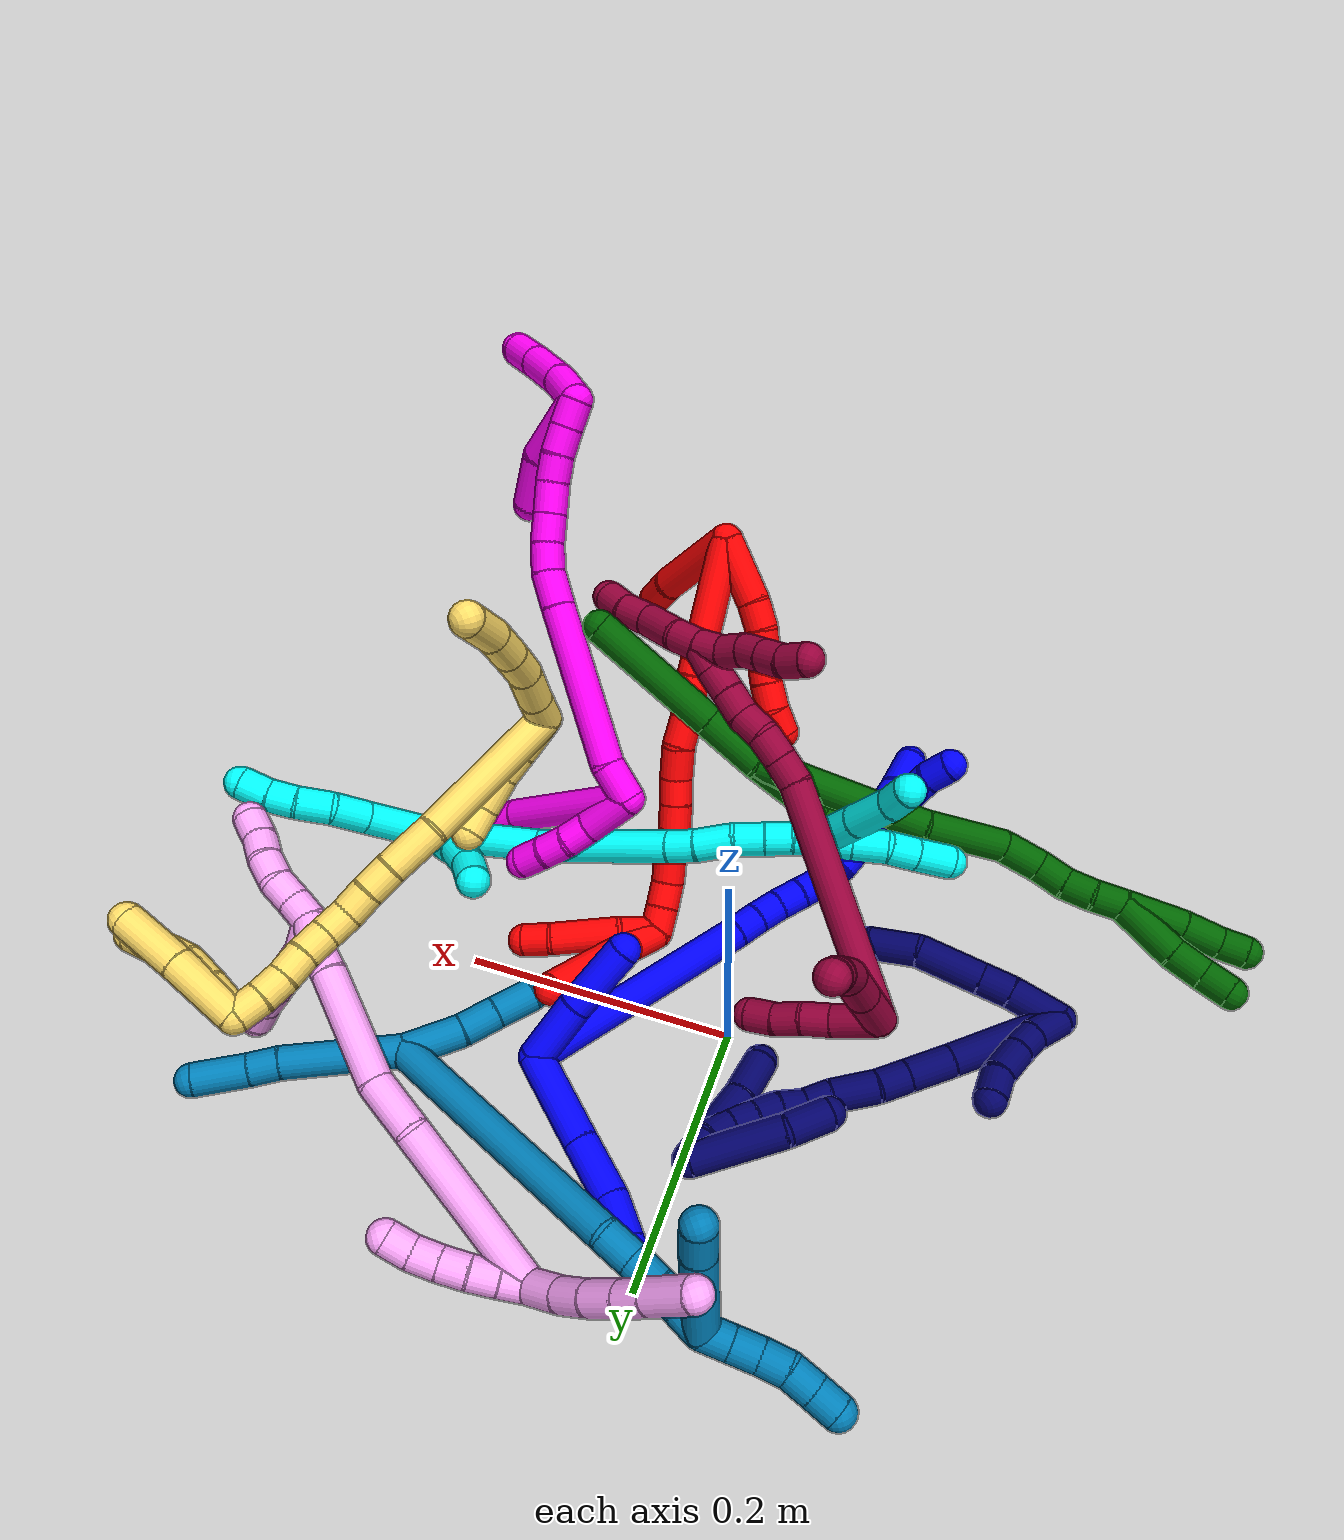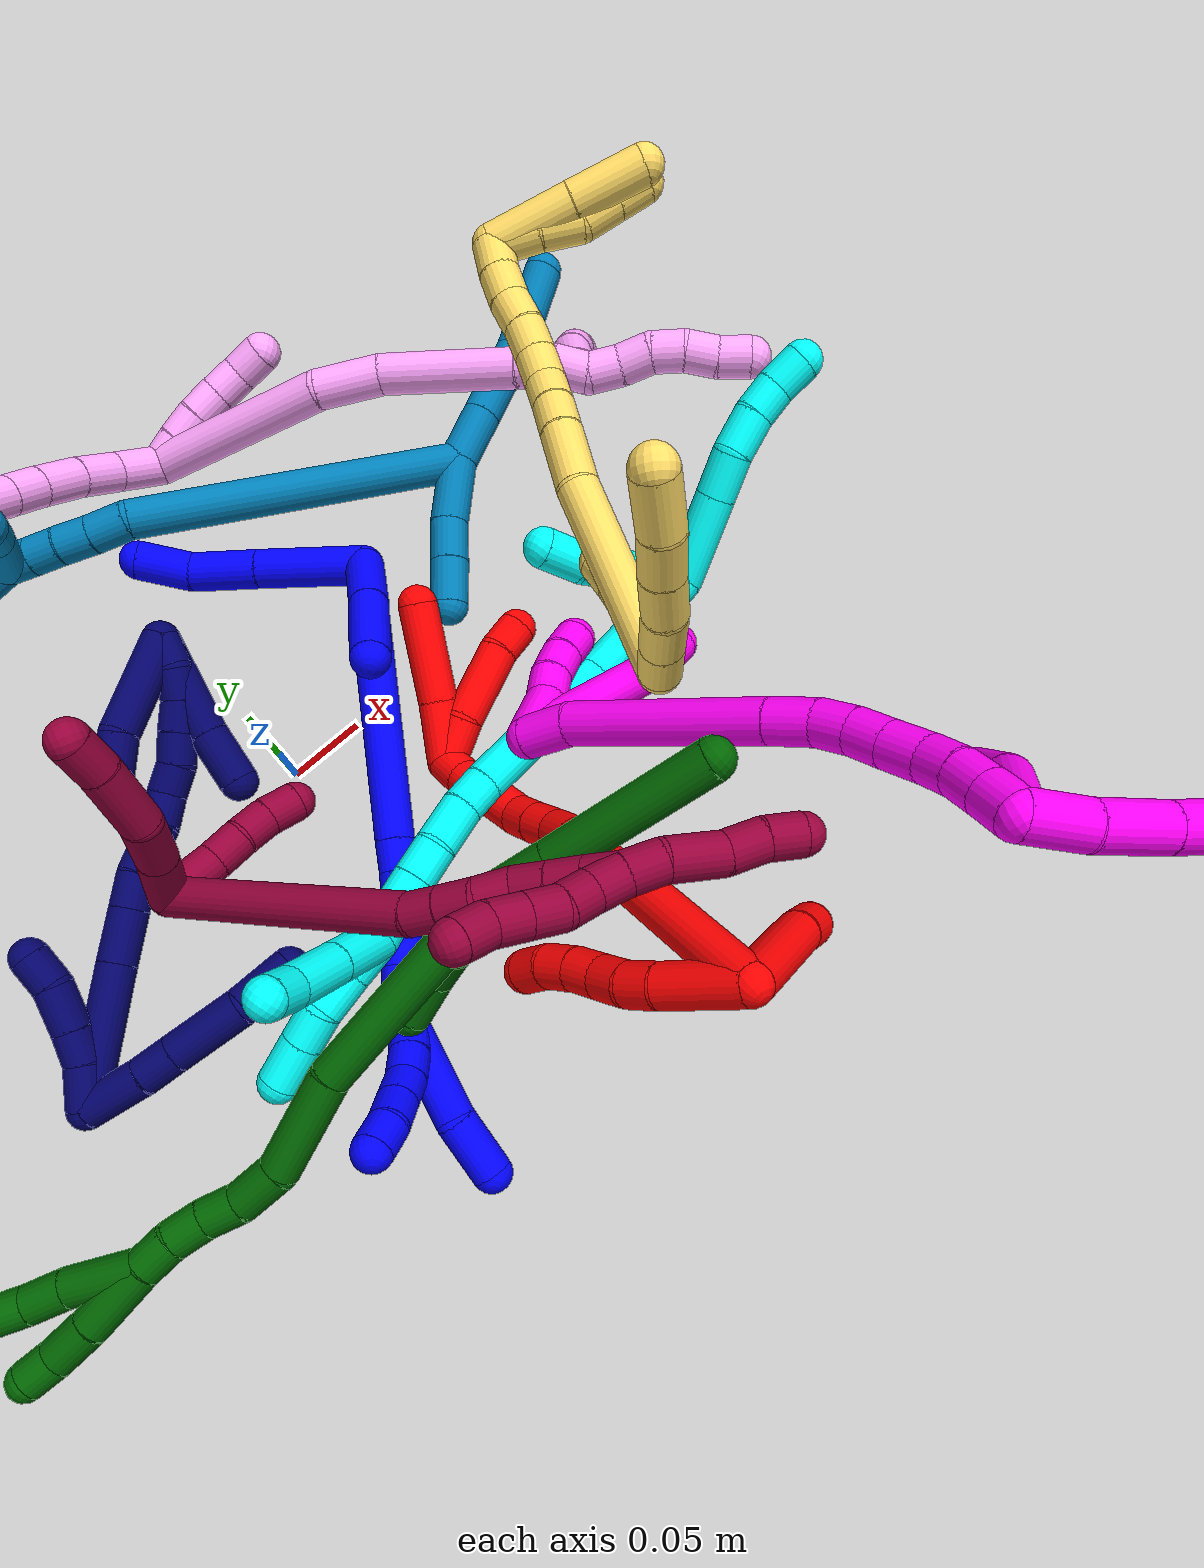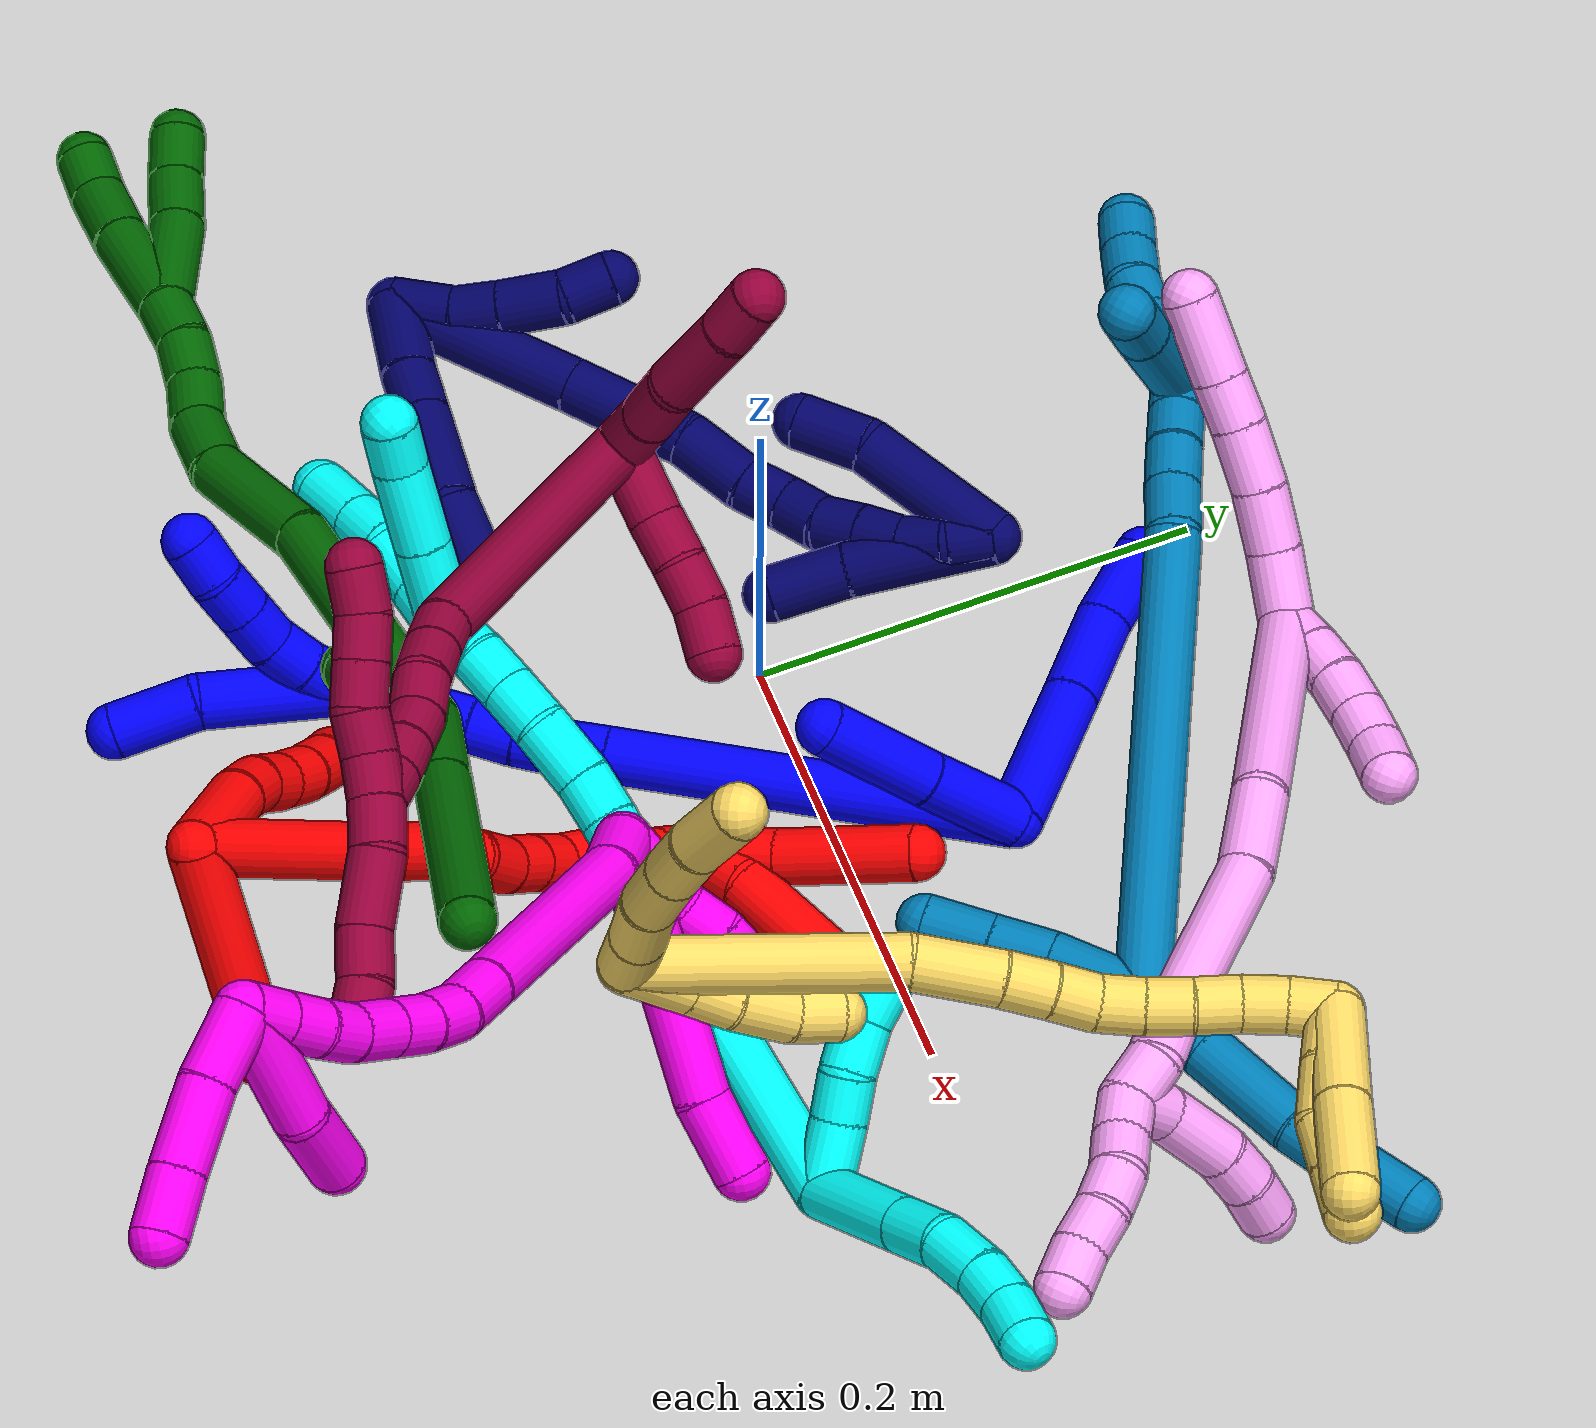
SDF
<sdf version="1.7">
 <world name="default">
  <plugin name="TubeGeneratorPlugin" filename="libtube_generator_plugin.so"/>
  <model name="photoneo_s_sensor">
   <static>1</static>
   <pose>0 0 2 1.57079 1.57079 3.14159</pose>
   <link name="link">
    <inertial><mass>0.1</mass></inertial>
    <sensor name="sensor" type="depth">
     <update_rate>30</update_rate>
     <camera>
      <horizontal_fov>1.22</horizontal_fov>
      <image><width>1920</width><height>1200</height><format>B8G8R8</format></image>
      <clip><near>0.1</near><far>4</far></clip>
      <depth_camera><output>points</output></depth_camera>
     </camera>
     <plugin name="camera_plugin" filename="libgazebo_ros_depth_camera.so">
      <baseline>0.2</baseline>
      <alwaysOn>1</alwaysOn>
      <updateRate>0.0</updateRate>
      <cameraName>camera_ir</cameraName>
      <imageTopicName>/camera/color/image_raw</imageTopicName>
      <cameraInfoTopicName>/camera/color/camera_info</cameraInfoTopicName>
      <depthImageTopicName>/camera/depth/image_raw</depthImageTopicName>
      <depthImageCameraInfoTopicName>/camera/depth/camera_info</depthImageCameraInfoTopicName>
      <pointCloudTopicName>/camera/depth/points</pointCloudTopicName>
      <frameName>fr_optical</frameName>
      <pointCloudCutoff>0.1</pointCloudCutoff>
      <pointCloudCutoffMax>2.0</pointCloudCutoffMax>
      <distortionK1>0</distortionK1>
      <distortionK2>0</distortionK2>
      <distortionK3>0</distortionK3>
      <distortionT1>0</distortionT1>
      <distortionT2>0</distortionT2>
      <CxPrime>0</CxPrime>
      <Cx>0</Cx>
      <Cy>0</Cy>
      <focalLength>0</focalLength>
      <hackBaseline>0</hackBaseline>
     </plugin>
    </sensor>
   </link>
  </model>
  <gravity>0 0 -9.8</gravity>
  <magnetic_field>6e-06 2.3e-05 -4.2e-05</magnetic_field>
  <atmosphere type="adiabatic"/>
  <physics name="default_physics" default="0" type="ode">
   <max_step_size>0.003</max_step_size>
   <real_time_factor>1</real_time_factor>
   <real_time_update_rate>1000</real_time_update_rate>
   <max_contacts>10000</max_contacts>
   <ode>
    <solver>
     <type>quick</type>
     <iters>100</iters>
     <sor>1.3</sor>
     <use_dynamic_moi_rescaling>0</use_dynamic_moi_rescaling>
    </solver>
    <constraints>
     <contact_max_correcting_vel>0</contact_max_correcting_vel>
     <contact_surface_layer>0.001</contact_surface_layer>
     <cfm>0</cfm>
     <erp>0.2</erp>
    </constraints>
   </ode>
  </physics>
  <scene><ambient>0.4 0.4 0.4 1</ambient><background>0.7 0.7 0.7 1</background><shadows>0</shadows></scene>
  <audio><device>default</device></audio>
  <spherical_coordinates>
   <surface_model>EARTH_WGS84</surface_model>
   <latitude_deg>0</latitude_deg>
   <longitude_deg>0</longitude_deg>
   <elevation>0</elevation>
   <heading_deg>0</heading_deg>
  </spherical_coordinates>
  <model name="bin">
   <static>1</static>
   <link name="bottom">
    <collision name="collision-bottom">
     <pose>0 0 -0.01 0 -0 0</pose>
     <geometry><box><size>0.8 0.6 0.02</size></box></geometry>
     <surface>
      <friction><ode><mu>100</mu><mu2>100</mu2></ode></friction>
      <contact><collide_bitmask>65535</collide_bitmask></contact>
     </surface>
    </collision>
   </link>
   <link name="west_wall">
    <collision name="collision-west_wall">
     <pose>-0.41 0 0.1 0 -0 0</pose>
     <geometry><box><size>0.02 0.6 0.2</size></box></geometry>
     <surface>
      <friction><ode><mu>100</mu><mu2>100</mu2></ode></friction>
      <contact><collide_bitmask>65535</collide_bitmask></contact>
     </surface>
    </collision>
   </link>
   <link name="east_wall">
    <collision name="collision-east_wall">
     <pose>0.41 0 0.1 0 -0 0</pose>
     <geometry><box><size>0.02 0.6 0.2</size></box></geometry>
     <surface>
      <friction><ode><mu>100</mu><mu2>100</mu2></ode></friction>
      <contact><collide_bitmask>65535</collide_bitmask></contact>
     </surface>
    </collision>
   </link>
   <link name="south_wall">
    <collision name="collision-south_wall">
     <pose>0 -0.31 0.1 0 -0 0</pose>
     <geometry><box><size>0.8 0.02 0.2</size></box></geometry>
     <surface>
      <friction><ode><mu>100</mu><mu2>100</mu2></ode></friction>
      <contact><collide_bitmask>65535</collide_bitmask></contact>
     </surface>
    </collision>
   </link>
   <link name="north_wall">
    <collision name="collision-north_wall">
     <pose>0 0.31 0.1 0 -0 0</pose>
     <geometry><box><size>0.8 0.02 0.2</size></box></geometry>
     <surface>
      <friction><ode><mu>100</mu><mu2>100</mu2></ode></friction>
      <contact><collide_bitmask>65535</collide_bitmask></contact>
     </surface>
    </collision>
   </link>
  </model>
  <model name="1">
   <static>0</static>
   <link name="1">
    <collision name="collision-cylinder-e_1_2_8">
     <pose>-0.017512 0.02956 -0.005868 -1.76675 -0.526383 0.634215</pose>
     <geometry><cylinder><radius>0.0125</radius><length>0.069711</length></cylinder></geometry>
     <surface>
      <friction><ode><mu>1.16</mu><mu2>1.16</mu2><slip1>0</slip1><slip2>0</slip2></ode></friction>
      <contact><ode><kp>1e+06</kp><kd>1</kd><max_vel>0</max_vel><min_depth>0.001</min_depth></ode></contact>
     </surface>
    </collision>
    <visual name="visual-cylinder-e_1_2_8">
     <pose>-0.017512 0.02956 -0.005868 -1.76675 -0.526383 0.634215</pose>
     <geometry><cylinder><radius>0.0125</radius><length>0.069711</length></cylinder></geometry>
     <material><ambient>0 0 1 1</ambient></material>
    </visual>
    <collision name="collision-cylinder-e_2_8_9">
     <pose>-0.04655 0.078062 -0.015384 -1.76111 -0.538609 0.64516</pose>
     <geometry><cylinder><radius>0.0125</radius><length>0.044943</length></cylinder></geometry>
     <surface>
      <friction><ode><mu>1.16</mu><mu2>1.16</mu2><slip1>0</slip1><slip2>0</slip2></ode></friction>
      <contact><ode><kp>1e+06</kp><kd>1</kd><max_vel>0</max_vel><min_depth>0.001</min_depth></ode></contact>
     </surface>
    </collision>
    <visual name="visual-cylinder-e_2_8_9">
     <pose>-0.04655 0.078062 -0.015384 -1.76111 -0.538609 0.64516</pose>
     <geometry><cylinder><radius>0.0125</radius><length>0.044943</length></cylinder></geometry>
     <material><ambient>0 0 1 1</ambient></material>
    </visual>
    <collision name="collision-cylinder-e_3_9_6">
     <pose>-0.062065 0.114009 -0.02173 -1.72806 -0.227647 0.266167</pose>
     <geometry><cylinder><radius>0.0125</radius><length>0.035346</length></cylinder></geometry>
     <surface>
      <friction><ode><mu>1.16</mu><mu2>1.16</mu2><slip1>0</slip1><slip2>0</slip2></ode></friction>
      <contact><ode><kp>1e+06</kp><kd>1</kd><max_vel>0</max_vel><min_depth>0.001</min_depth></ode></contact>
     </surface>
    </collision>
    <visual name="visual-cylinder-e_3_9_6">
     <pose>-0.062065 0.114009 -0.02173 -1.72806 -0.227647 0.266167</pose>
     <geometry><cylinder><radius>0.0125</radius><length>0.035346</length></cylinder></geometry>
     <material><ambient>0 0 1 1</ambient></material>
    </visual>
    <collision name="collision-cylinder-e_1_2_10">
     <pose>0.001124 -0.001834 0.023515 0.077856 0.047612 0.001855</pose>
     <geometry><cylinder><radius>0.0125</radius><length>0.047226</length></cylinder></geometry>
     <surface>
      <friction><ode><mu>1.16</mu><mu2>1.16</mu2><slip1>0</slip1><slip2>0</slip2></ode></friction>
      <contact><ode><kp>1e+06</kp><kd>1</kd><max_vel>0</max_vel><min_depth>0.001</min_depth></ode></contact>
     </surface>
    </collision>
    <visual name="visual-cylinder-e_1_2_10">
     <pose>0.001124 -0.001834 0.023515 0.077856 0.047612 0.001855</pose>
     <geometry><cylinder><radius>0.0125</radius><length>0.047226</length></cylinder></geometry>
     <material><ambient>0 0 1 1</ambient></material>
    </visual>
    <collision name="collision-cylinder-e_2_10_5">
     <pose>0.002043 -0.004999 0.073382 0.050445 -0.007772 -0.000196</pose>
     <geometry><cylinder><radius>0.0125</radius><length>0.052774</length></cylinder></geometry>
     <surface>
      <friction><ode><mu>1.16</mu><mu2>1.16</mu2><slip1>0</slip1><slip2>0</slip2></ode></friction>
      <contact><ode><kp>1e+06</kp><kd>1</kd><max_vel>0</max_vel><min_depth>0.001</min_depth></ode></contact>
     </surface>
    </collision>
    <visual name="visual-cylinder-e_2_10_5">
     <pose>0.002043 -0.004999 0.073382 0.050445 -0.007772 -0.000196</pose>
     <geometry><cylinder><radius>0.0125</radius><length>0.052774</length></cylinder></geometry>
     <material><ambient>0 0 1 1</ambient></material>
    </visual>
    <collision name="collision-cylinder-e_1_2_11">
     <pose>-0.048352 -0.028734 0.069934 0.38984 -0.568972 -0.115334</pose>
     <geometry><cylinder><radius>0.0125</radius><length>0.179492</length></cylinder></geometry>
     <surface>
      <friction><ode><mu>1.16</mu><mu2>1.16</mu2><slip1>0</slip1><slip2>0</slip2></ode></friction>
      <contact><ode><kp>1e+06</kp><kd>1</kd><max_vel>0</max_vel><min_depth>0.001</min_depth></ode></contact>
     </surface>
    </collision>
    <visual name="visual-cylinder-e_1_2_11">
     <pose>-0.048352 -0.028734 0.069934 0.38984 -0.568972 -0.115334</pose>
     <geometry><cylinder><radius>0.0125</radius><length>0.179492</length></cylinder></geometry>
     <material><ambient>0 0 1 1</ambient></material>
    </visual>
    <collision name="collision-cylinder-e_2_11_12">
     <pose>-0.101831 -0.06085 0.148062 0.391525 -0.524341 -0.106327</pose>
     <geometry><cylinder><radius>0.0125</radius><length>0.020481</length></cylinder></geometry>
     <surface>
      <friction><ode><mu>1.16</mu><mu2>1.16</mu2><slip1>0</slip1><slip2>0</slip2></ode></friction>
      <contact><ode><kp>1e+06</kp><kd>1</kd><max_vel>0</max_vel><min_depth>0.001</min_depth></ode></contact>
     </surface>
    </collision>
    <visual name="visual-cylinder-e_2_11_12">
     <pose>-0.101831 -0.06085 0.148062 0.391525 -0.524341 -0.106327</pose>
     <geometry><cylinder><radius>0.0125</radius><length>0.020481</length></cylinder></geometry>
     <material><ambient>0 0 1 1</ambient></material>
    </visual>
    <collision name="collision-cylinder-e_3_12_13">
     <pose>-0.112057 -0.067025 0.164397 0.330458 -0.534852 -0.091311</pose>
     <geometry><cylinder><radius>0.0125</radius><length>0.020006</length></cylinder></geometry>
     <surface>
      <friction><ode><mu>1.16</mu><mu2>1.16</mu2><slip1>0</slip1><slip2>0</slip2></ode></friction>
      <contact><ode><kp>1e+06</kp><kd>1</kd><max_vel>0</max_vel><min_depth>0.001</min_depth></ode></contact>
     </surface>
    </collision>
    <visual name="visual-cylinder-e_3_12_13">
     <pose>-0.112057 -0.067025 0.164397 0.330458 -0.534852 -0.091311</pose>
     <geometry><cylinder><radius>0.0125</radius><length>0.020006</length></cylinder></geometry>
     <material><ambient>0 0 1 1</ambient></material>
    </visual>
    <collision name="collision-cylinder-e_4_13_14">
     <pose>-0.12246 -0.071788 0.180788 0.234354 -0.558852 -0.067528</pose>
     <geometry><cylinder><radius>0.0125</radius><length>0.020009</length></cylinder></geometry>
     <surface>
      <friction><ode><mu>1.16</mu><mu2>1.16</mu2><slip1>0</slip1><slip2>0</slip2></ode></friction>
      <contact><ode><kp>1e+06</kp><kd>1</kd><max_vel>0</max_vel><min_depth>0.001</min_depth></ode></contact>
     </surface>
    </collision>
    <visual name="visual-cylinder-e_4_13_14">
     <pose>-0.12246 -0.071788 0.180788 0.234354 -0.558852 -0.067528</pose>
     <geometry><cylinder><radius>0.0125</radius><length>0.020009</length></cylinder></geometry>
     <material><ambient>0 0 1 1</ambient></material>
    </visual>
    <collision name="collision-cylinder-e_5_14_15">
     <pose>-0.133231 -0.075898 0.197134 0.258511 -0.578333 -0.077301</pose>
     <geometry><cylinder><radius>0.0125</radius><length>0.020002</length></cylinder></geometry>
     <surface>
      <friction><ode><mu>1.16</mu><mu2>1.16</mu2><slip1>0</slip1><slip2>0</slip2></ode></friction>
      <contact><ode><kp>1e+06</kp><kd>1</kd><max_vel>0</max_vel><min_depth>0.001</min_depth></ode></contact>
     </surface>
    </collision>
    <visual name="visual-cylinder-e_5_14_15">
     <pose>-0.133231 -0.075898 0.197134 0.258511 -0.578333 -0.077301</pose>
     <geometry><cylinder><radius>0.0125</radius><length>0.020002</length></cylinder></geometry>
     <material><ambient>0 0 1 1</ambient></material>
    </visual>
    <collision name="collision-cylinder-e_6_15_16">
     <pose>-0.14185 -0.079427 0.214624 0.146728 -0.320477 -0.023756</pose>
     <geometry><cylinder><radius>0.0125</radius><length>0.02001</length></cylinder></geometry>
     <surface>
      <friction><ode><mu>1.16</mu><mu2>1.16</mu2><slip1>0</slip1><slip2>0</slip2></ode></friction>
      <contact><ode><kp>1e+06</kp><kd>1</kd><max_vel>0</max_vel><min_depth>0.001</min_depth></ode></contact>
     </surface>
    </collision>
    <visual name="visual-cylinder-e_6_15_16">
     <pose>-0.14185 -0.079427 0.214624 0.146728 -0.320477 -0.023756</pose>
     <geometry><cylinder><radius>0.0125</radius><length>0.02001</length></cylinder></geometry>
     <material><ambient>0 0 1 1</ambient></material>
    </visual>
    <collision name="collision-cylinder-e_7_16_1">
     <pose>-0.146381 -0.083734 0.233482 0.299056 -0.138364 -0.020877</pose>
     <geometry><cylinder><radius>0.0125</radius><length>0.020001</length></cylinder></geometry>
     <surface>
      <friction><ode><mu>1.16</mu><mu2>1.16</mu2><slip1>0</slip1><slip2>0</slip2></ode></friction>
      <contact><ode><kp>1e+06</kp><kd>1</kd><max_vel>0</max_vel><min_depth>0.001</min_depth></ode></contact>
     </surface>
    </collision>
    <visual name="visual-cylinder-e_7_16_1">
     <pose>-0.146381 -0.083734 0.233482 0.299056 -0.138364 -0.020877</pose>
     <geometry><cylinder><radius>0.0125</radius><length>0.020001</length></cylinder></geometry>
     <material><ambient>0 0 1 1</ambient></material>
    </visual>
    <collision name="collision-cylinder-e_1_1_17">
     <pose>-0.155174 -0.104034 0.26753 0.61549 -0.241461 -0.077083</pose>
     <geometry><cylinder><radius>0.0125</radius><length>0.062013</length></cylinder></geometry>
     <surface>
      <friction><ode><mu>1.16</mu><mu2>1.16</mu2><slip1>0</slip1><slip2>0</slip2></ode></friction>
      <contact><ode><kp>1e+06</kp><kd>1</kd><max_vel>0</max_vel><min_depth>0.001</min_depth></ode></contact>
     </surface>
    </collision>
    <visual name="visual-cylinder-e_1_1_17">
     <pose>-0.155174 -0.104034 0.26753 0.61549 -0.241461 -0.077083</pose>
     <geometry><cylinder><radius>0.0125</radius><length>0.062013</length></cylinder></geometry>
     <material><ambient>0 0 1 1</ambient></material>
    </visual>
    <collision name="collision-cylinder-e_2_17_4">
     <pose>-0.16929 -0.135432 0.303039 0.908562 -0.360607 -0.177567</pose>
     <geometry><cylinder><radius>0.0125</radius><length>0.037987</length></cylinder></geometry>
     <surface>
      <friction><ode><mu>1.16</mu><mu2>1.16</mu2><slip1>0</slip1><slip2>0</slip2></ode></friction>
      <contact><ode><kp>1e+06</kp><kd>1</kd><max_vel>0</max_vel><min_depth>0.001</min_depth></ode></contact>
     </surface>
    </collision>
    <visual name="visual-cylinder-e_2_17_4">
     <pose>-0.16929 -0.135432 0.303039 0.908562 -0.360607 -0.177567</pose>
     <geometry><cylinder><radius>0.0125</radius><length>0.037987</length></cylinder></geometry>
     <material><ambient>0 0 1 1</ambient></material>
    </visual>
    <collision name="collision-cylinder-e_1_1_18">
     <pose>-0.147266 -0.086525 0.252935 -0.01274 0.049366 -0.000315</pose>
     <geometry><cylinder><radius>0.0125</radius><length>0.02</length></cylinder></geometry>
     <surface>
      <friction><ode><mu>1.16</mu><mu2>1.16</mu2><slip1>0</slip1><slip2>0</slip2></ode></friction>
      <contact><ode><kp>1e+06</kp><kd>1</kd><max_vel>0</max_vel><min_depth>0.001</min_depth></ode></contact>
     </surface>
    </collision>
    <visual name="visual-cylinder-e_1_1_18">
     <pose>-0.147266 -0.086525 0.252935 -0.01274 0.049366 -0.000315</pose>
     <geometry><cylinder><radius>0.0125</radius><length>0.02</length></cylinder></geometry>
     <material><ambient>0 0 1 1</ambient></material>
    </visual>
    <collision name="collision-cylinder-e_2_18_19">
     <pose>-0.146605 -0.085308 0.272861 -0.109191 0.01681 -0.000919</pose>
     <geometry><cylinder><radius>0.0125</radius><length>0.02</length></cylinder></geometry>
     <surface>
      <friction><ode><mu>1.16</mu><mu2>1.16</mu2><slip1>0</slip1><slip2>0</slip2></ode></friction>
      <contact><ode><kp>1e+06</kp><kd>1</kd><max_vel>0</max_vel><min_depth>0.001</min_depth></ode></contact>
     </surface>
    </collision>
    <visual name="visual-cylinder-e_2_18_19">
     <pose>-0.146605 -0.085308 0.272861 -0.109191 0.01681 -0.000919</pose>
     <geometry><cylinder><radius>0.0125</radius><length>0.02</length></cylinder></geometry>
     <material><ambient>0 0 1 1</ambient></material>
    </visual>
    <collision name="collision-cylinder-e_3_19_20">
     <pose>-0.144994 -0.081191 0.292221 -0.310921 0.144737 -0.022723</pose>
     <geometry><cylinder><radius>0.0125</radius><length>0.02</length></cylinder></geometry>
     <surface>
      <friction><ode><mu>1.16</mu><mu2>1.16</mu2><slip1>0</slip1><slip2>0</slip2></ode></friction>
      <contact><ode><kp>1e+06</kp><kd>1</kd><max_vel>0</max_vel><min_depth>0.001</min_depth></ode></contact>
     </surface>
    </collision>
    <visual name="visual-cylinder-e_3_19_20">
     <pose>-0.144994 -0.081191 0.292221 -0.310921 0.144737 -0.022723</pose>
     <geometry><cylinder><radius>0.0125</radius><length>0.02</length></cylinder></geometry>
     <material><ambient>0 0 1 1</ambient></material>
    </visual>
    <collision name="collision-cylinder-e_4_20_21">
     <pose>-0.142065 -0.075203 0.311077 -0.304064 0.149265 -0.022911</pose>
     <geometry><cylinder><radius>0.0125</radius><length>0.02</length></cylinder></geometry>
     <surface>
      <friction><ode><mu>1.16</mu><mu2>1.16</mu2><slip1>0</slip1><slip2>0</slip2></ode></friction>
      <contact><ode><kp>1e+06</kp><kd>1</kd><max_vel>0</max_vel><min_depth>0.001</min_depth></ode></contact>
     </surface>
    </collision>
    <visual name="visual-cylinder-e_4_20_21">
     <pose>-0.142065 -0.075203 0.311077 -0.304064 0.149265 -0.022911</pose>
     <geometry><cylinder><radius>0.0125</radius><length>0.02</length></cylinder></geometry>
     <material><ambient>0 0 1 1</ambient></material>
    </visual>
    <collision name="collision-cylinder-e_5_21_3">
     <pose>-0.141033 -0.068044 0.329577 -0.433665 -0.04552 0.01003</pose>
     <geometry><cylinder><radius>0.0125</radius><length>0.02</length></cylinder></geometry>
     <surface>
      <friction><ode><mu>1.16</mu><mu2>1.16</mu2><slip1>0</slip1><slip2>0</slip2></ode></friction>
      <contact><ode><kp>1e+06</kp><kd>1</kd><max_vel>0</max_vel><min_depth>0.001</min_depth></ode></contact>
     </surface>
    </collision>
    <visual name="visual-cylinder-e_5_21_3">
     <pose>-0.141033 -0.068044 0.329577 -0.433665 -0.04552 0.01003</pose>
     <geometry><cylinder><radius>0.0125</radius><length>0.02</length></cylinder></geometry>
     <material><ambient>0 0 1 1</ambient></material>
    </visual>
    <collision name="collision-sphere-3">
     <pose>-0.141488 -0.063847 0.338642 0 -0 0</pose>
     <geometry><sphere><radius>0.0125</radius></sphere></geometry>
     <surface>
      <friction><ode><mu>1.16</mu><mu2>1.16</mu2><slip1>0</slip1><slip2>0</slip2></ode></friction>
      <contact><ode><kp>1e+06</kp><kd>1</kd><max_vel>0</max_vel><min_depth>0.001</min_depth></ode></contact>
     </surface>
    </collision>
    <visual name="visual-sphere-3">
     <pose>-0.141488 -0.063847 0.338642 0 -0 0</pose>
     <geometry><sphere><radius>0.0125</radius></sphere></geometry>
     <material><ambient>0 0 1 1</ambient></material>
    </visual>
    <collision name="collision-sphere-21">
     <pose>-0.140578 -0.072242 0.320512 0 -0 0</pose>
     <geometry><sphere><radius>0.0125</radius></sphere></geometry>
     <surface>
      <friction><ode><mu>1.16</mu><mu2>1.16</mu2><slip1>0</slip1><slip2>0</slip2></ode></friction>
      <contact><ode><kp>1e+06</kp><kd>1</kd><max_vel>0</max_vel><min_depth>0.001</min_depth></ode></contact>
     </surface>
    </collision>
    <visual name="visual-sphere-21">
     <pose>-0.140578 -0.072242 0.320512 0 -0 0</pose>
     <geometry><sphere><radius>0.0125</radius></sphere></geometry>
     <material><ambient>0 0 1 1</ambient></material>
    </visual>
    <collision name="collision-sphere-20">
     <pose>-0.143552 -0.078164 0.301642 0 -0 0</pose>
     <geometry><sphere><radius>0.0125</radius></sphere></geometry>
     <surface>
      <friction><ode><mu>1.16</mu><mu2>1.16</mu2><slip1>0</slip1><slip2>0</slip2></ode></friction>
      <contact><ode><kp>1e+06</kp><kd>1</kd><max_vel>0</max_vel><min_depth>0.001</min_depth></ode></contact>
     </surface>
    </collision>
    <visual name="visual-sphere-20">
     <pose>-0.143552 -0.078164 0.301642 0 -0 0</pose>
     <geometry><sphere><radius>0.0125</radius></sphere></geometry>
     <material><ambient>0 0 1 1</ambient></material>
    </visual>
    <collision name="collision-sphere-19">
     <pose>-0.146437 -0.084218 0.2828 0 -0 0</pose>
     <geometry><sphere><radius>0.0125</radius></sphere></geometry>
     <surface>
      <friction><ode><mu>1.16</mu><mu2>1.16</mu2><slip1>0</slip1><slip2>0</slip2></ode></friction>
      <contact><ode><kp>1e+06</kp><kd>1</kd><max_vel>0</max_vel><min_depth>0.001</min_depth></ode></contact>
     </surface>
    </collision>
    <visual name="visual-sphere-19">
     <pose>-0.146437 -0.084218 0.2828 0 -0 0</pose>
     <geometry><sphere><radius>0.0125</radius></sphere></geometry>
     <material><ambient>0 0 1 1</ambient></material>
    </visual>
    <collision name="collision-sphere-5">
     <pose>0.001837 -0.00633 0.099735 0 -0 0</pose>
     <geometry><sphere><radius>0.0125</radius></sphere></geometry>
     <surface>
      <friction><ode><mu>1.16</mu><mu2>1.16</mu2><slip1>0</slip1><slip2>0</slip2></ode></friction>
      <contact><ode><kp>1e+06</kp><kd>1</kd><max_vel>0</max_vel><min_depth>0.001</min_depth></ode></contact>
     </surface>
    </collision>
    <visual name="visual-sphere-5">
     <pose>0.001837 -0.00633 0.099735 0 -0 0</pose>
     <geometry><sphere><radius>0.0125</radius></sphere></geometry>
     <material><ambient>0 0 1 1</ambient></material>
    </visual>
    <collision name="collision-sphere-10">
     <pose>0.002248 -0.003669 0.047029 0 -0 0</pose>
     <geometry><sphere><radius>0.0125</radius></sphere></geometry>
     <surface>
      <friction><ode><mu>1.16</mu><mu2>1.16</mu2><slip1>0</slip1><slip2>0</slip2></ode></friction>
      <contact><ode><kp>1e+06</kp><kd>1</kd><max_vel>0</max_vel><min_depth>0.001</min_depth></ode></contact>
     </surface>
    </collision>
    <visual name="visual-sphere-10">
     <pose>0.002248 -0.003669 0.047029 0 -0 0</pose>
     <geometry><sphere><radius>0.0125</radius></sphere></geometry>
     <material><ambient>0 0 1 1</ambient></material>
    </visual>
    <collision name="collision-sphere-6">
     <pose>-0.066054 0.131013 -0.024426 0 -0 0</pose>
     <geometry><sphere><radius>0.0125</radius></sphere></geometry>
     <surface>
      <friction><ode><mu>1.16</mu><mu2>1.16</mu2><slip1>0</slip1><slip2>0</slip2></ode></friction>
      <contact><ode><kp>1e+06</kp><kd>1</kd><max_vel>0</max_vel><min_depth>0.001</min_depth></ode></contact>
     </surface>
    </collision>
    <visual name="visual-sphere-6">
     <pose>-0.066054 0.131013 -0.024426 0 -0 0</pose>
     <geometry><sphere><radius>0.0125</radius></sphere></geometry>
     <material><ambient>0 0 1 1</ambient></material>
    </visual>
    <collision name="collision-sphere-9">
     <pose>-0.058077 0.097004 -0.019033 0 -0 0</pose>
     <geometry><sphere><radius>0.0125</radius></sphere></geometry>
     <surface>
      <friction><ode><mu>1.16</mu><mu2>1.16</mu2><slip1>0</slip1><slip2>0</slip2></ode></friction>
      <contact><ode><kp>1e+06</kp><kd>1</kd><max_vel>0</max_vel><min_depth>0.001</min_depth></ode></contact>
     </surface>
    </collision>
    <visual name="visual-sphere-9">
     <pose>-0.058077 0.097004 -0.019033 0 -0 0</pose>
     <geometry><sphere><radius>0.0125</radius></sphere></geometry>
     <material><ambient>0 0 1 1</ambient></material>
    </visual>
    <collision name="collision-sphere-2">
     <geometry><sphere><radius>0.0125</radius></sphere></geometry>
     <surface>
      <friction><ode><mu>1.16</mu><mu2>1.16</mu2><slip1>0</slip1><slip2>0</slip2></ode></friction>
      <contact><ode><kp>1e+06</kp><kd>1</kd><max_vel>0</max_vel><min_depth>0.001</min_depth></ode></contact>
     </surface>
    </collision>
    <visual name="visual-sphere-2">
     <geometry><sphere><radius>0.0125</radius></sphere></geometry>
     <material><ambient>0 0 1 1</ambient></material>
    </visual>
    <collision name="collision-sphere-8">
     <pose>-0.035023 0.05912 -0.011735 0 -0 0</pose>
     <geometry><sphere><radius>0.0125</radius></sphere></geometry>
     <surface>
      <friction><ode><mu>1.16</mu><mu2>1.16</mu2><slip1>0</slip1><slip2>0</slip2></ode></friction>
      <contact><ode><kp>1e+06</kp><kd>1</kd><max_vel>0</max_vel><min_depth>0.001</min_depth></ode></contact>
     </surface>
    </collision>
    <visual name="visual-sphere-8">
     <pose>-0.035023 0.05912 -0.011735 0 -0 0</pose>
     <geometry><sphere><radius>0.0125</radius></sphere></geometry>
     <material><ambient>0 0 1 1</ambient></material>
    </visual>
    <collision name="collision-sphere-11">
     <pose>-0.096704 -0.057468 0.139869 0 -0 0</pose>
     <geometry><sphere><radius>0.0125</radius></sphere></geometry>
     <surface>
      <friction><ode><mu>1.16</mu><mu2>1.16</mu2><slip1>0</slip1><slip2>0</slip2></ode></friction>
      <contact><ode><kp>1e+06</kp><kd>1</kd><max_vel>0</max_vel><min_depth>0.001</min_depth></ode></contact>
     </surface>
    </collision>
    <visual name="visual-sphere-11">
     <pose>-0.096704 -0.057468 0.139869 0 -0 0</pose>
     <geometry><sphere><radius>0.0125</radius></sphere></geometry>
     <material><ambient>0 0 1 1</ambient></material>
    </visual>
    <collision name="collision-sphere-12">
     <pose>-0.106958 -0.064233 0.156256 0 -0 0</pose>
     <geometry><sphere><radius>0.0125</radius></sphere></geometry>
     <surface>
      <friction><ode><mu>1.16</mu><mu2>1.16</mu2><slip1>0</slip1><slip2>0</slip2></ode></friction>
      <contact><ode><kp>1e+06</kp><kd>1</kd><max_vel>0</max_vel><min_depth>0.001</min_depth></ode></contact>
     </surface>
    </collision>
    <visual name="visual-sphere-12">
     <pose>-0.106958 -0.064233 0.156256 0 -0 0</pose>
     <geometry><sphere><radius>0.0125</radius></sphere></geometry>
     <material><ambient>0 0 1 1</ambient></material>
    </visual>
    <collision name="collision-sphere-13">
     <pose>-0.117155 -0.069818 0.172537 0 -0 0</pose>
     <geometry><sphere><radius>0.0125</radius></sphere></geometry>
     <surface>
      <friction><ode><mu>1.16</mu><mu2>1.16</mu2><slip1>0</slip1><slip2>0</slip2></ode></friction>
      <contact><ode><kp>1e+06</kp><kd>1</kd><max_vel>0</max_vel><min_depth>0.001</min_depth></ode></contact>
     </surface>
    </collision>
    <visual name="visual-sphere-13">
     <pose>-0.117155 -0.069818 0.172537 0 -0 0</pose>
     <geometry><sphere><radius>0.0125</radius></sphere></geometry>
     <material><ambient>0 0 1 1</ambient></material>
    </visual>
    <collision name="collision-sphere-14">
     <pose>-0.127764 -0.073757 0.189038 0 -0 0</pose>
     <geometry><sphere><radius>0.0125</radius></sphere></geometry>
     <surface>
      <friction><ode><mu>1.16</mu><mu2>1.16</mu2><slip1>0</slip1><slip2>0</slip2></ode></friction>
      <contact><ode><kp>1e+06</kp><kd>1</kd><max_vel>0</max_vel><min_depth>0.001</min_depth></ode></contact>
     </surface>
    </collision>
    <visual name="visual-sphere-14">
     <pose>-0.127764 -0.073757 0.189038 0 -0 0</pose>
     <geometry><sphere><radius>0.0125</radius></sphere></geometry>
     <material><ambient>0 0 1 1</ambient></material>
    </visual>
    <collision name="collision-sphere-15">
     <pose>-0.138698 -0.078039 0.205231 0 -0 0</pose>
     <geometry><sphere><radius>0.0125</radius></sphere></geometry>
     <surface>
      <friction><ode><mu>1.16</mu><mu2>1.16</mu2><slip1>0</slip1><slip2>0</slip2></ode></friction>
      <contact><ode><kp>1e+06</kp><kd>1</kd><max_vel>0</max_vel><min_depth>0.001</min_depth></ode></contact>
     </surface>
    </collision>
    <visual name="visual-sphere-15">
     <pose>-0.138698 -0.078039 0.205231 0 -0 0</pose>
     <geometry><sphere><radius>0.0125</radius></sphere></geometry>
     <material><ambient>0 0 1 1</ambient></material>
    </visual>
    <collision name="collision-sphere-16">
     <pose>-0.145001 -0.080816 0.224017 0 -0 0</pose>
     <geometry><sphere><radius>0.0125</radius></sphere></geometry>
     <surface>
      <friction><ode><mu>1.16</mu><mu2>1.16</mu2><slip1>0</slip1><slip2>0</slip2></ode></friction>
      <contact><ode><kp>1e+06</kp><kd>1</kd><max_vel>0</max_vel><min_depth>0.001</min_depth></ode></contact>
     </surface>
    </collision>
    <visual name="visual-sphere-16">
     <pose>-0.145001 -0.080816 0.224017 0 -0 0</pose>
     <geometry><sphere><radius>0.0125</radius></sphere></geometry>
     <material><ambient>0 0 1 1</ambient></material>
    </visual>
    <collision name="collision-sphere-1">
     <pose>-0.14776 -0.086652 0.242948 0 -0 0</pose>
     <geometry><sphere><radius>0.0125</radius></sphere></geometry>
     <surface>
      <friction><ode><mu>1.16</mu><mu2>1.16</mu2><slip1>0</slip1><slip2>0</slip2></ode></friction>
      <contact><ode><kp>1e+06</kp><kd>1</kd><max_vel>0</max_vel><min_depth>0.001</min_depth></ode></contact>
     </surface>
    </collision>
    <visual name="visual-sphere-1">
     <pose>-0.14776 -0.086652 0.242948 0 -0 0</pose>
     <geometry><sphere><radius>0.0125</radius></sphere></geometry>
     <material><ambient>0 0 1 1</ambient></material>
    </visual>
    <collision name="collision-sphere-18">
     <pose>-0.146773 -0.086397 0.262922 0 -0 0</pose>
     <geometry><sphere><radius>0.0125</radius></sphere></geometry>
     <surface>
      <friction><ode><mu>1.16</mu><mu2>1.16</mu2><slip1>0</slip1><slip2>0</slip2></ode></friction>
      <contact><ode><kp>1e+06</kp><kd>1</kd><max_vel>0</max_vel><min_depth>0.001</min_depth></ode></contact>
     </surface>
    </collision>
    <visual name="visual-sphere-18">
     <pose>-0.146773 -0.086397 0.262922 0 -0 0</pose>
     <geometry><sphere><radius>0.0125</radius></sphere></geometry>
     <material><ambient>0 0 1 1</ambient></material>
    </visual>
    <collision name="collision-sphere-17">
     <pose>-0.162588 -0.121417 0.292112 0 -0 0</pose>
     <geometry><sphere><radius>0.0125</radius></sphere></geometry>
     <surface>
      <friction><ode><mu>1.16</mu><mu2>1.16</mu2><slip1>0</slip1><slip2>0</slip2></ode></friction>
      <contact><ode><kp>1e+06</kp><kd>1</kd><max_vel>0</max_vel><min_depth>0.001</min_depth></ode></contact>
     </surface>
    </collision>
    <visual name="visual-sphere-17">
     <pose>-0.162588 -0.121417 0.292112 0 -0 0</pose>
     <geometry><sphere><radius>0.0125</radius></sphere></geometry>
     <material><ambient>0 0 1 1</ambient></material>
    </visual>
    <collision name="collision-sphere-4">
     <pose>-0.175992 -0.149448 0.313967 0 -0 0</pose>
     <geometry><sphere><radius>0.0125</radius></sphere></geometry>
     <surface>
      <friction><ode><mu>1.16</mu><mu2>1.16</mu2><slip1>0</slip1><slip2>0</slip2></ode></friction>
      <contact><ode><kp>1e+06</kp><kd>1</kd><max_vel>0</max_vel><min_depth>0.001</min_depth></ode></contact>
     </surface>
    </collision>
    <visual name="visual-sphere-4">
     <pose>-0.175992 -0.149448 0.313967 0 -0 0</pose>
     <geometry><sphere><radius>0.0125</radius></sphere></geometry>
     <material><ambient>0 0 1 1</ambient></material>
    </visual>
    <inertial>
     <pose>-0.079635 -0.032315 0.127718 0 -0 0</pose>
     <mass>0.75</mass>
     <inertia><ixx>0.000462</ixx><ixy>0</ixy><ixz>0</ixz><iyy>0.0005</iyy><iyz>0</iyz><izz>0.00047</izz></inertia>
    </inertial>
   </link>
   <pose>0.11952 0.070412 0.025995 0.604452 -0.80466 0.190619</pose>
  </model>
  <model name="2">
   <static>0</static>
   <link name="2">
    <collision name="collision-cylinder-e_1_2_8">
     <pose>0.008859 -0.016257 -0.016313 2.35792 0.367224 0.844754</pose>
     <geometry><cylinder><radius>0.0125</radius><length>0.04935</length></cylinder></geometry>
     <surface>
      <friction><ode><mu>1.16</mu><mu2>1.16</mu2><slip1>0</slip1><slip2>0</slip2></ode></friction>
      <contact><ode><kp>1e+06</kp><kd>1</kd><max_vel>0</max_vel><min_depth>0.001</min_depth></ode></contact>
     </surface>
    </collision>
    <visual name="visual-cylinder-e_1_2_8">
     <pose>0.008859 -0.016257 -0.016313 2.35792 0.367224 0.844754</pose>
     <geometry><cylinder><radius>0.0125</radius><length>0.04935</length></cylinder></geometry>
     <material><ambient>1 0 0 1</ambient></material>
    </visual>
    <collision name="collision-cylinder-e_2_8_9">
     <pose>0.022319 -0.037969 -0.039881 2.49682 0.469125 1.24192</pose>
     <geometry><cylinder><radius>0.0125</radius><length>0.020355</length></cylinder></geometry>
     <surface>
      <friction><ode><mu>1.16</mu><mu2>1.16</mu2><slip1>0</slip1><slip2>0</slip2></ode></friction>
      <contact><ode><kp>1e+06</kp><kd>1</kd><max_vel>0</max_vel><min_depth>0.001</min_depth></ode></contact>
     </surface>
    </collision>
    <visual name="visual-cylinder-e_2_8_9">
     <pose>0.022319 -0.037969 -0.039881 2.49682 0.469125 1.24192</pose>
     <geometry><cylinder><radius>0.0125</radius><length>0.020355</length></cylinder></geometry>
     <material><ambient>1 0 0 1</ambient></material>
    </visual>
    <collision name="collision-cylinder-e_3_9_10">
     <pose>0.032091 -0.046731 -0.055107 2.74838 0.539808 1.8936</pose>
     <geometry><cylinder><radius>0.0125</radius><length>0.020118</length></cylinder></geometry>
     <surface>
      <friction><ode><mu>1.16</mu><mu2>1.16</mu2><slip1>0</slip1><slip2>0</slip2></ode></friction>
      <contact><ode><kp>1e+06</kp><kd>1</kd><max_vel>0</max_vel><min_depth>0.001</min_depth></ode></contact>
     </surface>
    </collision>
    <visual name="visual-cylinder-e_3_9_10">
     <pose>0.032091 -0.046731 -0.055107 2.74838 0.539808 1.8936</pose>
     <geometry><cylinder><radius>0.0125</radius><length>0.020118</length></cylinder></geometry>
     <material><ambient>1 0 0 1</ambient></material>
    </visual>
    <collision name="collision-cylinder-e_4_10_11">
     <pose>0.041383 -0.053887 -0.071372 2.70706 0.423479 1.54422</pose>
     <geometry><cylinder><radius>0.0125</radius><length>0.020062</length></cylinder></geometry>
     <surface>
      <friction><ode><mu>1.16</mu><mu2>1.16</mu2><slip1>0</slip1><slip2>0</slip2></ode></friction>
      <contact><ode><kp>1e+06</kp><kd>1</kd><max_vel>0</max_vel><min_depth>0.001</min_depth></ode></contact>
     </surface>
    </collision>
    <visual name="visual-cylinder-e_4_10_11">
     <pose>0.041383 -0.053887 -0.071372 2.70706 0.423479 1.54422</pose>
     <geometry><cylinder><radius>0.0125</radius><length>0.020062</length></cylinder></geometry>
     <material><ambient>1 0 0 1</ambient></material>
    </visual>
    <collision name="collision-cylinder-e_5_11_12">
     <pose>0.049933 -0.062692 -0.087201 2.55986 0.456437 1.31972</pose>
     <geometry><cylinder><radius>0.0125</radius><length>0.020092</length></cylinder></geometry>
     <surface>
      <friction><ode><mu>1.16</mu><mu2>1.16</mu2><slip1>0</slip1><slip2>0</slip2></ode></friction>
      <contact><ode><kp>1e+06</kp><kd>1</kd><max_vel>0</max_vel><min_depth>0.001</min_depth></ode></contact>
     </surface>
    </collision>
    <visual name="visual-cylinder-e_5_11_12">
     <pose>0.049933 -0.062692 -0.087201 2.55986 0.456437 1.31972</pose>
     <geometry><cylinder><radius>0.0125</radius><length>0.020092</length></cylinder></geometry>
     <material><ambient>1 0 0 1</ambient></material>
    </visual>
    <collision name="collision-cylinder-e_6_12_6">
     <pose>0.060612 -0.072915 -0.100515 2.40247 0.674367 1.47117</pose>
     <geometry><cylinder><radius>0.0125</radius><length>0.020023</length></cylinder></geometry>
     <surface>
      <friction><ode><mu>1.16</mu><mu2>1.16</mu2><slip1>0</slip1><slip2>0</slip2></ode></friction>
      <contact><ode><kp>1e+06</kp><kd>1</kd><max_vel>0</max_vel><min_depth>0.001</min_depth></ode></contact>
     </surface>
    </collision>
    <visual name="visual-cylinder-e_6_12_6">
     <pose>0.060612 -0.072915 -0.100515 2.40247 0.674367 1.47117</pose>
     <geometry><cylinder><radius>0.0125</radius><length>0.020023</length></cylinder></geometry>
     <material><ambient>1 0 0 1</ambient></material>
    </visual>
    <collision name="collision-cylinder-e_1_2_13">
     <pose>0.024471 0.023539 -0.014065 -2.10939 0.728603 -1.18345</pose>
     <geometry><cylinder><radius>0.0125</radius><length>0.073505</length></cylinder></geometry>
     <surface>
      <friction><ode><mu>1.16</mu><mu2>1.16</mu2><slip1>0</slip1><slip2>0</slip2></ode></friction>
      <contact><ode><kp>1e+06</kp><kd>1</kd><max_vel>0</max_vel><min_depth>0.001</min_depth></ode></contact>
     </surface>
    </collision>
    <visual name="visual-cylinder-e_1_2_13">
     <pose>0.024471 0.023539 -0.014065 -2.10939 0.728603 -1.18345</pose>
     <geometry><cylinder><radius>0.0125</radius><length>0.073505</length></cylinder></geometry>
     <material><ambient>1 0 0 1</ambient></material>
    </visual>
    <collision name="collision-cylinder-e_2_13_5">
     <pose>0.059238 0.054165 -0.03252 -2.12535 0.890233 -1.41664</pose>
     <geometry><cylinder><radius>0.0125</radius><length>0.026495</length></cylinder></geometry>
     <surface>
      <friction><ode><mu>1.16</mu><mu2>1.16</mu2><slip1>0</slip1><slip2>0</slip2></ode></friction>
      <contact><ode><kp>1e+06</kp><kd>1</kd><max_vel>0</max_vel><min_depth>0.001</min_depth></ode></contact>
     </surface>
    </collision>
    <visual name="visual-cylinder-e_2_13_5">
     <pose>0.059238 0.054165 -0.03252 -2.12535 0.890233 -1.41664</pose>
     <geometry><cylinder><radius>0.0125</radius><length>0.026495</length></cylinder></geometry>
     <material><ambient>1 0 0 1</ambient></material>
    </visual>
    <collision name="collision-cylinder-e_1_2_14">
     <pose>0.01385 -0.004765 -0.049063 3.04478 0.273897 2.46555</pose>
     <geometry><cylinder><radius>0.0125</radius><length>0.102405</length></cylinder></geometry>
     <surface>
      <friction><ode><mu>1.16</mu><mu2>1.16</mu2><slip1>0</slip1><slip2>0</slip2></ode></friction>
      <contact><ode><kp>1e+06</kp><kd>1</kd><max_vel>0</max_vel><min_depth>0.001</min_depth></ode></contact>
     </surface>
    </collision>
    <visual name="visual-cylinder-e_1_2_14">
     <pose>0.01385 -0.004765 -0.049063 3.04478 0.273897 2.46555</pose>
     <geometry><cylinder><radius>0.0125</radius><length>0.102405</length></cylinder></geometry>
     <material><ambient>1 0 0 1</ambient></material>
    </visual>
    <collision name="collision-cylinder-e_2_14_15">
     <pose>0.032577 -0.011994 -0.112218 2.96844 0.32864 2.17717</pose>
     <geometry><cylinder><radius>0.0125</radius><length>0.03023</length></cylinder></geometry>
     <surface>
      <friction><ode><mu>1.16</mu><mu2>1.16</mu2><slip1>0</slip1><slip2>0</slip2></ode></friction>
      <contact><ode><kp>1e+06</kp><kd>1</kd><max_vel>0</max_vel><min_depth>0.001</min_depth></ode></contact>
     </surface>
    </collision>
    <visual name="visual-cylinder-e_2_14_15">
     <pose>0.032577 -0.011994 -0.112218 2.96844 0.32864 2.17717</pose>
     <geometry><cylinder><radius>0.0125</radius><length>0.03023</length></cylinder></geometry>
     <material><ambient>1 0 0 1</ambient></material>
    </visual>
    <collision name="collision-cylinder-e_3_15_16">
     <pose>0.041457 -0.01461 -0.136903 3.12726 0.361137 3.06314</pose>
     <geometry><cylinder><radius>0.0125</radius><length>0.022649</length></cylinder></geometry>
     <surface>
      <friction><ode><mu>1.16</mu><mu2>1.16</mu2><slip1>0</slip1><slip2>0</slip2></ode></friction>
      <contact><ode><kp>1e+06</kp><kd>1</kd><max_vel>0</max_vel><min_depth>0.001</min_depth></ode></contact>
     </surface>
    </collision>
    <visual name="visual-cylinder-e_3_15_16">
     <pose>0.041457 -0.01461 -0.136903 3.12726 0.361137 3.06314</pose>
     <geometry><cylinder><radius>0.0125</radius><length>0.022649</length></cylinder></geometry>
     <material><ambient>1 0 0 1</ambient></material>
    </visual>
    <collision name="collision-cylinder-e_4_16_17">
     <pose>0.052357 -0.01643 -0.157529 2.97686 0.596008 2.61647</pose>
     <geometry><cylinder><radius>0.0125</radius><length>0.024579</length></cylinder></geometry>
     <surface>
      <friction><ode><mu>1.16</mu><mu2>1.16</mu2><slip1>0</slip1><slip2>0</slip2></ode></friction>
      <contact><ode><kp>1e+06</kp><kd>1</kd><max_vel>0</max_vel><min_depth>0.001</min_depth></ode></contact>
     </surface>
    </collision>
    <visual name="visual-cylinder-e_4_16_17">
     <pose>0.052357 -0.01643 -0.157529 2.97686 0.596008 2.61647</pose>
     <geometry><cylinder><radius>0.0125</radius><length>0.024579</length></cylinder></geometry>
     <material><ambient>1 0 0 1</ambient></material>
    </visual>
    <collision name="collision-cylinder-e_5_17_18">
     <pose>0.06363 -0.020729 -0.176215 2.84639 0.450445 1.99029</pose>
     <geometry><cylinder><radius>0.0125</radius><length>0.020093</length></cylinder></geometry>
     <surface>
      <friction><ode><mu>1.16</mu><mu2>1.16</mu2><slip1>0</slip1><slip2>0</slip2></ode></friction>
      <contact><ode><kp>1e+06</kp><kd>1</kd><max_vel>0</max_vel><min_depth>0.001</min_depth></ode></contact>
     </surface>
    </collision>
    <visual name="visual-cylinder-e_5_17_18">
     <pose>0.06363 -0.020729 -0.176215 2.84639 0.450445 1.99029</pose>
     <geometry><cylinder><radius>0.0125</radius><length>0.020093</length></cylinder></geometry>
     <material><ambient>1 0 0 1</ambient></material>
    </visual>
    <collision name="collision-cylinder-e_6_18_19">
     <pose>0.072426 -0.025556 -0.193575 2.89463 0.457608 2.16227</pose>
     <geometry><cylinder><radius>0.0125</radius><length>0.020018</length></cylinder></geometry>
     <surface>
      <friction><ode><mu>1.16</mu><mu2>1.16</mu2><slip1>0</slip1><slip2>0</slip2></ode></friction>
      <contact><ode><kp>1e+06</kp><kd>1</kd><max_vel>0</max_vel><min_depth>0.001</min_depth></ode></contact>
     </surface>
    </collision>
    <visual name="visual-cylinder-e_6_18_19">
     <pose>0.072426 -0.025556 -0.193575 2.89463 0.457608 2.16227</pose>
     <geometry><cylinder><radius>0.0125</radius><length>0.020018</length></cylinder></geometry>
     <material><ambient>1 0 0 1</ambient></material>
    </visual>
    <collision name="collision-cylinder-e_7_19_20">
     <pose>0.078402 -0.029819 -0.211948 2.93078 0.15599 1.27246</pose>
     <geometry><cylinder><radius>0.0125</radius><length>0.020014</length></cylinder></geometry>
     <surface>
      <friction><ode><mu>1.16</mu><mu2>1.16</mu2><slip1>0</slip1><slip2>0</slip2></ode></friction>
      <contact><ode><kp>1e+06</kp><kd>1</kd><max_vel>0</max_vel><min_depth>0.001</min_depth></ode></contact>
     </surface>
    </collision>
    <visual name="visual-cylinder-e_7_19_20">
     <pose>0.078402 -0.029819 -0.211948 2.93078 0.15599 1.27246</pose>
     <geometry><cylinder><radius>0.0125</radius><length>0.020014</length></cylinder></geometry>
     <material><ambient>1 0 0 1</ambient></material>
    </visual>
    <collision name="collision-cylinder-e_8_20_21">
     <pose>0.084493 -0.033642 -0.230355 2.94359 0.470693 2.35617</pose>
     <geometry><cylinder><radius>0.0125</radius><length>0.020005</length></cylinder></geometry>
     <surface>
      <friction><ode><mu>1.16</mu><mu2>1.16</mu2><slip1>0</slip1><slip2>0</slip2></ode></friction>
      <contact><ode><kp>1e+06</kp><kd>1</kd><max_vel>0</max_vel><min_depth>0.001</min_depth></ode></contact>
     </surface>
    </collision>
    <visual name="visual-cylinder-e_8_20_21">
     <pose>0.084493 -0.033642 -0.230355 2.94359 0.470693 2.35617</pose>
     <geometry><cylinder><radius>0.0125</radius><length>0.020005</length></cylinder></geometry>
     <material><ambient>1 0 0 1</ambient></material>
    </visual>
    <collision name="collision-cylinder-e_9_21_22">
     <pose>0.091077 -0.036762 -0.248789 3.00149 0.206233 1.94992</pose>
     <geometry><cylinder><radius>0.0125</radius><length>0.020003</length></cylinder></geometry>
     <surface>
      <friction><ode><mu>1.16</mu><mu2>1.16</mu2><slip1>0</slip1><slip2>0</slip2></ode></friction>
      <contact><ode><kp>1e+06</kp><kd>1</kd><max_vel>0</max_vel><min_depth>0.001</min_depth></ode></contact>
     </surface>
    </collision>
    <visual name="visual-cylinder-e_9_21_22">
     <pose>0.091077 -0.036762 -0.248789 3.00149 0.206233 1.94992</pose>
     <geometry><cylinder><radius>0.0125</radius><length>0.020003</length></cylinder></geometry>
     <material><ambient>1 0 0 1</ambient></material>
    </visual>
    <collision name="collision-cylinder-e_10_22_1">
     <pose>0.094459 -0.039433 -0.26831 3.00971 0.133785 1.58515</pose>
     <geometry><cylinder><radius>0.0125</radius><length>0.020005</length></cylinder></geometry>
     <surface>
      <friction><ode><mu>1.16</mu><mu2>1.16</mu2><slip1>0</slip1><slip2>0</slip2></ode></friction>
      <contact><ode><kp>1e+06</kp><kd>1</kd><max_vel>0</max_vel><min_depth>0.001</min_depth></ode></contact>
     </surface>
    </collision>
    <visual name="visual-cylinder-e_10_22_1">
     <pose>0.094459 -0.039433 -0.26831 3.00971 0.133785 1.58515</pose>
     <geometry><cylinder><radius>0.0125</radius><length>0.020005</length></cylinder></geometry>
     <material><ambient>1 0 0 1</ambient></material>
    </visual>
    <collision name="collision-cylinder-e_1_1_23">
     <pose>0.085193 -0.032994 -0.291879 -2.62851 -0.591737 1.72036</pose>
     <geometry><cylinder><radius>0.0125</radius><length>0.038009</length></cylinder></geometry>
     <surface>
      <friction><ode><mu>1.16</mu><mu2>1.16</mu2><slip1>0</slip1><slip2>0</slip2></ode></friction>
      <contact><ode><kp>1e+06</kp><kd>1</kd><max_vel>0</max_vel><min_depth>0.001</min_depth></ode></contact>
     </surface>
    </collision>
    <visual name="visual-cylinder-e_1_1_23">
     <pose>0.085193 -0.032994 -0.291879 -2.62851 -0.591737 1.72036</pose>
     <geometry><cylinder><radius>0.0125</radius><length>0.038009</length></cylinder></geometry>
     <material><ambient>1 0 0 1</ambient></material>
    </visual>
    <collision name="collision-cylinder-e_2_23_4">
     <pose>0.055507 -0.014611 -0.327604 -2.69079 -0.663334 1.96678</pose>
     <geometry><cylinder><radius>0.0125</radius><length>0.061991</length></cylinder></geometry>
     <surface>
      <friction><ode><mu>1.16</mu><mu2>1.16</mu2><slip1>0</slip1><slip2>0</slip2></ode></friction>
      <contact><ode><kp>1e+06</kp><kd>1</kd><max_vel>0</max_vel><min_depth>0.001</min_depth></ode></contact>
     </surface>
    </collision>
    <visual name="visual-cylinder-e_2_23_4">
     <pose>0.055507 -0.014611 -0.327604 -2.69079 -0.663334 1.96678</pose>
     <geometry><cylinder><radius>0.0125</radius><length>0.061991</length></cylinder></geometry>
     <material><ambient>1 0 0 1</ambient></material>
    </visual>
    <collision name="collision-cylinder-e_1_1_24">
     <pose>0.089268 -0.029203 -0.284079 -2.04651 -0.466045 0.742402</pose>
     <geometry><cylinder><radius>0.0125</radius><length>0.029046</length></cylinder></geometry>
     <surface>
      <friction><ode><mu>1.16</mu><mu2>1.16</mu2><slip1>0</slip1><slip2>0</slip2></ode></friction>
      <contact><ode><kp>1e+06</kp><kd>1</kd><max_vel>0</max_vel><min_depth>0.001</min_depth></ode></contact>
     </surface>
    </collision>
    <visual name="visual-cylinder-e_1_1_24">
     <pose>0.089268 -0.029203 -0.284079 -2.04651 -0.466045 0.742402</pose>
     <geometry><cylinder><radius>0.0125</radius><length>0.029046</length></cylinder></geometry>
     <material><ambient>1 0 0 1</ambient></material>
    </visual>
    <collision name="collision-cylinder-e_2_24_25">
     <pose>0.077601 0.003854 -0.30198 -2.07795 -0.205825 0.347524</pose>
     <geometry><cylinder><radius>0.0125</radius><length>0.050309</length></cylinder></geometry>
     <surface>
      <friction><ode><mu>1.16</mu><mu2>1.16</mu2><slip1>0</slip1><slip2>0</slip2></ode></friction>
      <contact><ode><kp>1e+06</kp><kd>1</kd><max_vel>0</max_vel><min_depth>0.001</min_depth></ode></contact>
     </surface>
    </collision>
    <visual name="visual-cylinder-e_2_24_25">
     <pose>0.077601 0.003854 -0.30198 -2.07795 -0.205825 0.347524</pose>
     <geometry><cylinder><radius>0.0125</radius><length>0.050309</length></cylinder></geometry>
     <material><ambient>1 0 0 1</ambient></material>
    </visual>
    <collision name="collision-cylinder-e_3_25_3">
     <pose>0.072493 0.034865 -0.318009 -1.97606 0.003246 -0.004925</pose>
     <geometry><cylinder><radius>0.0125</radius><length>0.020646</length></cylinder></geometry>
     <surface>
      <friction><ode><mu>1.16</mu><mu2>1.16</mu2><slip1>0</slip1><slip2>0</slip2></ode></friction>
      <contact><ode><kp>1e+06</kp><kd>1</kd><max_vel>0</max_vel><min_depth>0.001</min_depth></ode></contact>
     </surface>
    </collision>
    <visual name="visual-cylinder-e_3_25_3">
     <pose>0.072493 0.034865 -0.318009 -1.97606 0.003246 -0.004925</pose>
     <geometry><cylinder><radius>0.0125</radius><length>0.020646</length></cylinder></geometry>
     <material><ambient>1 0 0 1</ambient></material>
    </visual>
    <collision name="collision-sphere-3">
     <pose>0.072527 0.044352 -0.322079 0 -0 0</pose>
     <geometry><sphere><radius>0.0125</radius></sphere></geometry>
     <surface>
      <friction><ode><mu>1.16</mu><mu2>1.16</mu2><slip1>0</slip1><slip2>0</slip2></ode></friction>
      <contact><ode><kp>1e+06</kp><kd>1</kd><max_vel>0</max_vel><min_depth>0.001</min_depth></ode></contact>
     </surface>
    </collision>
    <visual name="visual-sphere-3">
     <pose>0.072527 0.044352 -0.322079 0 -0 0</pose>
     <geometry><sphere><radius>0.0125</radius></sphere></geometry>
     <material><ambient>1 0 0 1</ambient></material>
    </visual>
    <collision name="collision-sphere-25">
     <pose>0.07246 0.025379 -0.313939 0 -0 0</pose>
     <geometry><sphere><radius>0.0125</radius></sphere></geometry>
     <surface>
      <friction><ode><mu>1.16</mu><mu2>1.16</mu2><slip1>0</slip1><slip2>0</slip2></ode></friction>
      <contact><ode><kp>1e+06</kp><kd>1</kd><max_vel>0</max_vel><min_depth>0.001</min_depth></ode></contact>
     </surface>
    </collision>
    <visual name="visual-sphere-25">
     <pose>0.07246 0.025379 -0.313939 0 -0 0</pose>
     <geometry><sphere><radius>0.0125</radius></sphere></geometry>
     <material><ambient>1 0 0 1</ambient></material>
    </visual>
    <collision name="collision-sphere-24">
     <pose>0.082742 -0.01767 -0.29002 0 -0 0</pose>
     <geometry><sphere><radius>0.0125</radius></sphere></geometry>
     <surface>
      <friction><ode><mu>1.16</mu><mu2>1.16</mu2><slip1>0</slip1><slip2>0</slip2></ode></friction>
      <contact><ode><kp>1e+06</kp><kd>1</kd><max_vel>0</max_vel><min_depth>0.001</min_depth></ode></contact>
     </surface>
    </collision>
    <visual name="visual-sphere-24">
     <pose>0.082742 -0.01767 -0.29002 0 -0 0</pose>
     <geometry><sphere><radius>0.0125</radius></sphere></geometry>
     <material><ambient>1 0 0 1</ambient></material>
    </visual>
    <collision name="collision-sphere-4">
     <pose>0.036421 -0.00397 -0.349587 0 -0 0</pose>
     <geometry><sphere><radius>0.0125</radius></sphere></geometry>
     <surface>
      <friction><ode><mu>1.16</mu><mu2>1.16</mu2><slip1>0</slip1><slip2>0</slip2></ode></friction>
      <contact><ode><kp>1e+06</kp><kd>1</kd><max_vel>0</max_vel><min_depth>0.001</min_depth></ode></contact>
     </surface>
    </collision>
    <visual name="visual-sphere-4">
     <pose>0.036421 -0.00397 -0.349587 0 -0 0</pose>
     <geometry><sphere><radius>0.0125</radius></sphere></geometry>
     <material><ambient>1 0 0 1</ambient></material>
    </visual>
    <collision name="collision-sphere-23">
     <pose>0.074592 -0.025251 -0.305621 0 -0 0</pose>
     <geometry><sphere><radius>0.0125</radius></sphere></geometry>
     <surface>
      <friction><ode><mu>1.16</mu><mu2>1.16</mu2><slip1>0</slip1><slip2>0</slip2></ode></friction>
      <contact><ode><kp>1e+06</kp><kd>1</kd><max_vel>0</max_vel><min_depth>0.001</min_depth></ode></contact>
     </surface>
    </collision>
    <visual name="visual-sphere-23">
     <pose>0.074592 -0.025251 -0.305621 0 -0 0</pose>
     <geometry><sphere><radius>0.0125</radius></sphere></geometry>
     <material><ambient>1 0 0 1</ambient></material>
    </visual>
    <collision name="collision-sphere-1">
     <pose>0.095794 -0.040736 -0.278137 0 -0 0</pose>
     <geometry><sphere><radius>0.0125</radius></sphere></geometry>
     <surface>
      <friction><ode><mu>1.16</mu><mu2>1.16</mu2><slip1>0</slip1><slip2>0</slip2></ode></friction>
      <contact><ode><kp>1e+06</kp><kd>1</kd><max_vel>0</max_vel><min_depth>0.001</min_depth></ode></contact>
     </surface>
    </collision>
    <visual name="visual-sphere-1">
     <pose>0.095794 -0.040736 -0.278137 0 -0 0</pose>
     <geometry><sphere><radius>0.0125</radius></sphere></geometry>
     <material><ambient>1 0 0 1</ambient></material>
    </visual>
    <collision name="collision-sphere-22">
     <pose>0.093125 -0.038129 -0.258482 0 -0 0</pose>
     <geometry><sphere><radius>0.0125</radius></sphere></geometry>
     <surface>
      <friction><ode><mu>1.16</mu><mu2>1.16</mu2><slip1>0</slip1><slip2>0</slip2></ode></friction>
      <contact><ode><kp>1e+06</kp><kd>1</kd><max_vel>0</max_vel><min_depth>0.001</min_depth></ode></contact>
     </surface>
    </collision>
    <visual name="visual-sphere-22">
     <pose>0.093125 -0.038129 -0.258482 0 -0 0</pose>
     <geometry><sphere><radius>0.0125</radius></sphere></geometry>
     <material><ambient>1 0 0 1</ambient></material>
    </visual>
    <collision name="collision-sphere-21">
     <pose>0.089029 -0.035395 -0.239096 0 -0 0</pose>
     <geometry><sphere><radius>0.0125</radius></sphere></geometry>
     <surface>
      <friction><ode><mu>1.16</mu><mu2>1.16</mu2><slip1>0</slip1><slip2>0</slip2></ode></friction>
      <contact><ode><kp>1e+06</kp><kd>1</kd><max_vel>0</max_vel><min_depth>0.001</min_depth></ode></contact>
     </surface>
    </collision>
    <visual name="visual-sphere-21">
     <pose>0.089029 -0.035395 -0.239096 0 -0 0</pose>
     <geometry><sphere><radius>0.0125</radius></sphere></geometry>
     <material><ambient>1 0 0 1</ambient></material>
    </visual>
    <collision name="collision-sphere-12">
     <pose>0.05436 -0.067647 -0.094735 0 -0 0</pose>
     <geometry><sphere><radius>0.0125</radius></sphere></geometry>
     <surface>
      <friction><ode><mu>1.16</mu><mu2>1.16</mu2><slip1>0</slip1><slip2>0</slip2></ode></friction>
      <contact><ode><kp>1e+06</kp><kd>1</kd><max_vel>0</max_vel><min_depth>0.001</min_depth></ode></contact>
     </surface>
    </collision>
    <visual name="visual-sphere-12">
     <pose>0.05436 -0.067647 -0.094735 0 -0 0</pose>
     <geometry><sphere><radius>0.0125</radius></sphere></geometry>
     <material><ambient>1 0 0 1</ambient></material>
    </visual>
    <collision name="collision-sphere-11">
     <pose>0.045505 -0.057737 -0.079667 0 -0 0</pose>
     <geometry><sphere><radius>0.0125</radius></sphere></geometry>
     <surface>
      <friction><ode><mu>1.16</mu><mu2>1.16</mu2><slip1>0</slip1><slip2>0</slip2></ode></friction>
      <contact><ode><kp>1e+06</kp><kd>1</kd><max_vel>0</max_vel><min_depth>0.001</min_depth></ode></contact>
     </surface>
    </collision>
    <visual name="visual-sphere-11">
     <pose>0.045505 -0.057737 -0.079667 0 -0 0</pose>
     <geometry><sphere><radius>0.0125</radius></sphere></geometry>
     <material><ambient>1 0 0 1</ambient></material>
    </visual>
    <collision name="collision-sphere-10">
     <pose>0.037261 -0.050038 -0.063077 0 -0 0</pose>
     <geometry><sphere><radius>0.0125</radius></sphere></geometry>
     <surface>
      <friction><ode><mu>1.16</mu><mu2>1.16</mu2><slip1>0</slip1><slip2>0</slip2></ode></friction>
      <contact><ode><kp>1e+06</kp><kd>1</kd><max_vel>0</max_vel><min_depth>0.001</min_depth></ode></contact>
     </surface>
    </collision>
    <visual name="visual-sphere-10">
     <pose>0.037261 -0.050038 -0.063077 0 -0 0</pose>
     <geometry><sphere><radius>0.0125</radius></sphere></geometry>
     <material><ambient>1 0 0 1</ambient></material>
    </visual>
    <collision name="collision-sphere-9">
     <pose>0.026921 -0.043425 -0.047137 0 -0 0</pose>
     <geometry><sphere><radius>0.0125</radius></sphere></geometry>
     <surface>
      <friction><ode><mu>1.16</mu><mu2>1.16</mu2><slip1>0</slip1><slip2>0</slip2></ode></friction>
      <contact><ode><kp>1e+06</kp><kd>1</kd><max_vel>0</max_vel><min_depth>0.001</min_depth></ode></contact>
     </surface>
    </collision>
    <visual name="visual-sphere-9">
     <pose>0.026921 -0.043425 -0.047137 0 -0 0</pose>
     <geometry><sphere><radius>0.0125</radius></sphere></geometry>
     <material><ambient>1 0 0 1</ambient></material>
    </visual>
    <collision name="collision-sphere-2">
     <geometry><sphere><radius>0.0125</radius></sphere></geometry>
     <surface>
      <friction><ode><mu>1.16</mu><mu2>1.16</mu2><slip1>0</slip1><slip2>0</slip2></ode></friction>
      <contact><ode><kp>1e+06</kp><kd>1</kd><max_vel>0</max_vel><min_depth>0.001</min_depth></ode></contact>
     </surface>
    </collision>
    <visual name="visual-sphere-2">
     <geometry><sphere><radius>0.0125</radius></sphere></geometry>
     <material><ambient>1 0 0 1</ambient></material>
    </visual>
    <collision name="collision-sphere-19">
     <pose>0.076848 -0.027751 -0.202282 0 -0 0</pose>
     <geometry><sphere><radius>0.0125</radius></sphere></geometry>
     <surface>
      <friction><ode><mu>1.16</mu><mu2>1.16</mu2><slip1>0</slip1><slip2>0</slip2></ode></friction>
      <contact><ode><kp>1e+06</kp><kd>1</kd><max_vel>0</max_vel><min_depth>0.001</min_depth></ode></contact>
     </surface>
    </collision>
    <visual name="visual-sphere-19">
     <pose>0.076848 -0.027751 -0.202282 0 -0 0</pose>
     <geometry><sphere><radius>0.0125</radius></sphere></geometry>
     <material><ambient>1 0 0 1</ambient></material>
    </visual>
    <collision name="collision-sphere-8">
     <pose>0.017718 -0.032513 -0.032626 0 -0 0</pose>
     <geometry><sphere><radius>0.0125</radius></sphere></geometry>
     <surface>
      <friction><ode><mu>1.16</mu><mu2>1.16</mu2><slip1>0</slip1><slip2>0</slip2></ode></friction>
      <contact><ode><kp>1e+06</kp><kd>1</kd><max_vel>0</max_vel><min_depth>0.001</min_depth></ode></contact>
     </surface>
    </collision>
    <visual name="visual-sphere-8">
     <pose>0.017718 -0.032513 -0.032626 0 -0 0</pose>
     <geometry><sphere><radius>0.0125</radius></sphere></geometry>
     <material><ambient>1 0 0 1</ambient></material>
    </visual>
    <collision name="collision-sphere-6">
     <pose>0.066863 -0.078183 -0.106294 0 -0 0</pose>
     <geometry><sphere><radius>0.0125</radius></sphere></geometry>
     <surface>
      <friction><ode><mu>1.16</mu><mu2>1.16</mu2><slip1>0</slip1><slip2>0</slip2></ode></friction>
      <contact><ode><kp>1e+06</kp><kd>1</kd><max_vel>0</max_vel><min_depth>0.001</min_depth></ode></contact>
     </surface>
    </collision>
    <visual name="visual-sphere-6">
     <pose>0.066863 -0.078183 -0.106294 0 -0 0</pose>
     <geometry><sphere><radius>0.0125</radius></sphere></geometry>
     <material><ambient>1 0 0 1</ambient></material>
    </visual>
    <collision name="collision-sphere-13">
     <pose>0.048942 0.047079 -0.028131 0 -0 0</pose>
     <geometry><sphere><radius>0.0125</radius></sphere></geometry>
     <surface>
      <friction><ode><mu>1.16</mu><mu2>1.16</mu2><slip1>0</slip1><slip2>0</slip2></ode></friction>
      <contact><ode><kp>1e+06</kp><kd>1</kd><max_vel>0</max_vel><min_depth>0.001</min_depth></ode></contact>
     </surface>
    </collision>
    <visual name="visual-sphere-13">
     <pose>0.048942 0.047079 -0.028131 0 -0 0</pose>
     <geometry><sphere><radius>0.0125</radius></sphere></geometry>
     <material><ambient>1 0 0 1</ambient></material>
    </visual>
    <collision name="collision-sphere-5">
     <pose>0.069534 0.061251 -0.036909 0 -0 0</pose>
     <geometry><sphere><radius>0.0125</radius></sphere></geometry>
     <surface>
      <friction><ode><mu>1.16</mu><mu2>1.16</mu2><slip1>0</slip1><slip2>0</slip2></ode></friction>
      <contact><ode><kp>1e+06</kp><kd>1</kd><max_vel>0</max_vel><min_depth>0.001</min_depth></ode></contact>
     </surface>
    </collision>
    <visual name="visual-sphere-5">
     <pose>0.069534 0.061251 -0.036909 0 -0 0</pose>
     <geometry><sphere><radius>0.0125</radius></sphere></geometry>
     <material><ambient>1 0 0 1</ambient></material>
    </visual>
    <collision name="collision-sphere-14">
     <pose>0.027699 -0.009529 -0.098126 0 -0 0</pose>
     <geometry><sphere><radius>0.0125</radius></sphere></geometry>
     <surface>
      <friction><ode><mu>1.16</mu><mu2>1.16</mu2><slip1>0</slip1><slip2>0</slip2></ode></friction>
      <contact><ode><kp>1e+06</kp><kd>1</kd><max_vel>0</max_vel><min_depth>0.001</min_depth></ode></contact>
     </surface>
    </collision>
    <visual name="visual-sphere-14">
     <pose>0.027699 -0.009529 -0.098126 0 -0 0</pose>
     <geometry><sphere><radius>0.0125</radius></sphere></geometry>
     <material><ambient>1 0 0 1</ambient></material>
    </visual>
    <collision name="collision-sphere-15">
     <pose>0.037456 -0.014459 -0.12631 0 -0 0</pose>
     <geometry><sphere><radius>0.0125</radius></sphere></geometry>
     <surface>
      <friction><ode><mu>1.16</mu><mu2>1.16</mu2><slip1>0</slip1><slip2>0</slip2></ode></friction>
      <contact><ode><kp>1e+06</kp><kd>1</kd><max_vel>0</max_vel><min_depth>0.001</min_depth></ode></contact>
     </surface>
    </collision>
    <visual name="visual-sphere-15">
     <pose>0.037456 -0.014459 -0.12631 0 -0 0</pose>
     <geometry><sphere><radius>0.0125</radius></sphere></geometry>
     <material><ambient>1 0 0 1</ambient></material>
    </visual>
    <collision name="collision-sphere-16">
     <pose>0.045459 -0.014762 -0.147496 0 -0 0</pose>
     <geometry><sphere><radius>0.0125</radius></sphere></geometry>
     <surface>
      <friction><ode><mu>1.16</mu><mu2>1.16</mu2><slip1>0</slip1><slip2>0</slip2></ode></friction>
      <contact><ode><kp>1e+06</kp><kd>1</kd><max_vel>0</max_vel><min_depth>0.001</min_depth></ode></contact>
     </surface>
    </collision>
    <visual name="visual-sphere-16">
     <pose>0.045459 -0.014762 -0.147496 0 -0 0</pose>
     <geometry><sphere><radius>0.0125</radius></sphere></geometry>
     <material><ambient>1 0 0 1</ambient></material>
    </visual>
    <collision name="collision-sphere-17">
     <pose>0.059256 -0.018098 -0.167562 0 -0 0</pose>
     <geometry><sphere><radius>0.0125</radius></sphere></geometry>
     <surface>
      <friction><ode><mu>1.16</mu><mu2>1.16</mu2><slip1>0</slip1><slip2>0</slip2></ode></friction>
      <contact><ode><kp>1e+06</kp><kd>1</kd><max_vel>0</max_vel><min_depth>0.001</min_depth></ode></contact>
     </surface>
    </collision>
    <visual name="visual-sphere-17">
     <pose>0.059256 -0.018098 -0.167562 0 -0 0</pose>
     <geometry><sphere><radius>0.0125</radius></sphere></geometry>
     <material><ambient>1 0 0 1</ambient></material>
    </visual>
    <collision name="collision-sphere-18">
     <pose>0.068003 -0.02336 -0.184868 0 -0 0</pose>
     <geometry><sphere><radius>0.0125</radius></sphere></geometry>
     <surface>
      <friction><ode><mu>1.16</mu><mu2>1.16</mu2><slip1>0</slip1><slip2>0</slip2></ode></friction>
      <contact><ode><kp>1e+06</kp><kd>1</kd><max_vel>0</max_vel><min_depth>0.001</min_depth></ode></contact>
     </surface>
    </collision>
    <visual name="visual-sphere-18">
     <pose>0.068003 -0.02336 -0.184868 0 -0 0</pose>
     <geometry><sphere><radius>0.0125</radius></sphere></geometry>
     <material><ambient>1 0 0 1</ambient></material>
    </visual>
    <collision name="collision-sphere-20">
     <pose>0.079957 -0.031888 -0.221614 0 -0 0</pose>
     <geometry><sphere><radius>0.0125</radius></sphere></geometry>
     <surface>
      <friction><ode><mu>1.16</mu><mu2>1.16</mu2><slip1>0</slip1><slip2>0</slip2></ode></friction>
      <contact><ode><kp>1e+06</kp><kd>1</kd><max_vel>0</max_vel><min_depth>0.001</min_depth></ode></contact>
     </surface>
    </collision>
    <visual name="visual-sphere-20">
     <pose>0.079957 -0.031888 -0.221614 0 -0 0</pose>
     <geometry><sphere><radius>0.0125</radius></sphere></geometry>
     <material><ambient>1 0 0 1</ambient></material>
    </visual>
    <inertial>
     <pose>0.049271 -0.01407 -0.150971 0 -0 0</pose>
     <mass>0.75</mass>
     <inertia>
      <ixx>4.3e-05</ixx>
      <ixy>0</ixy>
      <ixz>0</ixz>
      <iyy>0.000192</iyy>
      <iyz>0</iyz>
      <izz>-0.000112</izz>
     </inertia>
    </inertial>
   </link>
   <pose>0.096901 -0.288508 0.200242 -0.125573 1.19383 -1.81732</pose>
  </model>
  <model name="3">
   <static>0</static>
   <link name="3">
    <collision name="collision-cylinder-e_1_2_8">
     <pose>-0.011624 0.007881 0.023738 -0.32054 -0.43503 0.071425</pose>
     <geometry><cylinder><radius>0.0125</radius><length>0.055161</length></cylinder></geometry>
     <surface>
      <friction><ode><mu>1.16</mu><mu2>1.16</mu2><slip1>0</slip1><slip2>0</slip2></ode></friction>
      <contact><ode><kp>1e+06</kp><kd>1</kd><max_vel>0</max_vel><min_depth>0.001</min_depth></ode></contact>
     </surface>
    </collision>
    <visual name="visual-cylinder-e_1_2_8">
     <pose>-0.011624 0.007881 0.023738 -0.32054 -0.43503 0.071425</pose>
     <geometry><cylinder><radius>0.0125</radius><length>0.055161</length></cylinder></geometry>
     <material><ambient>0.003922 1 0.996078 1</ambient></material>
    </visual>
    <collision name="collision-cylinder-e_2_8_9">
     <pose>-0.029123 0.019607 0.059077 -0.320095 -0.448094 0.073537</pose>
     <geometry><cylinder><radius>0.0125</radius><length>0.027123</length></cylinder></geometry>
     <surface>
      <friction><ode><mu>1.16</mu><mu2>1.16</mu2><slip1>0</slip1><slip2>0</slip2></ode></friction>
      <contact><ode><kp>1e+06</kp><kd>1</kd><max_vel>0</max_vel><min_depth>0.001</min_depth></ode></contact>
     </surface>
    </collision>
    <visual name="visual-cylinder-e_2_8_9">
     <pose>-0.029123 0.019607 0.059077 -0.320095 -0.448094 0.073537</pose>
     <geometry><cylinder><radius>0.0125</radius><length>0.027123</length></cylinder></geometry>
     <material><ambient>0.003922 1 0.996078 1</ambient></material>
    </visual>
    <collision name="collision-cylinder-e_3_9_10">
     <pose>-0.037426 0.025231 0.083221 -0.140814 -0.189348 0.013393</pose>
     <geometry><cylinder><radius>0.0125</radius><length>0.025797</length></cylinder></geometry>
     <surface>
      <friction><ode><mu>1.16</mu><mu2>1.16</mu2><slip1>0</slip1><slip2>0</slip2></ode></friction>
      <contact><ode><kp>1e+06</kp><kd>1</kd><max_vel>0</max_vel><min_depth>0.001</min_depth></ode></contact>
     </surface>
    </collision>
    <visual name="visual-cylinder-e_3_9_10">
     <pose>-0.037426 0.025231 0.083221 -0.140814 -0.189348 0.013393</pose>
     <geometry><cylinder><radius>0.0125</radius><length>0.025797</length></cylinder></geometry>
     <material><ambient>0.003922 1 0.996078 1</ambient></material>
    </visual>
    <collision name="collision-cylinder-e_4_10_11">
     <pose>-0.041476 0.026746 0.105675 0.026494 -0.162191 -0.002153</pose>
     <geometry><cylinder><radius>0.0125</radius><length>0.020093</length></cylinder></geometry>
     <surface>
      <friction><ode><mu>1.16</mu><mu2>1.16</mu2><slip1>0</slip1><slip2>0</slip2></ode></friction>
      <contact><ode><kp>1e+06</kp><kd>1</kd><max_vel>0</max_vel><min_depth>0.001</min_depth></ode></contact>
     </surface>
    </collision>
    <visual name="visual-cylinder-e_4_10_11">
     <pose>-0.041476 0.026746 0.105675 0.026494 -0.162191 -0.002153</pose>
     <geometry><cylinder><radius>0.0125</radius><length>0.020093</length></cylinder></geometry>
     <material><ambient>0.003922 1 0.996078 1</ambient></material>
    </visual>
    <collision name="collision-cylinder-e_5_11_6">
     <pose>-0.046131 0.024827 0.125938 0.158733 -0.281678 -0.022551</pose>
     <geometry><cylinder><radius>0.0125</radius><length>0.021826</length></cylinder></geometry>
     <surface>
      <friction><ode><mu>1.16</mu><mu2>1.16</mu2><slip1>0</slip1><slip2>0</slip2></ode></friction>
      <contact><ode><kp>1e+06</kp><kd>1</kd><max_vel>0</max_vel><min_depth>0.001</min_depth></ode></contact>
     </surface>
    </collision>
    <visual name="visual-cylinder-e_5_11_6">
     <pose>-0.046131 0.024827 0.125938 0.158733 -0.281678 -0.022551</pose>
     <geometry><cylinder><radius>0.0125</radius><length>0.021826</length></cylinder></geometry>
     <material><ambient>0.003922 1 0.996078 1</ambient></material>
    </visual>
    <collision name="collision-cylinder-e_1_2_12">
     <pose>-0.005845 0.01174 -0.007773 -2.15561 -0.393486 0.710538</pose>
     <geometry><cylinder><radius>0.0125</radius><length>0.030491</length></cylinder></geometry>
     <surface>
      <friction><ode><mu>1.16</mu><mu2>1.16</mu2><slip1>0</slip1><slip2>0</slip2></ode></friction>
      <contact><ode><kp>1e+06</kp><kd>1</kd><max_vel>0</max_vel><min_depth>0.001</min_depth></ode></contact>
     </surface>
    </collision>
    <visual name="visual-cylinder-e_1_2_12">
     <pose>-0.005845 0.01174 -0.007773 -2.15561 -0.393486 0.710538</pose>
     <geometry><cylinder><radius>0.0125</radius><length>0.030491</length></cylinder></geometry>
     <material><ambient>0.003922 1 0.996078 1</ambient></material>
    </visual>
    <collision name="collision-cylinder-e_2_12_13">
     <pose>-0.01683 0.030863 -0.02038 -2.15054 -0.527399 0.926507</pose>
     <geometry><cylinder><radius>0.0125</radius><length>0.020422</length></cylinder></geometry>
     <surface>
      <friction><ode><mu>1.16</mu><mu2>1.16</mu2><slip1>0</slip1><slip2>0</slip2></ode></friction>
      <contact><ode><kp>1e+06</kp><kd>1</kd><max_vel>0</max_vel><min_depth>0.001</min_depth></ode></contact>
     </surface>
    </collision>
    <visual name="visual-cylinder-e_2_12_13">
     <pose>-0.01683 0.030863 -0.02038 -2.15054 -0.527399 0.926507</pose>
     <geometry><cylinder><radius>0.0125</radius><length>0.020422</length></cylinder></geometry>
     <material><ambient>0.003922 1 0.996078 1</ambient></material>
    </visual>
    <collision name="collision-cylinder-e_3_13_14">
     <pose>-0.024513 0.04782 -0.031364 -2.14176 -0.219948 0.398948</pose>
     <geometry><cylinder><radius>0.0125</radius><length>0.023322</length></cylinder></geometry>
     <surface>
      <friction><ode><mu>1.16</mu><mu2>1.16</mu2><slip1>0</slip1><slip2>0</slip2></ode></friction>
      <contact><ode><kp>1e+06</kp><kd>1</kd><max_vel>0</max_vel><min_depth>0.001</min_depth></ode></contact>
     </surface>
    </collision>
    <visual name="visual-cylinder-e_3_13_14">
     <pose>-0.024513 0.04782 -0.031364 -2.14176 -0.219948 0.398948</pose>
     <geometry><cylinder><radius>0.0125</radius><length>0.023322</length></cylinder></geometry>
     <material><ambient>0.003922 1 0.996078 1</ambient></material>
    </visual>
    <collision name="collision-cylinder-e_4_14_5">
     <pose>-0.030241 0.069181 -0.041625 -1.90635 -0.249722 0.34979</pose>
     <geometry><cylinder><radius>0.0125</radius><length>0.025764</length></cylinder></geometry>
     <surface>
      <friction><ode><mu>1.16</mu><mu2>1.16</mu2><slip1>0</slip1><slip2>0</slip2></ode></friction>
      <contact><ode><kp>1e+06</kp><kd>1</kd><max_vel>0</max_vel><min_depth>0.001</min_depth></ode></contact>
     </surface>
    </collision>
    <visual name="visual-cylinder-e_4_14_5">
     <pose>-0.030241 0.069181 -0.041625 -1.90635 -0.249722 0.34979</pose>
     <geometry><cylinder><radius>0.0125</radius><length>0.025764</length></cylinder></geometry>
     <material><ambient>0.003922 1 0.996078 1</ambient></material>
    </visual>
    <collision name="collision-cylinder-e_1_2_15">
     <pose>-0.005515 0.005419 -0.041475 -3.01168 -0.131093 1.57985</pose>
     <geometry><cylinder><radius>0.0125</radius><length>0.08438</length></cylinder></geometry>
     <surface>
      <friction><ode><mu>1.16</mu><mu2>1.16</mu2><slip1>0</slip1><slip2>0</slip2></ode></friction>
      <contact><ode><kp>1e+06</kp><kd>1</kd><max_vel>0</max_vel><min_depth>0.001</min_depth></ode></contact>
     </surface>
    </collision>
    <visual name="visual-cylinder-e_1_2_15">
     <pose>-0.005515 0.005419 -0.041475 -3.01168 -0.131093 1.57985</pose>
     <geometry><cylinder><radius>0.0125</radius><length>0.08438</length></cylinder></geometry>
     <material><ambient>0.003922 1 0.996078 1</ambient></material>
    </visual>
    <collision name="collision-cylinder-e_2_15_16">
     <pose>-0.02574 0.019461 -0.131783 -2.9668 -0.288384 2.0557</pose>
     <geometry><cylinder><radius>0.0125</radius><length>0.103449</length></cylinder></geometry>
     <surface>
      <friction><ode><mu>1.16</mu><mu2>1.16</mu2><slip1>0</slip1><slip2>0</slip2></ode></friction>
      <contact><ode><kp>1e+06</kp><kd>1</kd><max_vel>0</max_vel><min_depth>0.001</min_depth></ode></contact>
     </surface>
    </collision>
    <visual name="visual-cylinder-e_2_15_16">
     <pose>-0.02574 0.019461 -0.131783 -2.9668 -0.288384 2.0557</pose>
     <geometry><cylinder><radius>0.0125</radius><length>0.103449</length></cylinder></geometry>
     <material><ambient>0.003922 1 0.996078 1</ambient></material>
    </visual>
    <collision name="collision-cylinder-e_3_16_17">
     <pose>-0.043691 0.029267 -0.190546 -3.02312 -0.313368 2.42336</pose>
     <geometry><cylinder><radius>0.0125</radius><length>0.021024</length></cylinder></geometry>
     <surface>
      <friction><ode><mu>1.16</mu><mu2>1.16</mu2><slip1>0</slip1><slip2>0</slip2></ode></friction>
      <contact><ode><kp>1e+06</kp><kd>1</kd><max_vel>0</max_vel><min_depth>0.001</min_depth></ode></contact>
     </surface>
    </collision>
    <visual name="visual-cylinder-e_3_16_17">
     <pose>-0.043691 0.029267 -0.190546 -3.02312 -0.313368 2.42336</pose>
     <geometry><cylinder><radius>0.0125</radius><length>0.021024</length></cylinder></geometry>
     <material><ambient>0.003922 1 0.996078 1</ambient></material>
    </visual>
    <collision name="collision-cylinder-e_4_17_18">
     <pose>-0.051908 0.030242 -0.213969 3.12627 -0.353297 -3.05579</pose>
     <geometry><cylinder><radius>0.0125</radius><length>0.028766</length></cylinder></geometry>
     <surface>
      <friction><ode><mu>1.16</mu><mu2>1.16</mu2><slip1>0</slip1><slip2>0</slip2></ode></friction>
      <contact><ode><kp>1e+06</kp><kd>1</kd><max_vel>0</max_vel><min_depth>0.001</min_depth></ode></contact>
     </surface>
    </collision>
    <visual name="visual-cylinder-e_4_17_18">
     <pose>-0.051908 0.030242 -0.213969 3.12627 -0.353297 -3.05579</pose>
     <geometry><cylinder><radius>0.0125</radius><length>0.028766</length></cylinder></geometry>
     <material><ambient>0.003922 1 0.996078 1</ambient></material>
    </visual>
    <collision name="collision-cylinder-e_5_18_19">
     <pose>-0.058506 0.029668 -0.23849 3.10835 -0.145876 -2.69417</pose>
     <geometry><cylinder><radius>0.0125</radius><length>0.022307</length></cylinder></geometry>
     <surface>
      <friction><ode><mu>1.16</mu><mu2>1.16</mu2><slip1>0</slip1><slip2>0</slip2></ode></friction>
      <contact><ode><kp>1e+06</kp><kd>1</kd><max_vel>0</max_vel><min_depth>0.001</min_depth></ode></contact>
     </surface>
    </collision>
    <visual name="visual-cylinder-e_5_18_19">
     <pose>-0.058506 0.029668 -0.23849 3.10835 -0.145876 -2.69417</pose>
     <geometry><cylinder><radius>0.0125</radius><length>0.022307</length></cylinder></geometry>
     <material><ambient>0.003922 1 0.996078 1</ambient></material>
    </visual>
    <collision name="collision-cylinder-e_6_19_20">
     <pose>-0.061523 0.028816 -0.259437 3.09267 -0.139711 -2.46882</pose>
     <geometry><cylinder><radius>0.0125</radius><length>0.020055</length></cylinder></geometry>
     <surface>
      <friction><ode><mu>1.16</mu><mu2>1.16</mu2><slip1>0</slip1><slip2>0</slip2></ode></friction>
      <contact><ode><kp>1e+06</kp><kd>1</kd><max_vel>0</max_vel><min_depth>0.001</min_depth></ode></contact>
     </surface>
    </collision>
    <visual name="visual-cylinder-e_6_19_20">
     <pose>-0.061523 0.028816 -0.259437 3.09267 -0.139711 -2.46882</pose>
     <geometry><cylinder><radius>0.0125</radius><length>0.020055</length></cylinder></geometry>
     <material><ambient>0.003922 1 0.996078 1</ambient></material>
    </visual>
    <collision name="collision-cylinder-e_7_20_1">
     <pose>-0.063234 0.027102 -0.279284 3.01851 -0.031439 -0.499574</pose>
     <geometry><cylinder><radius>0.0125</radius><length>0.020021</length></cylinder></geometry>
     <surface>
      <friction><ode><mu>1.16</mu><mu2>1.16</mu2><slip1>0</slip1><slip2>0</slip2></ode></friction>
      <contact><ode><kp>1e+06</kp><kd>1</kd><max_vel>0</max_vel><min_depth>0.001</min_depth></ode></contact>
     </surface>
    </collision>
    <visual name="visual-cylinder-e_7_20_1">
     <pose>-0.063234 0.027102 -0.279284 3.01851 -0.031439 -0.499574</pose>
     <geometry><cylinder><radius>0.0125</radius><length>0.020021</length></cylinder></geometry>
     <material><ambient>0.003922 1 0.996078 1</ambient></material>
    </visual>
    <collision name="collision-cylinder-e_1_1_21">
     <pose>-0.063734 0.026594 -0.301276 -3.08193 -0.015308 0.50218</pose>
     <geometry><cylinder><radius>0.0125</radius><length>0.024168</length></cylinder></geometry>
     <surface>
      <friction><ode><mu>1.16</mu><mu2>1.16</mu2><slip1>0</slip1><slip2>0</slip2></ode></friction>
      <contact><ode><kp>1e+06</kp><kd>1</kd><max_vel>0</max_vel><min_depth>0.001</min_depth></ode></contact>
     </surface>
    </collision>
    <visual name="visual-cylinder-e_1_1_21">
     <pose>-0.063734 0.026594 -0.301276 -3.08193 -0.015308 0.50218</pose>
     <geometry><cylinder><radius>0.0125</radius><length>0.024168</length></cylinder></geometry>
     <material><ambient>0.003922 1 0.996078 1</ambient></material>
    </visual>
    <collision name="collision-cylinder-e_2_21_22">
     <pose>-0.064593 0.02778 -0.326208 -3.10542 -0.052256 1.93077</pose>
     <geometry><cylinder><radius>0.0125</radius><length>0.025794</length></cylinder></geometry>
     <surface>
      <friction><ode><mu>1.16</mu><mu2>1.16</mu2><slip1>0</slip1><slip2>0</slip2></ode></friction>
      <contact><ode><kp>1e+06</kp><kd>1</kd><max_vel>0</max_vel><min_depth>0.001</min_depth></ode></contact>
     </surface>
    </collision>
    <visual name="visual-cylinder-e_2_21_22">
     <pose>-0.064593 0.02778 -0.326208 -3.10542 -0.052256 1.93077</pose>
     <geometry><cylinder><radius>0.0125</radius><length>0.025794</length></cylinder></geometry>
     <material><ambient>0.003922 1 0.996078 1</ambient></material>
    </visual>
    <collision name="collision-cylinder-e_3_22_23">
     <pose>-0.062631 0.027207 -0.349684 3.04398 0.242422 2.37883</pose>
     <geometry><cylinder><radius>0.0125</radius><length>0.021954</length></cylinder></geometry>
     <surface>
      <friction><ode><mu>1.16</mu><mu2>1.16</mu2><slip1>0</slip1><slip2>0</slip2></ode></friction>
      <contact><ode><kp>1e+06</kp><kd>1</kd><max_vel>0</max_vel><min_depth>0.001</min_depth></ode></contact>
     </surface>
    </collision>
    <visual name="visual-cylinder-e_3_22_23">
     <pose>-0.062631 0.027207 -0.349684 3.04398 0.242422 2.37883</pose>
     <geometry><cylinder><radius>0.0125</radius><length>0.021954</length></cylinder></geometry>
     <material><ambient>0.003922 1 0.996078 1</ambient></material>
    </visual>
    <collision name="collision-cylinder-e_4_23_4">
     <pose>-0.056859 0.024626 -0.373889 3.02863 0.225313 2.21464</pose>
     <geometry><cylinder><radius>0.0125</radius><length>0.028084</length></cylinder></geometry>
     <surface>
      <friction><ode><mu>1.16</mu><mu2>1.16</mu2><slip1>0</slip1><slip2>0</slip2></ode></friction>
      <contact><ode><kp>1e+06</kp><kd>1</kd><max_vel>0</max_vel><min_depth>0.001</min_depth></ode></contact>
     </surface>
    </collision>
    <visual name="visual-cylinder-e_4_23_4">
     <pose>-0.056859 0.024626 -0.373889 3.02863 0.225313 2.21464</pose>
     <geometry><cylinder><radius>0.0125</radius><length>0.028084</length></cylinder></geometry>
     <material><ambient>0.003922 1 0.996078 1</ambient></material>
    </visual>
    <collision name="collision-cylinder-e_1_1_24">
     <pose>-0.079522 0.032345 -0.30031 -2.61355 -0.893538 2.11412</pose>
     <geometry><cylinder><radius>0.0125</radius><length>0.040994</length></cylinder></geometry>
     <surface>
      <friction><ode><mu>1.16</mu><mu2>1.16</mu2><slip1>0</slip1><slip2>0</slip2></ode></friction>
      <contact><ode><kp>1e+06</kp><kd>1</kd><max_vel>0</max_vel><min_depth>0.001</min_depth></ode></contact>
     </surface>
    </collision>
    <visual name="visual-cylinder-e_1_1_24">
     <pose>-0.079522 0.032345 -0.30031 -2.61355 -0.893538 2.11412</pose>
     <geometry><cylinder><radius>0.0125</radius><length>0.040994</length></cylinder></geometry>
     <material><ambient>0.003922 1 0.996078 1</ambient></material>
    </visual>
    <collision name="collision-cylinder-e_2_24_25">
     <pose>-0.110131 0.04487 -0.321619 -2.6066 -0.889203 2.09752</pose>
     <geometry><cylinder><radius>0.0125</radius><length>0.037692</length></cylinder></geometry>
     <surface>
      <friction><ode><mu>1.16</mu><mu2>1.16</mu2><slip1>0</slip1><slip2>0</slip2></ode></friction>
      <contact><ode><kp>1e+06</kp><kd>1</kd><max_vel>0</max_vel><min_depth>0.001</min_depth></ode></contact>
     </surface>
    </collision>
    <visual name="visual-cylinder-e_2_24_25">
     <pose>-0.110131 0.04487 -0.321619 -2.6066 -0.889203 2.09752</pose>
     <geometry><cylinder><radius>0.0125</radius><length>0.037692</length></cylinder></geometry>
     <material><ambient>0.003922 1 0.996078 1</ambient></material>
    </visual>
    <collision name="collision-cylinder-e_3_25_3">
     <pose>-0.133987 0.054266 -0.336001 -2.46553 -1.04574 2.04629</pose>
     <geometry><cylinder><radius>0.0125</radius><length>0.021314</length></cylinder></geometry>
     <surface>
      <friction><ode><mu>1.16</mu><mu2>1.16</mu2><slip1>0</slip1><slip2>0</slip2></ode></friction>
      <contact><ode><kp>1e+06</kp><kd>1</kd><max_vel>0</max_vel><min_depth>0.001</min_depth></ode></contact>
     </surface>
    </collision>
    <visual name="visual-cylinder-e_3_25_3">
     <pose>-0.133987 0.054266 -0.336001 -2.46553 -1.04574 2.04629</pose>
     <geometry><cylinder><radius>0.0125</radius><length>0.021314</length></cylinder></geometry>
     <material><ambient>0.003922 1 0.996078 1</ambient></material>
    </visual>
    <collision name="collision-sphere-3">
     <pose>-0.143209 0.057609 -0.340168 0 -0 0</pose>
     <geometry><sphere><radius>0.0125</radius></sphere></geometry>
     <surface>
      <friction><ode><mu>1.16</mu><mu2>1.16</mu2><slip1>0</slip1><slip2>0</slip2></ode></friction>
      <contact><ode><kp>1e+06</kp><kd>1</kd><max_vel>0</max_vel><min_depth>0.001</min_depth></ode></contact>
     </surface>
    </collision>
    <visual name="visual-sphere-3">
     <pose>-0.143209 0.057609 -0.340168 0 -0 0</pose>
     <geometry><sphere><radius>0.0125</radius></sphere></geometry>
     <material><ambient>0.003922 1 0.996078 1</ambient></material>
    </visual>
    <collision name="collision-sphere-25">
     <pose>-0.124766 0.050924 -0.331834 0 -0 0</pose>
     <geometry><sphere><radius>0.0125</radius></sphere></geometry>
     <surface>
      <friction><ode><mu>1.16</mu><mu2>1.16</mu2><slip1>0</slip1><slip2>0</slip2></ode></friction>
      <contact><ode><kp>1e+06</kp><kd>1</kd><max_vel>0</max_vel><min_depth>0.001</min_depth></ode></contact>
     </surface>
    </collision>
    <visual name="visual-sphere-25">
     <pose>-0.124766 0.050924 -0.331834 0 -0 0</pose>
     <geometry><sphere><radius>0.0125</radius></sphere></geometry>
     <material><ambient>0.003922 1 0.996078 1</ambient></material>
    </visual>
    <collision name="collision-sphere-24">
     <pose>-0.095496 0.038817 -0.311405 0 -0 0</pose>
     <geometry><sphere><radius>0.0125</radius></sphere></geometry>
     <surface>
      <friction><ode><mu>1.16</mu><mu2>1.16</mu2><slip1>0</slip1><slip2>0</slip2></ode></friction>
      <contact><ode><kp>1e+06</kp><kd>1</kd><max_vel>0</max_vel><min_depth>0.001</min_depth></ode></contact>
     </surface>
    </collision>
    <visual name="visual-sphere-24">
     <pose>-0.095496 0.038817 -0.311405 0 -0 0</pose>
     <geometry><sphere><radius>0.0125</radius></sphere></geometry>
     <material><ambient>0.003922 1 0.996078 1</ambient></material>
    </visual>
    <collision name="collision-sphere-4">
     <pose>-0.053722 0.023083 -0.387489 0 -0 0</pose>
     <geometry><sphere><radius>0.0125</radius></sphere></geometry>
     <surface>
      <friction><ode><mu>1.16</mu><mu2>1.16</mu2><slip1>0</slip1><slip2>0</slip2></ode></friction>
      <contact><ode><kp>1e+06</kp><kd>1</kd><max_vel>0</max_vel><min_depth>0.001</min_depth></ode></contact>
     </surface>
    </collision>
    <visual name="visual-sphere-4">
     <pose>-0.053722 0.023083 -0.387489 0 -0 0</pose>
     <geometry><sphere><radius>0.0125</radius></sphere></geometry>
     <material><ambient>0.003922 1 0.996078 1</ambient></material>
    </visual>
    <collision name="collision-sphere-23">
     <pose>-0.059996 0.026169 -0.360289 0 -0 0</pose>
     <geometry><sphere><radius>0.0125</radius></sphere></geometry>
     <surface>
      <friction><ode><mu>1.16</mu><mu2>1.16</mu2><slip1>0</slip1><slip2>0</slip2></ode></friction>
      <contact><ode><kp>1e+06</kp><kd>1</kd><max_vel>0</max_vel><min_depth>0.001</min_depth></ode></contact>
     </surface>
    </collision>
    <visual name="visual-sphere-23">
     <pose>-0.059996 0.026169 -0.360289 0 -0 0</pose>
     <geometry><sphere><radius>0.0125</radius></sphere></geometry>
     <material><ambient>0.003922 1 0.996078 1</ambient></material>
    </visual>
    <collision name="collision-sphere-22">
     <pose>-0.065266 0.028246 -0.339078 0 -0 0</pose>
     <geometry><sphere><radius>0.0125</radius></sphere></geometry>
     <surface>
      <friction><ode><mu>1.16</mu><mu2>1.16</mu2><slip1>0</slip1><slip2>0</slip2></ode></friction>
      <contact><ode><kp>1e+06</kp><kd>1</kd><max_vel>0</max_vel><min_depth>0.001</min_depth></ode></contact>
     </surface>
    </collision>
    <visual name="visual-sphere-22">
     <pose>-0.065266 0.028246 -0.339078 0 -0 0</pose>
     <geometry><sphere><radius>0.0125</radius></sphere></geometry>
     <material><ambient>0.003922 1 0.996078 1</ambient></material>
    </visual>
    <collision name="collision-sphere-21">
     <pose>-0.063919 0.027314 -0.313337 0 -0 0</pose>
     <geometry><sphere><radius>0.0125</radius></sphere></geometry>
     <surface>
      <friction><ode><mu>1.16</mu><mu2>1.16</mu2><slip1>0</slip1><slip2>0</slip2></ode></friction>
      <contact><ode><kp>1e+06</kp><kd>1</kd><max_vel>0</max_vel><min_depth>0.001</min_depth></ode></contact>
     </surface>
    </collision>
    <visual name="visual-sphere-21">
     <pose>-0.063919 0.027314 -0.313337 0 -0 0</pose>
     <geometry><sphere><radius>0.0125</radius></sphere></geometry>
     <material><ambient>0.003922 1 0.996078 1</ambient></material>
    </visual>
    <collision name="collision-sphere-1">
     <pose>-0.063549 0.025873 -0.289214 0 -0 0</pose>
     <geometry><sphere><radius>0.0125</radius></sphere></geometry>
     <surface>
      <friction><ode><mu>1.16</mu><mu2>1.16</mu2><slip1>0</slip1><slip2>0</slip2></ode></friction>
      <contact><ode><kp>1e+06</kp><kd>1</kd><max_vel>0</max_vel><min_depth>0.001</min_depth></ode></contact>
     </surface>
    </collision>
    <visual name="visual-sphere-1">
     <pose>-0.063549 0.025873 -0.289214 0 -0 0</pose>
     <geometry><sphere><radius>0.0125</radius></sphere></geometry>
     <material><ambient>0.003922 1 0.996078 1</ambient></material>
    </visual>
    <collision name="collision-sphere-6">
     <pose>-0.049165 0.02317 0.136289 0 -0 0</pose>
     <geometry><sphere><radius>0.0125</radius></sphere></geometry>
     <surface>
      <friction><ode><mu>1.16</mu><mu2>1.16</mu2><slip1>0</slip1><slip2>0</slip2></ode></friction>
      <contact><ode><kp>1e+06</kp><kd>1</kd><max_vel>0</max_vel><min_depth>0.001</min_depth></ode></contact>
     </surface>
    </collision>
    <visual name="visual-sphere-6">
     <pose>-0.049165 0.02317 0.136289 0 -0 0</pose>
     <geometry><sphere><radius>0.0125</radius></sphere></geometry>
     <material><ambient>0.003922 1 0.996078 1</ambient></material>
    </visual>
    <collision name="collision-sphere-11">
     <pose>-0.043098 0.026484 0.115587 0 -0 0</pose>
     <geometry><sphere><radius>0.0125</radius></sphere></geometry>
     <surface>
      <friction><ode><mu>1.16</mu><mu2>1.16</mu2><slip1>0</slip1><slip2>0</slip2></ode></friction>
      <contact><ode><kp>1e+06</kp><kd>1</kd><max_vel>0</max_vel><min_depth>0.001</min_depth></ode></contact>
     </surface>
    </collision>
    <visual name="visual-sphere-11">
     <pose>-0.043098 0.026484 0.115587 0 -0 0</pose>
     <geometry><sphere><radius>0.0125</radius></sphere></geometry>
     <material><ambient>0.003922 1 0.996078 1</ambient></material>
    </visual>
    <collision name="collision-sphere-10">
     <pose>-0.039853 0.027009 0.095764 0 -0 0</pose>
     <geometry><sphere><radius>0.0125</radius></sphere></geometry>
     <surface>
      <friction><ode><mu>1.16</mu><mu2>1.16</mu2><slip1>0</slip1><slip2>0</slip2></ode></friction>
      <contact><ode><kp>1e+06</kp><kd>1</kd><max_vel>0</max_vel><min_depth>0.001</min_depth></ode></contact>
     </surface>
    </collision>
    <visual name="visual-sphere-10">
     <pose>-0.039853 0.027009 0.095764 0 -0 0</pose>
     <geometry><sphere><radius>0.0125</radius></sphere></geometry>
     <material><ambient>0.003922 1 0.996078 1</ambient></material>
    </visual>
    <collision name="collision-sphere-9">
     <pose>-0.034998 0.023453 0.070679 0 -0 0</pose>
     <geometry><sphere><radius>0.0125</radius></sphere></geometry>
     <surface>
      <friction><ode><mu>1.16</mu><mu2>1.16</mu2><slip1>0</slip1><slip2>0</slip2></ode></friction>
      <contact><ode><kp>1e+06</kp><kd>1</kd><max_vel>0</max_vel><min_depth>0.001</min_depth></ode></contact>
     </surface>
    </collision>
    <visual name="visual-sphere-9">
     <pose>-0.034998 0.023453 0.070679 0 -0 0</pose>
     <geometry><sphere><radius>0.0125</radius></sphere></geometry>
     <material><ambient>0.003922 1 0.996078 1</ambient></material>
    </visual>
    <collision name="collision-sphere-2">
     <geometry><sphere><radius>0.0125</radius></sphere></geometry>
     <surface>
      <friction><ode><mu>1.16</mu><mu2>1.16</mu2><slip1>0</slip1><slip2>0</slip2></ode></friction>
      <contact><ode><kp>1e+06</kp><kd>1</kd><max_vel>0</max_vel><min_depth>0.001</min_depth></ode></contact>
     </surface>
    </collision>
    <visual name="visual-sphere-2">
     <geometry><sphere><radius>0.0125</radius></sphere></geometry>
     <material><ambient>0.003922 1 0.996078 1</ambient></material>
    </visual>
    <collision name="collision-sphere-19">
     <pose>-0.060127 0.029301 -0.249519 0 -0 0</pose>
     <geometry><sphere><radius>0.0125</radius></sphere></geometry>
     <surface>
      <friction><ode><mu>1.16</mu><mu2>1.16</mu2><slip1>0</slip1><slip2>0</slip2></ode></friction>
      <contact><ode><kp>1e+06</kp><kd>1</kd><max_vel>0</max_vel><min_depth>0.001</min_depth></ode></contact>
     </surface>
    </collision>
    <visual name="visual-sphere-19">
     <pose>-0.060127 0.029301 -0.249519 0 -0 0</pose>
     <geometry><sphere><radius>0.0125</radius></sphere></geometry>
     <material><ambient>0.003922 1 0.996078 1</ambient></material>
    </visual>
    <collision name="collision-sphere-8">
     <pose>-0.023247 0.015761 0.047476 0 -0 0</pose>
     <geometry><sphere><radius>0.0125</radius></sphere></geometry>
     <surface>
      <friction><ode><mu>1.16</mu><mu2>1.16</mu2><slip1>0</slip1><slip2>0</slip2></ode></friction>
      <contact><ode><kp>1e+06</kp><kd>1</kd><max_vel>0</max_vel><min_depth>0.001</min_depth></ode></contact>
     </surface>
    </collision>
    <visual name="visual-sphere-8">
     <pose>-0.023247 0.015761 0.047476 0 -0 0</pose>
     <geometry><sphere><radius>0.0125</radius></sphere></geometry>
     <material><ambient>0.003922 1 0.996078 1</ambient></material>
    </visual>
    <collision name="collision-sphere-12">
     <pose>-0.011691 0.023481 -0.015546 0 -0 0</pose>
     <geometry><sphere><radius>0.0125</radius></sphere></geometry>
     <surface>
      <friction><ode><mu>1.16</mu><mu2>1.16</mu2><slip1>0</slip1><slip2>0</slip2></ode></friction>
      <contact><ode><kp>1e+06</kp><kd>1</kd><max_vel>0</max_vel><min_depth>0.001</min_depth></ode></contact>
     </surface>
    </collision>
    <visual name="visual-sphere-12">
     <pose>-0.011691 0.023481 -0.015546 0 -0 0</pose>
     <geometry><sphere><radius>0.0125</radius></sphere></geometry>
     <material><ambient>0.003922 1 0.996078 1</ambient></material>
    </visual>
    <collision name="collision-sphere-13">
     <pose>-0.021969 0.038245 -0.025213 0 -0 0</pose>
     <geometry><sphere><radius>0.0125</radius></sphere></geometry>
     <surface>
      <friction><ode><mu>1.16</mu><mu2>1.16</mu2><slip1>0</slip1><slip2>0</slip2></ode></friction>
      <contact><ode><kp>1e+06</kp><kd>1</kd><max_vel>0</max_vel><min_depth>0.001</min_depth></ode></contact>
     </surface>
    </collision>
    <visual name="visual-sphere-13">
     <pose>-0.021969 0.038245 -0.025213 0 -0 0</pose>
     <geometry><sphere><radius>0.0125</radius></sphere></geometry>
     <material><ambient>0.003922 1 0.996078 1</ambient></material>
    </visual>
    <collision name="collision-sphere-14">
     <pose>-0.027057 0.057395 -0.037514 0 -0 0</pose>
     <geometry><sphere><radius>0.0125</radius></sphere></geometry>
     <surface>
      <friction><ode><mu>1.16</mu><mu2>1.16</mu2><slip1>0</slip1><slip2>0</slip2></ode></friction>
      <contact><ode><kp>1e+06</kp><kd>1</kd><max_vel>0</max_vel><min_depth>0.001</min_depth></ode></contact>
     </surface>
    </collision>
    <visual name="visual-sphere-14">
     <pose>-0.027057 0.057395 -0.037514 0 -0 0</pose>
     <geometry><sphere><radius>0.0125</radius></sphere></geometry>
     <material><ambient>0.003922 1 0.996078 1</ambient></material>
    </visual>
    <collision name="collision-sphere-5">
     <pose>-0.033425 0.080968 -0.045735 0 -0 0</pose>
     <geometry><sphere><radius>0.0125</radius></sphere></geometry>
     <surface>
      <friction><ode><mu>1.16</mu><mu2>1.16</mu2><slip1>0</slip1><slip2>0</slip2></ode></friction>
      <contact><ode><kp>1e+06</kp><kd>1</kd><max_vel>0</max_vel><min_depth>0.001</min_depth></ode></contact>
     </surface>
    </collision>
    <visual name="visual-sphere-5">
     <pose>-0.033425 0.080968 -0.045735 0 -0 0</pose>
     <geometry><sphere><radius>0.0125</radius></sphere></geometry>
     <material><ambient>0.003922 1 0.996078 1</ambient></material>
    </visual>
    <collision name="collision-sphere-15">
     <pose>-0.01103 0.010838 -0.082951 0 -0 0</pose>
     <geometry><sphere><radius>0.0125</radius></sphere></geometry>
     <surface>
      <friction><ode><mu>1.16</mu><mu2>1.16</mu2><slip1>0</slip1><slip2>0</slip2></ode></friction>
      <contact><ode><kp>1e+06</kp><kd>1</kd><max_vel>0</max_vel><min_depth>0.001</min_depth></ode></contact>
     </surface>
    </collision>
    <visual name="visual-sphere-15">
     <pose>-0.01103 0.010838 -0.082951 0 -0 0</pose>
     <geometry><sphere><radius>0.0125</radius></sphere></geometry>
     <material><ambient>0.003922 1 0.996078 1</ambient></material>
    </visual>
    <collision name="collision-sphere-16">
     <pose>-0.040451 0.028085 -0.180616 0 -0 0</pose>
     <geometry><sphere><radius>0.0125</radius></sphere></geometry>
     <surface>
      <friction><ode><mu>1.16</mu><mu2>1.16</mu2><slip1>0</slip1><slip2>0</slip2></ode></friction>
      <contact><ode><kp>1e+06</kp><kd>1</kd><max_vel>0</max_vel><min_depth>0.001</min_depth></ode></contact>
     </surface>
    </collision>
    <visual name="visual-sphere-16">
     <pose>-0.040451 0.028085 -0.180616 0 -0 0</pose>
     <geometry><sphere><radius>0.0125</radius></sphere></geometry>
     <material><ambient>0.003922 1 0.996078 1</ambient></material>
    </visual>
    <collision name="collision-sphere-17">
     <pose>-0.046932 0.030449 -0.200476 0 -0 0</pose>
     <geometry><sphere><radius>0.0125</radius></sphere></geometry>
     <surface>
      <friction><ode><mu>1.16</mu><mu2>1.16</mu2><slip1>0</slip1><slip2>0</slip2></ode></friction>
      <contact><ode><kp>1e+06</kp><kd>1</kd><max_vel>0</max_vel><min_depth>0.001</min_depth></ode></contact>
     </surface>
    </collision>
    <visual name="visual-sphere-17">
     <pose>-0.046932 0.030449 -0.200476 0 -0 0</pose>
     <geometry><sphere><radius>0.0125</radius></sphere></geometry>
     <material><ambient>0.003922 1 0.996078 1</ambient></material>
    </visual>
    <collision name="collision-sphere-18">
     <pose>-0.056885 0.030035 -0.227461 0 -0 0</pose>
     <geometry><sphere><radius>0.0125</radius></sphere></geometry>
     <surface>
      <friction><ode><mu>1.16</mu><mu2>1.16</mu2><slip1>0</slip1><slip2>0</slip2></ode></friction>
      <contact><ode><kp>1e+06</kp><kd>1</kd><max_vel>0</max_vel><min_depth>0.001</min_depth></ode></contact>
     </surface>
    </collision>
    <visual name="visual-sphere-18">
     <pose>-0.056885 0.030035 -0.227461 0 -0 0</pose>
     <geometry><sphere><radius>0.0125</radius></sphere></geometry>
     <material><ambient>0.003922 1 0.996078 1</ambient></material>
    </visual>
    <collision name="collision-sphere-20">
     <pose>-0.06292 0.02833 -0.269354 0 -0 0</pose>
     <geometry><sphere><radius>0.0125</radius></sphere></geometry>
     <surface>
      <friction><ode><mu>1.16</mu><mu2>1.16</mu2><slip1>0</slip1><slip2>0</slip2></ode></friction>
      <contact><ode><kp>1e+06</kp><kd>1</kd><max_vel>0</max_vel><min_depth>0.001</min_depth></ode></contact>
     </surface>
    </collision>
    <visual name="visual-sphere-20">
     <pose>-0.06292 0.02833 -0.269354 0 -0 0</pose>
     <geometry><sphere><radius>0.0125</radius></sphere></geometry>
     <material><ambient>0.003922 1 0.996078 1</ambient></material>
    </visual>
    <inertial>
     <pose>-0.042533 0.025523 -0.135203 0 -0 0</pose>
     <mass>0.75</mass>
     <inertia><ixx>0.000111</ixx><ixy>0</ixy><ixz>0</ixz><iyy>0.000257</iyy><iyz>0</iyz><izz>-8e-06</izz></inertia>
    </inertial>
   </link>
   <pose>0.261689 -0.074807 0.037979 1.27546 1.30693 1.51557</pose>
  </model>
  <model name="4">
   <static>0</static>
   <link name="4">
    <collision name="collision-cylinder-e_1_2_8">
     <pose>-0.012102 -0.006817 -0.00883 2.48415 -0.82609 -1.81885</pose>
     <geometry><cylinder><radius>0.0125</radius><length>0.032919</length></cylinder></geometry>
     <surface>
      <friction><ode><mu>1.16</mu><mu2>1.16</mu2><slip1>0</slip1><slip2>0</slip2></ode></friction>
      <contact><ode><kp>1e+06</kp><kd>1</kd><max_vel>0</max_vel><min_depth>0.001</min_depth></ode></contact>
     </surface>
    </collision>
    <visual name="visual-cylinder-e_1_2_8">
     <pose>-0.012102 -0.006817 -0.00883 2.48415 -0.82609 -1.81885</pose>
     <geometry><cylinder><radius>0.0125</radius><length>0.032919</length></cylinder></geometry>
     <material><ambient>1 0.65098 0.996078 1</ambient></material>
    </visual>
    <collision name="collision-cylinder-e_2_8_9">
     <pose>-0.033482 -0.020969 -0.025174 2.36824 -0.723651 -1.49781</pose>
     <geometry><cylinder><radius>0.0125</radius><length>0.028022</length></cylinder></geometry>
     <surface>
      <friction><ode><mu>1.16</mu><mu2>1.16</mu2><slip1>0</slip1><slip2>0</slip2></ode></friction>
      <contact><ode><kp>1e+06</kp><kd>1</kd><max_vel>0</max_vel><min_depth>0.001</min_depth></ode></contact>
     </surface>
    </collision>
    <visual name="visual-cylinder-e_2_8_9">
     <pose>-0.033482 -0.020969 -0.025174 2.36824 -0.723651 -1.49781</pose>
     <geometry><cylinder><radius>0.0125</radius><length>0.028022</length></cylinder></geometry>
     <material><ambient>1 0.65098 0.996078 1</ambient></material>
    </visual>
    <collision name="collision-cylinder-e_3_9_10">
     <pose>-0.051571 -0.035864 -0.041495 2.4322 -0.649322 -1.47528</pose>
     <geometry><cylinder><radius>0.0125</radius><length>0.029149</length></cylinder></geometry>
     <surface>
      <friction><ode><mu>1.16</mu><mu2>1.16</mu2><slip1>0</slip1><slip2>0</slip2></ode></friction>
      <contact><ode><kp>1e+06</kp><kd>1</kd><max_vel>0</max_vel><min_depth>0.001</min_depth></ode></contact>
     </surface>
    </collision>
    <visual name="visual-cylinder-e_3_9_10">
     <pose>-0.051571 -0.035864 -0.041495 2.4322 -0.649322 -1.47528</pose>
     <geometry><cylinder><radius>0.0125</radius><length>0.029149</length></cylinder></geometry>
     <material><ambient>1 0.65098 0.996078 1</ambient></material>
    </visual>
    <collision name="collision-cylinder-e_4_10_11">
     <pose>-0.06666 -0.04948 -0.057444 2.43835 -0.59058 -1.38452</pose>
     <geometry><cylinder><radius>0.0125</radius><length>0.022543</length></cylinder></geometry>
     <surface>
      <friction><ode><mu>1.16</mu><mu2>1.16</mu2><slip1>0</slip1><slip2>0</slip2></ode></friction>
      <contact><ode><kp>1e+06</kp><kd>1</kd><max_vel>0</max_vel><min_depth>0.001</min_depth></ode></contact>
     </surface>
    </collision>
    <visual name="visual-cylinder-e_4_10_11">
     <pose>-0.06666 -0.04948 -0.057444 2.43835 -0.59058 -1.38452</pose>
     <geometry><cylinder><radius>0.0125</radius><length>0.022543</length></cylinder></geometry>
     <material><ambient>1 0.65098 0.996078 1</ambient></material>
    </visual>
    <collision name="collision-cylinder-e_5_11_6">
     <pose>-0.083596 -0.065568 -0.076195 2.42892 -0.607136 -1.39915</pose>
     <geometry><cylinder><radius>0.0125</radius><length>0.037367</length></cylinder></geometry>
     <surface>
      <friction><ode><mu>1.16</mu><mu2>1.16</mu2><slip1>0</slip1><slip2>0</slip2></ode></friction>
      <contact><ode><kp>1e+06</kp><kd>1</kd><max_vel>0</max_vel><min_depth>0.001</min_depth></ode></contact>
     </surface>
    </collision>
    <visual name="visual-cylinder-e_5_11_6">
     <pose>-0.083596 -0.065568 -0.076195 2.42892 -0.607136 -1.39915</pose>
     <geometry><cylinder><radius>0.0125</radius><length>0.037367</length></cylinder></geometry>
     <material><ambient>1 0.65098 0.996078 1</ambient></material>
    </visual>
    <collision name="collision-cylinder-e_1_2_12">
     <pose>0.003689 -0.003235 0.008714 0.355448 0.377821 0.068656</pose>
     <geometry><cylinder><radius>0.0125</radius><length>0.02</length></cylinder></geometry>
     <surface>
      <friction><ode><mu>1.16</mu><mu2>1.16</mu2><slip1>0</slip1><slip2>0</slip2></ode></friction>
      <contact><ode><kp>1e+06</kp><kd>1</kd><max_vel>0</max_vel><min_depth>0.001</min_depth></ode></contact>
     </surface>
    </collision>
    <visual name="visual-cylinder-e_1_2_12">
     <pose>0.003689 -0.003235 0.008714 0.355448 0.377821 0.068656</pose>
     <geometry><cylinder><radius>0.0125</radius><length>0.02</length></cylinder></geometry>
     <material><ambient>1 0.65098 0.996078 1</ambient></material>
    </visual>
    <collision name="collision-cylinder-e_2_12_13">
     <pose>0.011648 -0.009406 0.02598 0.330716 0.441165 0.074805</pose>
     <geometry><cylinder><radius>0.0125</radius><length>0.02</length></cylinder></geometry>
     <surface>
      <friction><ode><mu>1.16</mu><mu2>1.16</mu2><slip1>0</slip1><slip2>0</slip2></ode></friction>
      <contact><ode><kp>1e+06</kp><kd>1</kd><max_vel>0</max_vel><min_depth>0.001</min_depth></ode></contact>
     </surface>
    </collision>
    <visual name="visual-cylinder-e_2_12_13">
     <pose>0.011648 -0.009406 0.02598 0.330716 0.441165 0.074805</pose>
     <geometry><cylinder><radius>0.0125</radius><length>0.02</length></cylinder></geometry>
     <material><ambient>1 0.65098 0.996078 1</ambient></material>
    </visual>
    <collision name="collision-cylinder-e_3_13_14">
     <pose>0.021166 -0.014751 0.042697 0.286893 0.552476 0.081847</pose>
     <geometry><cylinder><radius>0.0125</radius><length>0.02</length></cylinder></geometry>
     <surface>
      <friction><ode><mu>1.16</mu><mu2>1.16</mu2><slip1>0</slip1><slip2>0</slip2></ode></friction>
      <contact><ode><kp>1e+06</kp><kd>1</kd><max_vel>0</max_vel><min_depth>0.001</min_depth></ode></contact>
     </surface>
    </collision>
    <visual name="visual-cylinder-e_3_13_14">
     <pose>0.021166 -0.014751 0.042697 0.286893 0.552476 0.081847</pose>
     <geometry><cylinder><radius>0.0125</radius><length>0.02</length></cylinder></geometry>
     <material><ambient>1 0.65098 0.996078 1</ambient></material>
    </visual>
    <collision name="collision-cylinder-e_4_14_15">
     <pose>0.032017 -0.020014 0.058636 0.351888 0.594784 0.108866</pose>
     <geometry><cylinder><radius>0.0125</radius><length>0.02</length></cylinder></geometry>
     <surface>
      <friction><ode><mu>1.16</mu><mu2>1.16</mu2><slip1>0</slip1><slip2>0</slip2></ode></friction>
      <contact><ode><kp>1e+06</kp><kd>1</kd><max_vel>0</max_vel><min_depth>0.001</min_depth></ode></contact>
     </surface>
    </collision>
    <visual name="visual-cylinder-e_4_14_15">
     <pose>0.032017 -0.020014 0.058636 0.351888 0.594784 0.108866</pose>
     <geometry><cylinder><radius>0.0125</radius><length>0.02</length></cylinder></geometry>
     <material><ambient>1 0.65098 0.996078 1</ambient></material>
    </visual>
    <collision name="collision-cylinder-e_5_15_5">
     <pose>0.043181 -0.027717 0.073163 0.622691 0.589594 0.194814</pose>
     <geometry><cylinder><radius>0.0125</radius><length>0.02</length></cylinder></geometry>
     <surface>
      <friction><ode><mu>1.16</mu><mu2>1.16</mu2><slip1>0</slip1><slip2>0</slip2></ode></friction>
      <contact><ode><kp>1e+06</kp><kd>1</kd><max_vel>0</max_vel><min_depth>0.001</min_depth></ode></contact>
     </surface>
    </collision>
    <visual name="visual-cylinder-e_5_15_5">
     <pose>0.043181 -0.027717 0.073163 0.622691 0.589594 0.194814</pose>
     <geometry><cylinder><radius>0.0125</radius><length>0.02</length></cylinder></geometry>
     <material><ambient>1 0.65098 0.996078 1</ambient></material>
    </visual>
    <collision name="collision-cylinder-e_1_2_16">
     <pose>0.04546 -0.038126 0.022687 1.03403 0.797587 0.470322</pose>
     <geometry><cylinder><radius>0.0125</radius><length>0.127042</length></cylinder></geometry>
     <surface>
      <friction><ode><mu>1.16</mu><mu2>1.16</mu2><slip1>0</slip1><slip2>0</slip2></ode></friction>
      <contact><ode><kp>1e+06</kp><kd>1</kd><max_vel>0</max_vel><min_depth>0.001</min_depth></ode></contact>
     </surface>
    </collision>
    <visual name="visual-cylinder-e_1_2_16">
     <pose>0.04546 -0.038126 0.022687 1.03403 0.797587 0.470322</pose>
     <geometry><cylinder><radius>0.0125</radius><length>0.127042</length></cylinder></geometry>
     <material><ambient>1 0.65098 0.996078 1</ambient></material>
    </visual>
    <collision name="collision-cylinder-e_2_16_17">
     <pose>0.109022 -0.083703 0.052597 0.800894 1.05021 0.481018</pose>
     <geometry><cylinder><radius>0.0125</radius><length>0.041732</length></cylinder></geometry>
     <surface>
      <friction><ode><mu>1.16</mu><mu2>1.16</mu2><slip1>0</slip1><slip2>0</slip2></ode></friction>
      <contact><ode><kp>1e+06</kp><kd>1</kd><max_vel>0</max_vel><min_depth>0.001</min_depth></ode></contact>
     </surface>
    </collision>
    <visual name="visual-cylinder-e_2_16_17">
     <pose>0.109022 -0.083703 0.052597 0.800894 1.05021 0.481018</pose>
     <geometry><cylinder><radius>0.0125</radius><length>0.041732</length></cylinder></geometry>
     <material><ambient>1 0.65098 0.996078 1</ambient></material>
    </visual>
    <collision name="collision-cylinder-e_3_17_18">
     <pose>0.165992 -0.108857 0.065301 1.27059 1.12592 0.870958</pose>
     <geometry><cylinder><radius>0.0125</radius><length>0.086119</length></cylinder></geometry>
     <surface>
      <friction><ode><mu>1.16</mu><mu2>1.16</mu2><slip1>0</slip1><slip2>0</slip2></ode></friction>
      <contact><ode><kp>1e+06</kp><kd>1</kd><max_vel>0</max_vel><min_depth>0.001</min_depth></ode></contact>
     </surface>
    </collision>
    <visual name="visual-cylinder-e_3_17_18">
     <pose>0.165992 -0.108857 0.065301 1.27059 1.12592 0.870958</pose>
     <geometry><cylinder><radius>0.0125</radius><length>0.086119</length></cylinder></geometry>
     <material><ambient>1 0.65098 0.996078 1</ambient></material>
    </visual>
    <collision name="collision-cylinder-e_4_18_19">
     <pose>0.215246 -0.130709 0.073087 1.06371 1.14196 0.722741</pose>
     <geometry><cylinder><radius>0.0125</radius><length>0.022839</length></cylinder></geometry>
     <surface>
      <friction><ode><mu>1.16</mu><mu2>1.16</mu2><slip1>0</slip1><slip2>0</slip2></ode></friction>
      <contact><ode><kp>1e+06</kp><kd>1</kd><max_vel>0</max_vel><min_depth>0.001</min_depth></ode></contact>
     </surface>
    </collision>
    <visual name="visual-cylinder-e_4_18_19">
     <pose>0.215246 -0.130709 0.073087 1.06371 1.14196 0.722741</pose>
     <geometry><cylinder><radius>0.0125</radius><length>0.022839</length></cylinder></geometry>
     <material><ambient>1 0.65098 0.996078 1</ambient></material>
    </visual>
    <collision name="collision-cylinder-e_5_19_1">
     <pose>0.2365 -0.137181 0.074708 1.85751 1.35171 1.6406</pose>
     <geometry><cylinder><radius>0.0125</radius><length>0.022268</length></cylinder></geometry>
     <surface>
      <friction><ode><mu>1.16</mu><mu2>1.16</mu2><slip1>0</slip1><slip2>0</slip2></ode></friction>
      <contact><ode><kp>1e+06</kp><kd>1</kd><max_vel>0</max_vel><min_depth>0.001</min_depth></ode></contact>
     </surface>
    </collision>
    <visual name="visual-cylinder-e_5_19_1">
     <pose>0.2365 -0.137181 0.074708 1.85751 1.35171 1.6406</pose>
     <geometry><cylinder><radius>0.0125</radius><length>0.022268</length></cylinder></geometry>
     <material><ambient>1 0.65098 0.996078 1</ambient></material>
    </visual>
    <collision name="collision-cylinder-e_1_1_20">
     <pose>0.256025 -0.142833 0.077759 0.728348 1.04672 0.433006</pose>
     <geometry><cylinder><radius>0.0125</radius><length>0.02</length></cylinder></geometry>
     <surface>
      <friction><ode><mu>1.16</mu><mu2>1.16</mu2><slip1>0</slip1><slip2>0</slip2></ode></friction>
      <contact><ode><kp>1e+06</kp><kd>1</kd><max_vel>0</max_vel><min_depth>0.001</min_depth></ode></contact>
     </surface>
    </collision>
    <visual name="visual-cylinder-e_1_1_20">
     <pose>0.256025 -0.142833 0.077759 0.728348 1.04672 0.433006</pose>
     <geometry><cylinder><radius>0.0125</radius><length>0.02</length></cylinder></geometry>
     <material><ambient>1 0.65098 0.996078 1</ambient></material>
    </visual>
    <collision name="collision-cylinder-e_2_20_21">
     <pose>0.272333 -0.151077 0.085657 0.867752 0.871031 0.424679</pose>
     <geometry><cylinder><radius>0.0125</radius><length>0.02</length></cylinder></geometry>
     <surface>
      <friction><ode><mu>1.16</mu><mu2>1.16</mu2><slip1>0</slip1><slip2>0</slip2></ode></friction>
      <contact><ode><kp>1e+06</kp><kd>1</kd><max_vel>0</max_vel><min_depth>0.001</min_depth></ode></contact>
     </surface>
    </collision>
    <visual name="visual-cylinder-e_2_20_21">
     <pose>0.272333 -0.151077 0.085657 0.867752 0.871031 0.424679</pose>
     <geometry><cylinder><radius>0.0125</radius><length>0.02</length></cylinder></geometry>
     <material><ambient>1 0.65098 0.996078 1</ambient></material>
    </visual>
    <collision name="collision-cylinder-e_3_21_22">
     <pose>0.289233 -0.159332 0.091632 1.07417 1.181 0.759524</pose>
     <geometry><cylinder><radius>0.0125</radius><length>0.02</length></cylinder></geometry>
     <surface>
      <friction><ode><mu>1.16</mu><mu2>1.16</mu2><slip1>0</slip1><slip2>0</slip2></ode></friction>
      <contact><ode><kp>1e+06</kp><kd>1</kd><max_vel>0</max_vel><min_depth>0.001</min_depth></ode></contact>
     </surface>
    </collision>
    <visual name="visual-cylinder-e_3_21_22">
     <pose>0.289233 -0.159332 0.091632 1.07417 1.181 0.759524</pose>
     <geometry><cylinder><radius>0.0125</radius><length>0.02</length></cylinder></geometry>
     <material><ambient>1 0.65098 0.996078 1</ambient></material>
    </visual>
    <collision name="collision-cylinder-e_4_22_23">
     <pose>0.308326 -0.164433 0.093528 1.52186 1.39358 1.34562</pose>
     <geometry><cylinder><radius>0.0125</radius><length>0.02</length></cylinder></geometry>
     <surface>
      <friction><ode><mu>1.16</mu><mu2>1.16</mu2><slip1>0</slip1><slip2>0</slip2></ode></friction>
      <contact><ode><kp>1e+06</kp><kd>1</kd><max_vel>0</max_vel><min_depth>0.001</min_depth></ode></contact>
     </surface>
    </collision>
    <visual name="visual-cylinder-e_4_22_23">
     <pose>0.308326 -0.164433 0.093528 1.52186 1.39358 1.34562</pose>
     <geometry><cylinder><radius>0.0125</radius><length>0.02</length></cylinder></geometry>
     <material><ambient>1 0.65098 0.996078 1</ambient></material>
    </visual>
    <collision name="collision-cylinder-e_5_23_4">
     <pose>0.32764 -0.168987 0.095197 1.05521 1.24401 0.791447</pose>
     <geometry><cylinder><radius>0.0125</radius><length>0.02</length></cylinder></geometry>
     <surface>
      <friction><ode><mu>1.16</mu><mu2>1.16</mu2><slip1>0</slip1><slip2>0</slip2></ode></friction>
      <contact><ode><kp>1e+06</kp><kd>1</kd><max_vel>0</max_vel><min_depth>0.001</min_depth></ode></contact>
     </surface>
    </collision>
    <visual name="visual-cylinder-e_5_23_4">
     <pose>0.32764 -0.168987 0.095197 1.05521 1.24401 0.791447</pose>
     <geometry><cylinder><radius>0.0125</radius><length>0.02</length></cylinder></geometry>
     <material><ambient>1 0.65098 0.996078 1</ambient></material>
    </visual>
    <collision name="collision-cylinder-e_1_1_24">
     <pose>0.24441 -0.12989 0.079604 -1.04484 -0.260088 0.150319</pose>
     <geometry><cylinder><radius>0.0125</radius><length>0.023004</length></cylinder></geometry>
     <surface>
      <friction><ode><mu>1.16</mu><mu2>1.16</mu2><slip1>0</slip1><slip2>0</slip2></ode></friction>
      <contact><ode><kp>1e+06</kp><kd>1</kd><max_vel>0</max_vel><min_depth>0.001</min_depth></ode></contact>
     </surface>
    </collision>
    <visual name="visual-cylinder-e_1_1_24">
     <pose>0.24441 -0.12989 0.079604 -1.04484 -0.260088 0.150319</pose>
     <geometry><cylinder><radius>0.0125</radius><length>0.023004</length></cylinder></geometry>
     <material><ambient>1 0.65098 0.996078 1</ambient></material>
    </visual>
    <collision name="collision-cylinder-e_2_24_25">
     <pose>0.241236 -0.106951 0.09713 -0.83996 -0.012062 0.005386</pose>
     <geometry><cylinder><radius>0.0125</radius><length>0.035796</length></cylinder></geometry>
     <surface>
      <friction><ode><mu>1.16</mu><mu2>1.16</mu2><slip1>0</slip1><slip2>0</slip2></ode></friction>
      <contact><ode><kp>1e+06</kp><kd>1</kd><max_vel>0</max_vel><min_depth>0.001</min_depth></ode></contact>
     </surface>
    </collision>
    <visual name="visual-cylinder-e_2_24_25">
     <pose>0.241236 -0.106951 0.09713 -0.83996 -0.012062 0.005386</pose>
     <geometry><cylinder><radius>0.0125</radius><length>0.035796</length></cylinder></geometry>
     <material><ambient>1 0.65098 0.996078 1</ambient></material>
    </visual>
    <collision name="collision-cylinder-e_3_25_26">
     <pose>0.242832 -0.085658 0.115133 -0.920761 0.179128 -0.089013</pose>
     <geometry><cylinder><radius>0.0125</radius><length>0.020341</length></cylinder></geometry>
     <surface>
      <friction><ode><mu>1.16</mu><mu2>1.16</mu2><slip1>0</slip1><slip2>0</slip2></ode></friction>
      <contact><ode><kp>1e+06</kp><kd>1</kd><max_vel>0</max_vel><min_depth>0.001</min_depth></ode></contact>
     </surface>
    </collision>
    <visual name="visual-cylinder-e_3_25_26">
     <pose>0.242832 -0.085658 0.115133 -0.920761 0.179128 -0.089013</pose>
     <geometry><cylinder><radius>0.0125</radius><length>0.020341</length></cylinder></geometry>
     <material><ambient>1 0.65098 0.996078 1</ambient></material>
    </visual>
    <collision name="collision-cylinder-e_4_26_3">
     <pose>0.247052 -0.068725 0.125942 -1.08342 0.232979 -0.140602</pose>
     <geometry><cylinder><radius>0.0125</radius><length>0.020859</length></cylinder></geometry>
     <surface>
      <friction><ode><mu>1.16</mu><mu2>1.16</mu2><slip1>0</slip1><slip2>0</slip2></ode></friction>
      <contact><ode><kp>1e+06</kp><kd>1</kd><max_vel>0</max_vel><min_depth>0.001</min_depth></ode></contact>
     </surface>
    </collision>
    <visual name="visual-cylinder-e_4_26_3">
     <pose>0.247052 -0.068725 0.125942 -1.08342 0.232979 -0.140602</pose>
     <geometry><cylinder><radius>0.0125</radius><length>0.020859</length></cylinder></geometry>
     <material><ambient>1 0.65098 0.996078 1</ambient></material>
    </visual>
    <collision name="collision-sphere-3">
     <pose>0.24946 -0.059758 0.130695 0 -0 0</pose>
     <geometry><sphere><radius>0.0125</radius></sphere></geometry>
     <surface>
      <friction><ode><mu>1.16</mu><mu2>1.16</mu2><slip1>0</slip1><slip2>0</slip2></ode></friction>
      <contact><ode><kp>1e+06</kp><kd>1</kd><max_vel>0</max_vel><min_depth>0.001</min_depth></ode></contact>
     </surface>
    </collision>
    <visual name="visual-sphere-3">
     <pose>0.24946 -0.059758 0.130695 0 -0 0</pose>
     <geometry><sphere><radius>0.0125</radius></sphere></geometry>
     <material><ambient>1 0.65098 0.996078 1</ambient></material>
    </visual>
    <collision name="collision-sphere-26">
     <pose>0.244644 -0.077691 0.12119 0 -0 0</pose>
     <geometry><sphere><radius>0.0125</radius></sphere></geometry>
     <surface>
      <friction><ode><mu>1.16</mu><mu2>1.16</mu2><slip1>0</slip1><slip2>0</slip2></ode></friction>
      <contact><ode><kp>1e+06</kp><kd>1</kd><max_vel>0</max_vel><min_depth>0.001</min_depth></ode></contact>
     </surface>
    </collision>
    <visual name="visual-sphere-26">
     <pose>0.244644 -0.077691 0.12119 0 -0 0</pose>
     <geometry><sphere><radius>0.0125</radius></sphere></geometry>
     <material><ambient>1 0.65098 0.996078 1</ambient></material>
    </visual>
    <collision name="collision-sphere-25">
     <pose>0.24102 -0.093625 0.109076 0 -0 0</pose>
     <geometry><sphere><radius>0.0125</radius></sphere></geometry>
     <surface>
      <friction><ode><mu>1.16</mu><mu2>1.16</mu2><slip1>0</slip1><slip2>0</slip2></ode></friction>
      <contact><ode><kp>1e+06</kp><kd>1</kd><max_vel>0</max_vel><min_depth>0.001</min_depth></ode></contact>
     </surface>
    </collision>
    <visual name="visual-sphere-25">
     <pose>0.24102 -0.093625 0.109076 0 -0 0</pose>
     <geometry><sphere><radius>0.0125</radius></sphere></geometry>
     <material><ambient>1 0.65098 0.996078 1</ambient></material>
    </visual>
    <collision name="collision-sphere-24">
     <pose>0.241452 -0.120277 0.085185 0 -0 0</pose>
     <geometry><sphere><radius>0.0125</radius></sphere></geometry>
     <surface>
      <friction><ode><mu>1.16</mu><mu2>1.16</mu2><slip1>0</slip1><slip2>0</slip2></ode></friction>
      <contact><ode><kp>1e+06</kp><kd>1</kd><max_vel>0</max_vel><min_depth>0.001</min_depth></ode></contact>
     </surface>
    </collision>
    <visual name="visual-sphere-24">
     <pose>0.241452 -0.120277 0.085185 0 -0 0</pose>
     <geometry><sphere><radius>0.0125</radius></sphere></geometry>
     <material><ambient>1 0.65098 0.996078 1</ambient></material>
    </visual>
    <collision name="collision-sphere-4">
     <pose>0.337111 -0.17178 0.09678 0 -0 0</pose>
     <geometry><sphere><radius>0.0125</radius></sphere></geometry>
     <surface>
      <friction><ode><mu>1.16</mu><mu2>1.16</mu2><slip1>0</slip1><slip2>0</slip2></ode></friction>
      <contact><ode><kp>1e+06</kp><kd>1</kd><max_vel>0</max_vel><min_depth>0.001</min_depth></ode></contact>
     </surface>
    </collision>
    <visual name="visual-sphere-4">
     <pose>0.337111 -0.17178 0.09678 0 -0 0</pose>
     <geometry><sphere><radius>0.0125</radius></sphere></geometry>
     <material><ambient>1 0.65098 0.996078 1</ambient></material>
    </visual>
    <collision name="collision-sphere-23">
     <pose>0.31817 -0.166194 0.093615 0 -0 0</pose>
     <geometry><sphere><radius>0.0125</radius></sphere></geometry>
     <surface>
      <friction><ode><mu>1.16</mu><mu2>1.16</mu2><slip1>0</slip1><slip2>0</slip2></ode></friction>
      <contact><ode><kp>1e+06</kp><kd>1</kd><max_vel>0</max_vel><min_depth>0.001</min_depth></ode></contact>
     </surface>
    </collision>
    <visual name="visual-sphere-23">
     <pose>0.31817 -0.166194 0.093615 0 -0 0</pose>
     <geometry><sphere><radius>0.0125</radius></sphere></geometry>
     <material><ambient>1 0.65098 0.996078 1</ambient></material>
    </visual>
    <collision name="collision-sphere-22">
     <pose>0.298483 -0.162673 0.093442 0 -0 0</pose>
     <geometry><sphere><radius>0.0125</radius></sphere></geometry>
     <surface>
      <friction><ode><mu>1.16</mu><mu2>1.16</mu2><slip1>0</slip1><slip2>0</slip2></ode></friction>
      <contact><ode><kp>1e+06</kp><kd>1</kd><max_vel>0</max_vel><min_depth>0.001</min_depth></ode></contact>
     </surface>
    </collision>
    <visual name="visual-sphere-22">
     <pose>0.298483 -0.162673 0.093442 0 -0 0</pose>
     <geometry><sphere><radius>0.0125</radius></sphere></geometry>
     <material><ambient>1 0.65098 0.996078 1</ambient></material>
    </visual>
    <collision name="collision-sphere-21">
     <pose>0.279983 -0.155991 0.089821 0 -0 0</pose>
     <geometry><sphere><radius>0.0125</radius></sphere></geometry>
     <surface>
      <friction><ode><mu>1.16</mu><mu2>1.16</mu2><slip1>0</slip1><slip2>0</slip2></ode></friction>
      <contact><ode><kp>1e+06</kp><kd>1</kd><max_vel>0</max_vel><min_depth>0.001</min_depth></ode></contact>
     </surface>
    </collision>
    <visual name="visual-sphere-21">
     <pose>0.279983 -0.155991 0.089821 0 -0 0</pose>
     <geometry><sphere><radius>0.0125</radius></sphere></geometry>
     <material><ambient>1 0.65098 0.996078 1</ambient></material>
    </visual>
    <collision name="collision-sphere-20">
     <pose>0.264683 -0.146164 0.081493 0 -0 0</pose>
     <geometry><sphere><radius>0.0125</radius></sphere></geometry>
     <surface>
      <friction><ode><mu>1.16</mu><mu2>1.16</mu2><slip1>0</slip1><slip2>0</slip2></ode></friction>
      <contact><ode><kp>1e+06</kp><kd>1</kd><max_vel>0</max_vel><min_depth>0.001</min_depth></ode></contact>
     </surface>
    </collision>
    <visual name="visual-sphere-20">
     <pose>0.264683 -0.146164 0.081493 0 -0 0</pose>
     <geometry><sphere><radius>0.0125</radius></sphere></geometry>
     <material><ambient>1 0.65098 0.996078 1</ambient></material>
    </visual>
    <collision name="collision-sphere-6">
     <pose>-0.094255 -0.075601 -0.087805 0 -0 0</pose>
     <geometry><sphere><radius>0.0125</radius></sphere></geometry>
     <surface>
      <friction><ode><mu>1.16</mu><mu2>1.16</mu2><slip1>0</slip1><slip2>0</slip2></ode></friction>
      <contact><ode><kp>1e+06</kp><kd>1</kd><max_vel>0</max_vel><min_depth>0.001</min_depth></ode></contact>
     </surface>
    </collision>
    <visual name="visual-sphere-6">
     <pose>-0.094255 -0.075601 -0.087805 0 -0 0</pose>
     <geometry><sphere><radius>0.0125</radius></sphere></geometry>
     <material><ambient>1 0.65098 0.996078 1</ambient></material>
    </visual>
    <collision name="collision-sphere-11">
     <pose>-0.072937 -0.055535 -0.064585 0 -0 0</pose>
     <geometry><sphere><radius>0.0125</radius></sphere></geometry>
     <surface>
      <friction><ode><mu>1.16</mu><mu2>1.16</mu2><slip1>0</slip1><slip2>0</slip2></ode></friction>
      <contact><ode><kp>1e+06</kp><kd>1</kd><max_vel>0</max_vel><min_depth>0.001</min_depth></ode></contact>
     </surface>
    </collision>
    <visual name="visual-sphere-11">
     <pose>-0.072937 -0.055535 -0.064585 0 -0 0</pose>
     <geometry><sphere><radius>0.0125</radius></sphere></geometry>
     <material><ambient>1 0.65098 0.996078 1</ambient></material>
    </visual>
    <collision name="collision-sphere-10">
     <pose>-0.060384 -0.043426 -0.050303 0 -0 0</pose>
     <geometry><sphere><radius>0.0125</radius></sphere></geometry>
     <surface>
      <friction><ode><mu>1.16</mu><mu2>1.16</mu2><slip1>0</slip1><slip2>0</slip2></ode></friction>
      <contact><ode><kp>1e+06</kp><kd>1</kd><max_vel>0</max_vel><min_depth>0.001</min_depth></ode></contact>
     </surface>
    </collision>
    <visual name="visual-sphere-10">
     <pose>-0.060384 -0.043426 -0.050303 0 -0 0</pose>
     <geometry><sphere><radius>0.0125</radius></sphere></geometry>
     <material><ambient>1 0.65098 0.996078 1</ambient></material>
    </visual>
    <collision name="collision-sphere-9">
     <pose>-0.042759 -0.028303 -0.032687 0 -0 0</pose>
     <geometry><sphere><radius>0.0125</radius></sphere></geometry>
     <surface>
      <friction><ode><mu>1.16</mu><mu2>1.16</mu2><slip1>0</slip1><slip2>0</slip2></ode></friction>
      <contact><ode><kp>1e+06</kp><kd>1</kd><max_vel>0</max_vel><min_depth>0.001</min_depth></ode></contact>
     </surface>
    </collision>
    <visual name="visual-sphere-9">
     <pose>-0.042759 -0.028303 -0.032687 0 -0 0</pose>
     <geometry><sphere><radius>0.0125</radius></sphere></geometry>
     <material><ambient>1 0.65098 0.996078 1</ambient></material>
    </visual>
    <collision name="collision-sphere-2">
     <geometry><sphere><radius>0.0125</radius></sphere></geometry>
     <surface>
      <friction><ode><mu>1.16</mu><mu2>1.16</mu2><slip1>0</slip1><slip2>0</slip2></ode></friction>
      <contact><ode><kp>1e+06</kp><kd>1</kd><max_vel>0</max_vel><min_depth>0.001</min_depth></ode></contact>
     </surface>
    </collision>
    <visual name="visual-sphere-2">
     <geometry><sphere><radius>0.0125</radius></sphere></geometry>
     <material><ambient>1 0.65098 0.996078 1</ambient></material>
    </visual>
    <collision name="collision-sphere-19">
     <pose>0.225632 -0.13486 0.075393 0 -0 0</pose>
     <geometry><sphere><radius>0.0125</radius></sphere></geometry>
     <surface>
      <friction><ode><mu>1.16</mu><mu2>1.16</mu2><slip1>0</slip1><slip2>0</slip2></ode></friction>
      <contact><ode><kp>1e+06</kp><kd>1</kd><max_vel>0</max_vel><min_depth>0.001</min_depth></ode></contact>
     </surface>
    </collision>
    <visual name="visual-sphere-19">
     <pose>0.225632 -0.13486 0.075393 0 -0 0</pose>
     <geometry><sphere><radius>0.0125</radius></sphere></geometry>
     <material><ambient>1 0.65098 0.996078 1</ambient></material>
    </visual>
    <collision name="collision-sphere-8">
     <pose>-0.024205 -0.013634 -0.01766 0 -0 0</pose>
     <geometry><sphere><radius>0.0125</radius></sphere></geometry>
     <surface>
      <friction><ode><mu>1.16</mu><mu2>1.16</mu2><slip1>0</slip1><slip2>0</slip2></ode></friction>
      <contact><ode><kp>1e+06</kp><kd>1</kd><max_vel>0</max_vel><min_depth>0.001</min_depth></ode></contact>
     </surface>
    </collision>
    <visual name="visual-sphere-8">
     <pose>-0.024205 -0.013634 -0.01766 0 -0 0</pose>
     <geometry><sphere><radius>0.0125</radius></sphere></geometry>
     <material><ambient>1 0.65098 0.996078 1</ambient></material>
    </visual>
    <collision name="collision-sphere-12">
     <pose>0.007378 -0.006469 0.017427 0 -0 0</pose>
     <geometry><sphere><radius>0.0125</radius></sphere></geometry>
     <surface>
      <friction><ode><mu>1.16</mu><mu2>1.16</mu2><slip1>0</slip1><slip2>0</slip2></ode></friction>
      <contact><ode><kp>1e+06</kp><kd>1</kd><max_vel>0</max_vel><min_depth>0.001</min_depth></ode></contact>
     </surface>
    </collision>
    <visual name="visual-sphere-12">
     <pose>0.007378 -0.006469 0.017427 0 -0 0</pose>
     <geometry><sphere><radius>0.0125</radius></sphere></geometry>
     <material><ambient>1 0.65098 0.996078 1</ambient></material>
    </visual>
    <collision name="collision-sphere-13">
     <pose>0.015918 -0.012342 0.034532 0 -0 0</pose>
     <geometry><sphere><radius>0.0125</radius></sphere></geometry>
     <surface>
      <friction><ode><mu>1.16</mu><mu2>1.16</mu2><slip1>0</slip1><slip2>0</slip2></ode></friction>
      <contact><ode><kp>1e+06</kp><kd>1</kd><max_vel>0</max_vel><min_depth>0.001</min_depth></ode></contact>
     </surface>
    </collision>
    <visual name="visual-sphere-13">
     <pose>0.015918 -0.012342 0.034532 0 -0 0</pose>
     <geometry><sphere><radius>0.0125</radius></sphere></geometry>
     <material><ambient>1 0.65098 0.996078 1</ambient></material>
    </visual>
    <collision name="collision-sphere-14">
     <pose>0.026414 -0.017159 0.050861 0 -0 0</pose>
     <geometry><sphere><radius>0.0125</radius></sphere></geometry>
     <surface>
      <friction><ode><mu>1.16</mu><mu2>1.16</mu2><slip1>0</slip1><slip2>0</slip2></ode></friction>
      <contact><ode><kp>1e+06</kp><kd>1</kd><max_vel>0</max_vel><min_depth>0.001</min_depth></ode></contact>
     </surface>
    </collision>
    <visual name="visual-sphere-14">
     <pose>0.026414 -0.017159 0.050861 0 -0 0</pose>
     <geometry><sphere><radius>0.0125</radius></sphere></geometry>
     <material><ambient>1 0.65098 0.996078 1</ambient></material>
    </visual>
    <collision name="collision-sphere-15">
     <pose>0.03762 -0.022869 0.066412 0 -0 0</pose>
     <geometry><sphere><radius>0.0125</radius></sphere></geometry>
     <surface>
      <friction><ode><mu>1.16</mu><mu2>1.16</mu2><slip1>0</slip1><slip2>0</slip2></ode></friction>
      <contact><ode><kp>1e+06</kp><kd>1</kd><max_vel>0</max_vel><min_depth>0.001</min_depth></ode></contact>
     </surface>
    </collision>
    <visual name="visual-sphere-15">
     <pose>0.03762 -0.022869 0.066412 0 -0 0</pose>
     <geometry><sphere><radius>0.0125</radius></sphere></geometry>
     <material><ambient>1 0.65098 0.996078 1</ambient></material>
    </visual>
    <collision name="collision-sphere-5">
     <pose>0.048741 -0.032564 0.079915 0 -0 0</pose>
     <geometry><sphere><radius>0.0125</radius></sphere></geometry>
     <surface>
      <friction><ode><mu>1.16</mu><mu2>1.16</mu2><slip1>0</slip1><slip2>0</slip2></ode></friction>
      <contact><ode><kp>1e+06</kp><kd>1</kd><max_vel>0</max_vel><min_depth>0.001</min_depth></ode></contact>
     </surface>
    </collision>
    <visual name="visual-sphere-5">
     <pose>0.048741 -0.032564 0.079915 0 -0 0</pose>
     <geometry><sphere><radius>0.0125</radius></sphere></geometry>
     <material><ambient>1 0.65098 0.996078 1</ambient></material>
    </visual>
    <collision name="collision-sphere-16">
     <pose>0.09092 -0.076252 0.045373 0 -0 0</pose>
     <geometry><sphere><radius>0.0125</radius></sphere></geometry>
     <surface>
      <friction><ode><mu>1.16</mu><mu2>1.16</mu2><slip1>0</slip1><slip2>0</slip2></ode></friction>
      <contact><ode><kp>1e+06</kp><kd>1</kd><max_vel>0</max_vel><min_depth>0.001</min_depth></ode></contact>
     </surface>
    </collision>
    <visual name="visual-sphere-16">
     <pose>0.09092 -0.076252 0.045373 0 -0 0</pose>
     <geometry><sphere><radius>0.0125</radius></sphere></geometry>
     <material><ambient>1 0.65098 0.996078 1</ambient></material>
    </visual>
    <collision name="collision-sphere-17">
     <pose>0.127124 -0.091155 0.059821 0 -0 0</pose>
     <geometry><sphere><radius>0.0125</radius></sphere></geometry>
     <surface>
      <friction><ode><mu>1.16</mu><mu2>1.16</mu2><slip1>0</slip1><slip2>0</slip2></ode></friction>
      <contact><ode><kp>1e+06</kp><kd>1</kd><max_vel>0</max_vel><min_depth>0.001</min_depth></ode></contact>
     </surface>
    </collision>
    <visual name="visual-sphere-17">
     <pose>0.127124 -0.091155 0.059821 0 -0 0</pose>
     <geometry><sphere><radius>0.0125</radius></sphere></geometry>
     <material><ambient>1 0.65098 0.996078 1</ambient></material>
    </visual>
    <collision name="collision-sphere-18">
     <pose>0.20486 -0.126558 0.070781 0 -0 0</pose>
     <geometry><sphere><radius>0.0125</radius></sphere></geometry>
     <surface>
      <friction><ode><mu>1.16</mu><mu2>1.16</mu2><slip1>0</slip1><slip2>0</slip2></ode></friction>
      <contact><ode><kp>1e+06</kp><kd>1</kd><max_vel>0</max_vel><min_depth>0.001</min_depth></ode></contact>
     </surface>
    </collision>
    <visual name="visual-sphere-18">
     <pose>0.20486 -0.126558 0.070781 0 -0 0</pose>
     <geometry><sphere><radius>0.0125</radius></sphere></geometry>
     <material><ambient>1 0.65098 0.996078 1</ambient></material>
    </visual>
    <collision name="collision-sphere-1">
     <pose>0.247368 -0.139502 0.074024 0 -0 0</pose>
     <geometry><sphere><radius>0.0125</radius></sphere></geometry>
     <surface>
      <friction><ode><mu>1.16</mu><mu2>1.16</mu2><slip1>0</slip1><slip2>0</slip2></ode></friction>
      <contact><ode><kp>1e+06</kp><kd>1</kd><max_vel>0</max_vel><min_depth>0.001</min_depth></ode></contact>
     </surface>
    </collision>
    <visual name="visual-sphere-1">
     <pose>0.247368 -0.139502 0.074024 0 -0 0</pose>
     <geometry><sphere><radius>0.0125</radius></sphere></geometry>
     <material><ambient>1 0.65098 0.996078 1</ambient></material>
    </visual>
    <inertial>
     <pose>0.110656 -0.075203 0.041363 0 -0 0</pose>
     <mass>0.75</mass>
     <inertia>
      <ixx>0.000237</ixx>
      <ixy>0</ixy>
      <ixz>0</ixz>
      <iyy>0.000264</iyy>
      <iyz>0</iyz>
      <izz>-3.6e-05</izz>
     </inertia>
    </inertial>
   </link>
   <pose>0.065262 0.219674 0.01168 -1.53334 0.254159 -0.888618</pose>
  </model>
  <model name="5">
   <static>0</static>
   <link name="5">
    <collision name="collision-cylinder-e_1_2_8">
     <pose>-0.012399 -0.002326 -0.005481 2.74031 -1.12314 -2.51627</pose>
     <geometry><cylinder><radius>0.0125</radius><length>0.02751</length></cylinder></geometry>
     <surface>
      <friction><ode><mu>1.16</mu><mu2>1.16</mu2><slip1>0</slip1><slip2>0</slip2></ode></friction>
      <contact><ode><kp>1e+06</kp><kd>1</kd><max_vel>0</max_vel><min_depth>0.001</min_depth></ode></contact>
     </surface>
    </collision>
    <visual name="visual-cylinder-e_1_2_8">
     <pose>-0.012399 -0.002326 -0.005481 2.74031 -1.12314 -2.51627</pose>
     <geometry><cylinder><radius>0.0125</radius><length>0.02751</length></cylinder></geometry>
     <material><ambient>1 0.858824 0.4 1</ambient></material>
    </visual>
    <collision name="collision-cylinder-e_2_8_9">
     <pose>-0.039278 -0.007407 -0.016839 2.70304 -1.14934 -2.4787</pose>
     <geometry><cylinder><radius>0.0125</radius><length>0.031734</length></cylinder></geometry>
     <surface>
      <friction><ode><mu>1.16</mu><mu2>1.16</mu2><slip1>0</slip1><slip2>0</slip2></ode></friction>
      <contact><ode><kp>1e+06</kp><kd>1</kd><max_vel>0</max_vel><min_depth>0.001</min_depth></ode></contact>
     </surface>
    </collision>
    <visual name="visual-cylinder-e_2_8_9">
     <pose>-0.039278 -0.007407 -0.016839 2.70304 -1.14934 -2.4787</pose>
     <geometry><cylinder><radius>0.0125</radius><length>0.031734</length></cylinder></geometry>
     <material><ambient>1 0.858824 0.4 1</ambient></material>
    </visual>
    <collision name="collision-cylinder-e_3_9_10">
     <pose>-0.065695 -0.013492 -0.030397 2.73274 -0.959276 -2.38304</pose>
     <geometry><cylinder><radius>0.0125</radius><length>0.029163</length></cylinder></geometry>
     <surface>
      <friction><ode><mu>1.16</mu><mu2>1.16</mu2><slip1>0</slip1><slip2>0</slip2></ode></friction>
      <contact><ode><kp>1e+06</kp><kd>1</kd><max_vel>0</max_vel><min_depth>0.001</min_depth></ode></contact>
     </surface>
    </collision>
    <visual name="visual-cylinder-e_3_9_10">
     <pose>-0.065695 -0.013492 -0.030397 2.73274 -0.959276 -2.38304</pose>
     <geometry><cylinder><radius>0.0125</radius><length>0.029163</length></cylinder></geometry>
     <material><ambient>1 0.858824 0.4 1</ambient></material>
    </visual>
    <collision name="collision-cylinder-e_4_10_11">
     <pose>-0.088996 -0.019342 -0.045775 2.82493 -0.951472 -2.54053</pose>
     <geometry><cylinder><radius>0.0125</radius><length>0.027907</length></cylinder></geometry>
     <surface>
      <friction><ode><mu>1.16</mu><mu2>1.16</mu2><slip1>0</slip1><slip2>0</slip2></ode></friction>
      <contact><ode><kp>1e+06</kp><kd>1</kd><max_vel>0</max_vel><min_depth>0.001</min_depth></ode></contact>
     </surface>
    </collision>
    <visual name="visual-cylinder-e_4_10_11">
     <pose>-0.088996 -0.019342 -0.045775 2.82493 -0.951472 -2.54053</pose>
     <geometry><cylinder><radius>0.0125</radius><length>0.027907</length></cylinder></geometry>
     <material><ambient>1 0.858824 0.4 1</ambient></material>
    </visual>
    <collision name="collision-cylinder-e_5_11_6">
     <pose>-0.112286 -0.025817 -0.064688 2.80281 -0.786902 -2.35994</pose>
     <geometry><cylinder><radius>0.0125</radius><length>0.033686</length></cylinder></geometry>
     <surface>
      <friction><ode><mu>1.16</mu><mu2>1.16</mu2><slip1>0</slip1><slip2>0</slip2></ode></friction>
      <contact><ode><kp>1e+06</kp><kd>1</kd><max_vel>0</max_vel><min_depth>0.001</min_depth></ode></contact>
     </surface>
    </collision>
    <visual name="visual-cylinder-e_5_11_6">
     <pose>-0.112286 -0.025817 -0.064688 2.80281 -0.786902 -2.35994</pose>
     <geometry><cylinder><radius>0.0125</radius><length>0.033686</length></cylinder></geometry>
     <material><ambient>1 0.858824 0.4 1</ambient></material>
    </visual>
    <collision name="collision-cylinder-e_1_2_12">
     <pose>0.010165 9.2e-05 -0.011205 -3.1334 0.736788 -3.12036</pose>
     <geometry><cylinder><radius>0.0125</radius><length>0.030258</length></cylinder></geometry>
     <surface>
      <friction><ode><mu>1.16</mu><mu2>1.16</mu2><slip1>0</slip1><slip2>0</slip2></ode></friction>
      <contact><ode><kp>1e+06</kp><kd>1</kd><max_vel>0</max_vel><min_depth>0.001</min_depth></ode></contact>
     </surface>
    </collision>
    <visual name="visual-cylinder-e_1_2_12">
     <pose>0.010165 9.2e-05 -0.011205 -3.1334 0.736788 -3.12036</pose>
     <geometry><cylinder><radius>0.0125</radius><length>0.030258</length></cylinder></geometry>
     <material><ambient>1 0.858824 0.4 1</ambient></material>
    </visual>
    <collision name="collision-cylinder-e_2_12_13">
     <pose>0.027384 0.00043 -0.030076 -3.10953 0.743461 -3.05938</pose>
     <geometry><cylinder><radius>0.0125</radius><length>0.020841</length></cylinder></geometry>
     <surface>
      <friction><ode><mu>1.16</mu><mu2>1.16</mu2><slip1>0</slip1><slip2>0</slip2></ode></friction>
      <contact><ode><kp>1e+06</kp><kd>1</kd><max_vel>0</max_vel><min_depth>0.001</min_depth></ode></contact>
     </surface>
    </collision>
    <visual name="visual-cylinder-e_2_12_13">
     <pose>0.027384 0.00043 -0.030076 -3.10953 0.743461 -3.05938</pose>
     <geometry><cylinder><radius>0.0125</radius><length>0.020841</length></cylinder></geometry>
     <material><ambient>1 0.858824 0.4 1</ambient></material>
    </visual>
    <collision name="collision-cylinder-e_3_13_14">
     <pose>0.044363 -0.000722 -0.047445 2.99851 0.791717 2.80194</pose>
     <geometry><cylinder><radius>0.0125</radius><length>0.0279</length></cylinder></geometry>
     <surface>
      <friction><ode><mu>1.16</mu><mu2>1.16</mu2><slip1>0</slip1><slip2>0</slip2></ode></friction>
      <contact><ode><kp>1e+06</kp><kd>1</kd><max_vel>0</max_vel><min_depth>0.001</min_depth></ode></contact>
     </surface>
    </collision>
    <visual name="visual-cylinder-e_3_13_14">
     <pose>0.044363 -0.000722 -0.047445 2.99851 0.791717 2.80194</pose>
     <geometry><cylinder><radius>0.0125</radius><length>0.0279</length></cylinder></geometry>
     <material><ambient>1 0.858824 0.4 1</ambient></material>
    </visual>
    <collision name="collision-cylinder-e_4_14_5">
     <pose>0.060123 -0.005085 -0.065358 2.79509 0.589019 2.09501</pose>
     <geometry><cylinder><radius>0.0125</radius><length>0.021001</length></cylinder></geometry>
     <surface>
      <friction><ode><mu>1.16</mu><mu2>1.16</mu2><slip1>0</slip1><slip2>0</slip2></ode></friction>
      <contact><ode><kp>1e+06</kp><kd>1</kd><max_vel>0</max_vel><min_depth>0.001</min_depth></ode></contact>
     </surface>
    </collision>
    <visual name="visual-cylinder-e_4_14_5">
     <pose>0.060123 -0.005085 -0.065358 2.79509 0.589019 2.09501</pose>
     <geometry><cylinder><radius>0.0125</radius><length>0.021001</length></cylinder></geometry>
     <material><ambient>1 0.858824 0.4 1</ambient></material>
    </visual>
    <collision name="collision-cylinder-e_1_2_15">
     <pose>0.017865 -0.011787 -0.055203 2.93123 0.306515 1.94254</pose>
     <geometry><cylinder><radius>0.0125</radius><length>0.118414</length></cylinder></geometry>
     <surface>
      <friction><ode><mu>1.16</mu><mu2>1.16</mu2><slip1>0</slip1><slip2>0</slip2></ode></friction>
      <contact><ode><kp>1e+06</kp><kd>1</kd><max_vel>0</max_vel><min_depth>0.001</min_depth></ode></contact>
     </surface>
    </collision>
    <visual name="visual-cylinder-e_1_2_15">
     <pose>0.017865 -0.011787 -0.055203 2.93123 0.306515 1.94254</pose>
     <geometry><cylinder><radius>0.0125</radius><length>0.118414</length></cylinder></geometry>
     <material><ambient>1 0.858824 0.4 1</ambient></material>
    </visual>
    <collision name="collision-cylinder-e_2_15_16">
     <pose>0.043966 -0.024271 -0.128194 3.10243 0.433337 2.96412</pose>
     <geometry><cylinder><radius>0.0125</radius><length>0.039229</length></cylinder></geometry>
     <surface>
      <friction><ode><mu>1.16</mu><mu2>1.16</mu2><slip1>0</slip1><slip2>0</slip2></ode></friction>
      <contact><ode><kp>1e+06</kp><kd>1</kd><max_vel>0</max_vel><min_depth>0.001</min_depth></ode></contact>
     </surface>
    </collision>
    <visual name="visual-cylinder-e_2_15_16">
     <pose>0.043966 -0.024271 -0.128194 3.10243 0.433337 2.96412</pose>
     <geometry><cylinder><radius>0.0125</radius><length>0.039229</length></cylinder></geometry>
     <material><ambient>1 0.858824 0.4 1</ambient></material>
    </visual>
    <collision name="collision-cylinder-e_3_16_17">
     <pose>0.057531 -0.025016 -0.155317 3.13642 0.518722 3.12209</pose>
     <geometry><cylinder><radius>0.0125</radius><length>0.021497</length></cylinder></geometry>
     <surface>
      <friction><ode><mu>1.16</mu><mu2>1.16</mu2><slip1>0</slip1><slip2>0</slip2></ode></friction>
      <contact><ode><kp>1e+06</kp><kd>1</kd><max_vel>0</max_vel><min_depth>0.001</min_depth></ode></contact>
     </surface>
    </collision>
    <visual name="visual-cylinder-e_3_16_17">
     <pose>0.057531 -0.025016 -0.155317 3.13642 0.518722 3.12209</pose>
     <geometry><cylinder><radius>0.0125</radius><length>0.021497</length></cylinder></geometry>
     <material><ambient>1 0.858824 0.4 1</ambient></material>
    </visual>
    <collision name="collision-cylinder-e_4_17_18">
     <pose>0.068675 -0.025089 -0.173049 3.13876 0.605603 3.13252</pose>
     <geometry><cylinder><radius>0.0125</radius><length>0.020429</length></cylinder></geometry>
     <surface>
      <friction><ode><mu>1.16</mu><mu2>1.16</mu2><slip1>0</slip1><slip2>0</slip2></ode></friction>
      <contact><ode><kp>1e+06</kp><kd>1</kd><max_vel>0</max_vel><min_depth>0.001</min_depth></ode></contact>
     </surface>
    </collision>
    <visual name="visual-cylinder-e_4_17_18">
     <pose>0.068675 -0.025089 -0.173049 3.13876 0.605603 3.13252</pose>
     <geometry><cylinder><radius>0.0125</radius><length>0.020429</length></cylinder></geometry>
     <material><ambient>1 0.858824 0.4 1</ambient></material>
    </visual>
    <collision name="collision-cylinder-e_5_18_19">
     <pose>0.077866 -0.026301 -0.190921 3.0168 0.339901 2.44327</pose>
     <geometry><cylinder><radius>0.0125</radius><length>0.020255</length></cylinder></geometry>
     <surface>
      <friction><ode><mu>1.16</mu><mu2>1.16</mu2><slip1>0</slip1><slip2>0</slip2></ode></friction>
      <contact><ode><kp>1e+06</kp><kd>1</kd><max_vel>0</max_vel><min_depth>0.001</min_depth></ode></contact>
     </surface>
    </collision>
    <visual name="visual-cylinder-e_5_18_19">
     <pose>0.077866 -0.026301 -0.190921 3.0168 0.339901 2.44327</pose>
     <geometry><cylinder><radius>0.0125</radius><length>0.020255</length></cylinder></geometry>
     <material><ambient>1 0.858824 0.4 1</ambient></material>
    </visual>
    <collision name="collision-cylinder-e_6_19_20">
     <pose>0.083956 -0.029342 -0.209929 2.94964 0.272458 1.91706</pose>
     <geometry><cylinder><radius>0.0125</radius><length>0.020169</length></cylinder></geometry>
     <surface>
      <friction><ode><mu>1.16</mu><mu2>1.16</mu2><slip1>0</slip1><slip2>0</slip2></ode></friction>
      <contact><ode><kp>1e+06</kp><kd>1</kd><max_vel>0</max_vel><min_depth>0.001</min_depth></ode></contact>
     </surface>
    </collision>
    <visual name="visual-cylinder-e_6_19_20">
     <pose>0.083956 -0.029342 -0.209929 2.94964 0.272458 1.91706</pose>
     <geometry><cylinder><radius>0.0125</radius><length>0.020169</length></cylinder></geometry>
     <material><ambient>1 0.858824 0.4 1</ambient></material>
    </visual>
    <collision name="collision-cylinder-e_7_20_21">
     <pose>0.090181 -0.033717 -0.228481 2.86888 0.358742 1.84603</pose>
     <geometry><cylinder><radius>0.0125</radius><length>0.020001</length></cylinder></geometry>
     <surface>
      <friction><ode><mu>1.16</mu><mu2>1.16</mu2><slip1>0</slip1><slip2>0</slip2></ode></friction>
      <contact><ode><kp>1e+06</kp><kd>1</kd><max_vel>0</max_vel><min_depth>0.001</min_depth></ode></contact>
     </surface>
    </collision>
    <visual name="visual-cylinder-e_7_20_21">
     <pose>0.090181 -0.033717 -0.228481 2.86888 0.358742 1.84603</pose>
     <geometry><cylinder><radius>0.0125</radius><length>0.020001</length></cylinder></geometry>
     <material><ambient>1 0.858824 0.4 1</ambient></material>
    </visual>
    <collision name="collision-cylinder-e_8_21_22">
     <pose>0.096501 -0.037767 -0.246976 2.98181 0.284622 2.12249</pose>
     <geometry><cylinder><radius>0.0125</radius><length>0.020003</length></cylinder></geometry>
     <surface>
      <friction><ode><mu>1.16</mu><mu2>1.16</mu2><slip1>0</slip1><slip2>0</slip2></ode></friction>
      <contact><ode><kp>1e+06</kp><kd>1</kd><max_vel>0</max_vel><min_depth>0.001</min_depth></ode></contact>
     </surface>
    </collision>
    <visual name="visual-cylinder-e_8_21_22">
     <pose>0.096501 -0.037767 -0.246976 2.98181 0.284622 2.12249</pose>
     <geometry><cylinder><radius>0.0125</radius><length>0.020003</length></cylinder></geometry>
     <material><ambient>1 0.858824 0.4 1</ambient></material>
    </visual>
    <collision name="collision-cylinder-e_9_22_1">
     <pose>0.101604 -0.0398 -0.266174 3.08958 0.231556 2.7015</pose>
     <geometry><cylinder><radius>0.0125</radius><length>0.020002</length></cylinder></geometry>
     <surface>
      <friction><ode><mu>1.16</mu><mu2>1.16</mu2><slip1>0</slip1><slip2>0</slip2></ode></friction>
      <contact><ode><kp>1e+06</kp><kd>1</kd><max_vel>0</max_vel><min_depth>0.001</min_depth></ode></contact>
     </surface>
    </collision>
    <visual name="visual-cylinder-e_9_22_1">
     <pose>0.101604 -0.0398 -0.266174 3.08958 0.231556 2.7015</pose>
     <geometry><cylinder><radius>0.0125</radius><length>0.020002</length></cylinder></geometry>
     <material><ambient>1 0.858824 0.4 1</ambient></material>
    </visual>
    <collision name="collision-cylinder-e_1_1_23">
     <pose>0.099434 -0.026575 -0.277759 -1.70575 -0.311741 0.356039</pose>
     <geometry><cylinder><radius>0.0125</radius><length>0.029117</length></cylinder></geometry>
     <surface>
      <friction><ode><mu>1.16</mu><mu2>1.16</mu2><slip1>0</slip1><slip2>0</slip2></ode></friction>
      <contact><ode><kp>1e+06</kp><kd>1</kd><max_vel>0</max_vel><min_depth>0.001</min_depth></ode></contact>
     </surface>
    </collision>
    <visual name="visual-cylinder-e_1_1_23">
     <pose>0.099434 -0.026575 -0.277759 -1.70575 -0.311741 0.356039</pose>
     <geometry><cylinder><radius>0.0125</radius><length>0.029117</length></cylinder></geometry>
     <material><ambient>1 0.858824 0.4 1</ambient></material>
    </visual>
    <collision name="collision-cylinder-e_2_23_24">
     <pose>0.09295 -0.00015 -0.281142 -1.68985 -0.156614 0.176367</pose>
     <geometry><cylinder><radius>0.0125</radius><length>0.025888</length></cylinder></geometry>
     <surface>
      <friction><ode><mu>1.16</mu><mu2>1.16</mu2><slip1>0</slip1><slip2>0</slip2></ode></friction>
      <contact><ode><kp>1e+06</kp><kd>1</kd><max_vel>0</max_vel><min_depth>0.001</min_depth></ode></contact>
     </surface>
    </collision>
    <visual name="visual-cylinder-e_2_23_24">
     <pose>0.09295 -0.00015 -0.281142 -1.68985 -0.156614 0.176367</pose>
     <geometry><cylinder><radius>0.0125</radius><length>0.025888</length></cylinder></geometry>
     <material><ambient>1 0.858824 0.4 1</ambient></material>
    </visual>
    <collision name="collision-cylinder-e_3_24_25">
     <pose>0.089413 0.022934 -0.287757 -2.02696 -0.130404 0.208777</pose>
     <geometry><cylinder><radius>0.0125</radius><length>0.023341</length></cylinder></geometry>
     <surface>
      <friction><ode><mu>1.16</mu><mu2>1.16</mu2><slip1>0</slip1><slip2>0</slip2></ode></friction>
      <contact><ode><kp>1e+06</kp><kd>1</kd><max_vel>0</max_vel><min_depth>0.001</min_depth></ode></contact>
     </surface>
    </collision>
    <visual name="visual-cylinder-e_3_24_25">
     <pose>0.089413 0.022934 -0.287757 -2.02696 -0.130404 0.208777</pose>
     <geometry><cylinder><radius>0.0125</radius><length>0.023341</length></cylinder></geometry>
     <material><ambient>1 0.858824 0.4 1</ambient></material>
    </visual>
    <collision name="collision-cylinder-e_4_25_4">
     <pose>0.086471 0.042972 -0.297554 -2.02397 -0.131992 0.210611</pose>
     <geometry><cylinder><radius>0.0125</radius><length>0.021655</length></cylinder></geometry>
     <surface>
      <friction><ode><mu>1.16</mu><mu2>1.16</mu2><slip1>0</slip1><slip2>0</slip2></ode></friction>
      <contact><ode><kp>1e+06</kp><kd>1</kd><max_vel>0</max_vel><min_depth>0.001</min_depth></ode></contact>
     </surface>
    </collision>
    <visual name="visual-cylinder-e_4_25_4">
     <pose>0.086471 0.042972 -0.297554 -2.02397 -0.131992 0.210611</pose>
     <geometry><cylinder><radius>0.0125</radius><length>0.021655</length></cylinder></geometry>
     <material><ambient>1 0.858824 0.4 1</ambient></material>
    </visual>
    <collision name="collision-cylinder-e_1_1_26">
     <pose>0.093719 -0.016721 -0.283422 -1.87976 -0.390139 0.528295</pose>
     <geometry><cylinder><radius>0.0125</radius><length>0.053537</length></cylinder></geometry>
     <surface>
      <friction><ode><mu>1.16</mu><mu2>1.16</mu2><slip1>0</slip1><slip2>0</slip2></ode></friction>
      <contact><ode><kp>1e+06</kp><kd>1</kd><max_vel>0</max_vel><min_depth>0.001</min_depth></ode></contact>
     </surface>
    </collision>
    <visual name="visual-cylinder-e_1_1_26">
     <pose>0.093719 -0.016721 -0.283422 -1.87976 -0.390139 0.528295</pose>
     <geometry><cylinder><radius>0.0125</radius><length>0.053537</length></cylinder></geometry>
     <material><ambient>1 0.858824 0.4 1</ambient></material>
    </visual>
    <collision name="collision-cylinder-e_2_26_3">
     <pose>0.075686 0.027632 -0.297785 -1.88871 -0.344794 0.472244</pose>
     <geometry><cylinder><radius>0.0125</radius><length>0.046463</length></cylinder></geometry>
     <surface>
      <friction><ode><mu>1.16</mu><mu2>1.16</mu2><slip1>0</slip1><slip2>0</slip2></ode></friction>
      <contact><ode><kp>1e+06</kp><kd>1</kd><max_vel>0</max_vel><min_depth>0.001</min_depth></ode></contact>
     </surface>
    </collision>
    <visual name="visual-cylinder-e_2_26_3">
     <pose>0.075686 0.027632 -0.297785 -1.88871 -0.344794 0.472244</pose>
     <geometry><cylinder><radius>0.0125</radius><length>0.046463</length></cylinder></geometry>
     <material><ambient>1 0.858824 0.4 1</ambient></material>
    </visual>
    <collision name="collision-sphere-3">
     <pose>0.067834 0.048401 -0.304619 0 -0 0</pose>
     <geometry><sphere><radius>0.0125</radius></sphere></geometry>
     <surface>
      <friction><ode><mu>1.16</mu><mu2>1.16</mu2><slip1>0</slip1><slip2>0</slip2></ode></friction>
      <contact><ode><kp>1e+06</kp><kd>1</kd><max_vel>0</max_vel><min_depth>0.001</min_depth></ode></contact>
     </surface>
    </collision>
    <visual name="visual-sphere-3">
     <pose>0.067834 0.048401 -0.304619 0 -0 0</pose>
     <geometry><sphere><radius>0.0125</radius></sphere></geometry>
     <material><ambient>1 0.858824 0.4 1</ambient></material>
    </visual>
    <collision name="collision-sphere-26">
     <pose>0.083538 0.006864 -0.29095 0 -0 0</pose>
     <geometry><sphere><radius>0.0125</radius></sphere></geometry>
     <surface>
      <friction><ode><mu>1.16</mu><mu2>1.16</mu2><slip1>0</slip1><slip2>0</slip2></ode></friction>
      <contact><ode><kp>1e+06</kp><kd>1</kd><max_vel>0</max_vel><min_depth>0.001</min_depth></ode></contact>
     </surface>
    </collision>
    <visual name="visual-sphere-26">
     <pose>0.083538 0.006864 -0.29095 0 -0 0</pose>
     <geometry><sphere><radius>0.0125</radius></sphere></geometry>
     <material><ambient>1 0.858824 0.4 1</ambient></material>
    </visual>
    <collision name="collision-sphere-4">
     <pose>0.085046 0.052621 -0.302253 0 -0 0</pose>
     <geometry><sphere><radius>0.0125</radius></sphere></geometry>
     <surface>
      <friction><ode><mu>1.16</mu><mu2>1.16</mu2><slip1>0</slip1><slip2>0</slip2></ode></friction>
      <contact><ode><kp>1e+06</kp><kd>1</kd><max_vel>0</max_vel><min_depth>0.001</min_depth></ode></contact>
     </surface>
    </collision>
    <visual name="visual-sphere-4">
     <pose>0.085046 0.052621 -0.302253 0 -0 0</pose>
     <geometry><sphere><radius>0.0125</radius></sphere></geometry>
     <material><ambient>1 0.858824 0.4 1</ambient></material>
    </visual>
    <collision name="collision-sphere-25">
     <pose>0.087896 0.033322 -0.292855 0 -0 0</pose>
     <geometry><sphere><radius>0.0125</radius></sphere></geometry>
     <surface>
      <friction><ode><mu>1.16</mu><mu2>1.16</mu2><slip1>0</slip1><slip2>0</slip2></ode></friction>
      <contact><ode><kp>1e+06</kp><kd>1</kd><max_vel>0</max_vel><min_depth>0.001</min_depth></ode></contact>
     </surface>
    </collision>
    <visual name="visual-sphere-25">
     <pose>0.087896 0.033322 -0.292855 0 -0 0</pose>
     <geometry><sphere><radius>0.0125</radius></sphere></geometry>
     <material><ambient>1 0.858824 0.4 1</ambient></material>
    </visual>
    <collision name="collision-sphere-24">
     <pose>0.090931 0.012545 -0.28266 0 -0 0</pose>
     <geometry><sphere><radius>0.0125</radius></sphere></geometry>
     <surface>
      <friction><ode><mu>1.16</mu><mu2>1.16</mu2><slip1>0</slip1><slip2>0</slip2></ode></friction>
      <contact><ode><kp>1e+06</kp><kd>1</kd><max_vel>0</max_vel><min_depth>0.001</min_depth></ode></contact>
     </surface>
    </collision>
    <visual name="visual-sphere-24">
     <pose>0.090931 0.012545 -0.28266 0 -0 0</pose>
     <geometry><sphere><radius>0.0125</radius></sphere></geometry>
     <material><ambient>1 0.858824 0.4 1</ambient></material>
    </visual>
    <collision name="collision-sphere-23">
     <pose>0.094969 -0.012845 -0.279623 0 -0 0</pose>
     <geometry><sphere><radius>0.0125</radius></sphere></geometry>
     <surface>
      <friction><ode><mu>1.16</mu><mu2>1.16</mu2><slip1>0</slip1><slip2>0</slip2></ode></friction>
      <contact><ode><kp>1e+06</kp><kd>1</kd><max_vel>0</max_vel><min_depth>0.001</min_depth></ode></contact>
     </surface>
    </collision>
    <visual name="visual-sphere-23">
     <pose>0.094969 -0.012845 -0.279623 0 -0 0</pose>
     <geometry><sphere><radius>0.0125</radius></sphere></geometry>
     <material><ambient>1 0.858824 0.4 1</ambient></material>
    </visual>
    <collision name="collision-sphere-1">
     <pose>0.103899 -0.040306 -0.275895 0 -0 0</pose>
     <geometry><sphere><radius>0.0125</radius></sphere></geometry>
     <surface>
      <friction><ode><mu>1.16</mu><mu2>1.16</mu2><slip1>0</slip1><slip2>0</slip2></ode></friction>
      <contact><ode><kp>1e+06</kp><kd>1</kd><max_vel>0</max_vel><min_depth>0.001</min_depth></ode></contact>
     </surface>
    </collision>
    <visual name="visual-sphere-1">
     <pose>0.103899 -0.040306 -0.275895 0 -0 0</pose>
     <geometry><sphere><radius>0.0125</radius></sphere></geometry>
     <material><ambient>1 0.858824 0.4 1</ambient></material>
    </visual>
    <collision name="collision-sphere-22">
     <pose>0.099309 -0.039294 -0.256453 0 -0 0</pose>
     <geometry><sphere><radius>0.0125</radius></sphere></geometry>
     <surface>
      <friction><ode><mu>1.16</mu><mu2>1.16</mu2><slip1>0</slip1><slip2>0</slip2></ode></friction>
      <contact><ode><kp>1e+06</kp><kd>1</kd><max_vel>0</max_vel><min_depth>0.001</min_depth></ode></contact>
     </surface>
    </collision>
    <visual name="visual-sphere-22">
     <pose>0.099309 -0.039294 -0.256453 0 -0 0</pose>
     <geometry><sphere><radius>0.0125</radius></sphere></geometry>
     <material><ambient>1 0.858824 0.4 1</ambient></material>
    </visual>
    <collision name="collision-sphere-21">
     <pose>0.093692 -0.036239 -0.237499 0 -0 0</pose>
     <geometry><sphere><radius>0.0125</radius></sphere></geometry>
     <surface>
      <friction><ode><mu>1.16</mu><mu2>1.16</mu2><slip1>0</slip1><slip2>0</slip2></ode></friction>
      <contact><ode><kp>1e+06</kp><kd>1</kd><max_vel>0</max_vel><min_depth>0.001</min_depth></ode></contact>
     </surface>
    </collision>
    <visual name="visual-sphere-21">
     <pose>0.093692 -0.036239 -0.237499 0 -0 0</pose>
     <geometry><sphere><radius>0.0125</radius></sphere></geometry>
     <material><ambient>1 0.858824 0.4 1</ambient></material>
    </visual>
    <collision name="collision-sphere-6">
     <pose>-0.124214 -0.029769 -0.075904 0 -0 0</pose>
     <geometry><sphere><radius>0.0125</radius></sphere></geometry>
     <surface>
      <friction><ode><mu>1.16</mu><mu2>1.16</mu2><slip1>0</slip1><slip2>0</slip2></ode></friction>
      <contact><ode><kp>1e+06</kp><kd>1</kd><max_vel>0</max_vel><min_depth>0.001</min_depth></ode></contact>
     </surface>
    </collision>
    <visual name="visual-sphere-6">
     <pose>-0.124214 -0.029769 -0.075904 0 -0 0</pose>
     <geometry><sphere><radius>0.0125</radius></sphere></geometry>
     <material><ambient>1 0.858824 0.4 1</ambient></material>
    </visual>
    <collision name="collision-sphere-11">
     <pose>-0.100358 -0.021864 -0.053472 0 -0 0</pose>
     <geometry><sphere><radius>0.0125</radius></sphere></geometry>
     <surface>
      <friction><ode><mu>1.16</mu><mu2>1.16</mu2><slip1>0</slip1><slip2>0</slip2></ode></friction>
      <contact><ode><kp>1e+06</kp><kd>1</kd><max_vel>0</max_vel><min_depth>0.001</min_depth></ode></contact>
     </surface>
    </collision>
    <visual name="visual-sphere-11">
     <pose>-0.100358 -0.021864 -0.053472 0 -0 0</pose>
     <geometry><sphere><radius>0.0125</radius></sphere></geometry>
     <material><ambient>1 0.858824 0.4 1</ambient></material>
    </visual>
    <collision name="collision-sphere-10">
     <pose>-0.077634 -0.01682 -0.038078 0 -0 0</pose>
     <geometry><sphere><radius>0.0125</radius></sphere></geometry>
     <surface>
      <friction><ode><mu>1.16</mu><mu2>1.16</mu2><slip1>0</slip1><slip2>0</slip2></ode></friction>
      <contact><ode><kp>1e+06</kp><kd>1</kd><max_vel>0</max_vel><min_depth>0.001</min_depth></ode></contact>
     </surface>
    </collision>
    <visual name="visual-sphere-10">
     <pose>-0.077634 -0.01682 -0.038078 0 -0 0</pose>
     <geometry><sphere><radius>0.0125</radius></sphere></geometry>
     <material><ambient>1 0.858824 0.4 1</ambient></material>
    </visual>
    <collision name="collision-sphere-9">
     <pose>-0.053756 -0.010164 -0.022715 0 -0 0</pose>
     <geometry><sphere><radius>0.0125</radius></sphere></geometry>
     <surface>
      <friction><ode><mu>1.16</mu><mu2>1.16</mu2><slip1>0</slip1><slip2>0</slip2></ode></friction>
      <contact><ode><kp>1e+06</kp><kd>1</kd><max_vel>0</max_vel><min_depth>0.001</min_depth></ode></contact>
     </surface>
    </collision>
    <visual name="visual-sphere-9">
     <pose>-0.053756 -0.010164 -0.022715 0 -0 0</pose>
     <geometry><sphere><radius>0.0125</radius></sphere></geometry>
     <material><ambient>1 0.858824 0.4 1</ambient></material>
    </visual>
    <collision name="collision-sphere-2">
     <geometry><sphere><radius>0.0125</radius></sphere></geometry>
     <surface>
      <friction><ode><mu>1.16</mu><mu2>1.16</mu2><slip1>0</slip1><slip2>0</slip2></ode></friction>
      <contact><ode><kp>1e+06</kp><kd>1</kd><max_vel>0</max_vel><min_depth>0.001</min_depth></ode></contact>
     </surface>
    </collision>
    <visual name="visual-sphere-2">
     <geometry><sphere><radius>0.0125</radius></sphere></geometry>
     <material><ambient>1 0.858824 0.4 1</ambient></material>
    </visual>
    <collision name="collision-sphere-19">
     <pose>0.081242 -0.027489 -0.200395 0 -0 0</pose>
     <geometry><sphere><radius>0.0125</radius></sphere></geometry>
     <surface>
      <friction><ode><mu>1.16</mu><mu2>1.16</mu2><slip1>0</slip1><slip2>0</slip2></ode></friction>
      <contact><ode><kp>1e+06</kp><kd>1</kd><max_vel>0</max_vel><min_depth>0.001</min_depth></ode></contact>
     </surface>
    </collision>
    <visual name="visual-sphere-19">
     <pose>0.081242 -0.027489 -0.200395 0 -0 0</pose>
     <geometry><sphere><radius>0.0125</radius></sphere></geometry>
     <material><ambient>1 0.858824 0.4 1</ambient></material>
    </visual>
    <collision name="collision-sphere-8">
     <pose>-0.024799 -0.004651 -0.010962 0 -0 0</pose>
     <geometry><sphere><radius>0.0125</radius></sphere></geometry>
     <surface>
      <friction><ode><mu>1.16</mu><mu2>1.16</mu2><slip1>0</slip1><slip2>0</slip2></ode></friction>
      <contact><ode><kp>1e+06</kp><kd>1</kd><max_vel>0</max_vel><min_depth>0.001</min_depth></ode></contact>
     </surface>
    </collision>
    <visual name="visual-sphere-8">
     <pose>-0.024799 -0.004651 -0.010962 0 -0 0</pose>
     <geometry><sphere><radius>0.0125</radius></sphere></geometry>
     <material><ambient>1 0.858824 0.4 1</ambient></material>
    </visual>
    <collision name="collision-sphere-12">
     <pose>0.020331 0.000184 -0.02241 0 -0 0</pose>
     <geometry><sphere><radius>0.0125</radius></sphere></geometry>
     <surface>
      <friction><ode><mu>1.16</mu><mu2>1.16</mu2><slip1>0</slip1><slip2>0</slip2></ode></friction>
      <contact><ode><kp>1e+06</kp><kd>1</kd><max_vel>0</max_vel><min_depth>0.001</min_depth></ode></contact>
     </surface>
    </collision>
    <visual name="visual-sphere-12">
     <pose>0.020331 0.000184 -0.02241 0 -0 0</pose>
     <geometry><sphere><radius>0.0125</radius></sphere></geometry>
     <material><ambient>1 0.858824 0.4 1</ambient></material>
    </visual>
    <collision name="collision-sphere-13">
     <pose>0.034437 0.000676 -0.037743 0 -0 0</pose>
     <geometry><sphere><radius>0.0125</radius></sphere></geometry>
     <surface>
      <friction><ode><mu>1.16</mu><mu2>1.16</mu2><slip1>0</slip1><slip2>0</slip2></ode></friction>
      <contact><ode><kp>1e+06</kp><kd>1</kd><max_vel>0</max_vel><min_depth>0.001</min_depth></ode></contact>
     </surface>
    </collision>
    <visual name="visual-sphere-13">
     <pose>0.034437 0.000676 -0.037743 0 -0 0</pose>
     <geometry><sphere><radius>0.0125</radius></sphere></geometry>
     <material><ambient>1 0.858824 0.4 1</ambient></material>
    </visual>
    <collision name="collision-sphere-14">
     <pose>0.05429 -0.00212 -0.057146 0 -0 0</pose>
     <geometry><sphere><radius>0.0125</radius></sphere></geometry>
     <surface>
      <friction><ode><mu>1.16</mu><mu2>1.16</mu2><slip1>0</slip1><slip2>0</slip2></ode></friction>
      <contact><ode><kp>1e+06</kp><kd>1</kd><max_vel>0</max_vel><min_depth>0.001</min_depth></ode></contact>
     </surface>
    </collision>
    <visual name="visual-sphere-14">
     <pose>0.05429 -0.00212 -0.057146 0 -0 0</pose>
     <geometry><sphere><radius>0.0125</radius></sphere></geometry>
     <material><ambient>1 0.858824 0.4 1</ambient></material>
    </visual>
    <collision name="collision-sphere-5">
     <pose>0.065956 -0.00805 -0.07357 0 -0 0</pose>
     <geometry><sphere><radius>0.0125</radius></sphere></geometry>
     <surface>
      <friction><ode><mu>1.16</mu><mu2>1.16</mu2><slip1>0</slip1><slip2>0</slip2></ode></friction>
      <contact><ode><kp>1e+06</kp><kd>1</kd><max_vel>0</max_vel><min_depth>0.001</min_depth></ode></contact>
     </surface>
    </collision>
    <visual name="visual-sphere-5">
     <pose>0.065956 -0.00805 -0.07357 0 -0 0</pose>
     <geometry><sphere><radius>0.0125</radius></sphere></geometry>
     <material><ambient>1 0.858824 0.4 1</ambient></material>
    </visual>
    <collision name="collision-sphere-15">
     <pose>0.03573 -0.023574 -0.110406 0 -0 0</pose>
     <geometry><sphere><radius>0.0125</radius></sphere></geometry>
     <surface>
      <friction><ode><mu>1.16</mu><mu2>1.16</mu2><slip1>0</slip1><slip2>0</slip2></ode></friction>
      <contact><ode><kp>1e+06</kp><kd>1</kd><max_vel>0</max_vel><min_depth>0.001</min_depth></ode></contact>
     </surface>
    </collision>
    <visual name="visual-sphere-15">
     <pose>0.03573 -0.023574 -0.110406 0 -0 0</pose>
     <geometry><sphere><radius>0.0125</radius></sphere></geometry>
     <material><ambient>1 0.858824 0.4 1</ambient></material>
    </visual>
    <collision name="collision-sphere-16">
     <pose>0.052202 -0.024968 -0.145982 0 -0 0</pose>
     <geometry><sphere><radius>0.0125</radius></sphere></geometry>
     <surface>
      <friction><ode><mu>1.16</mu><mu2>1.16</mu2><slip1>0</slip1><slip2>0</slip2></ode></friction>
      <contact><ode><kp>1e+06</kp><kd>1</kd><max_vel>0</max_vel><min_depth>0.001</min_depth></ode></contact>
     </surface>
    </collision>
    <visual name="visual-sphere-16">
     <pose>0.052202 -0.024968 -0.145982 0 -0 0</pose>
     <geometry><sphere><radius>0.0125</radius></sphere></geometry>
     <material><ambient>1 0.858824 0.4 1</ambient></material>
    </visual>
    <collision name="collision-sphere-17">
     <pose>0.06286 -0.025065 -0.164651 0 -0 0</pose>
     <geometry><sphere><radius>0.0125</radius></sphere></geometry>
     <surface>
      <friction><ode><mu>1.16</mu><mu2>1.16</mu2><slip1>0</slip1><slip2>0</slip2></ode></friction>
      <contact><ode><kp>1e+06</kp><kd>1</kd><max_vel>0</max_vel><min_depth>0.001</min_depth></ode></contact>
     </surface>
    </collision>
    <visual name="visual-sphere-17">
     <pose>0.06286 -0.025065 -0.164651 0 -0 0</pose>
     <geometry><sphere><radius>0.0125</radius></sphere></geometry>
     <material><ambient>1 0.858824 0.4 1</ambient></material>
    </visual>
    <collision name="collision-sphere-18">
     <pose>0.07449 -0.025112 -0.181447 0 -0 0</pose>
     <geometry><sphere><radius>0.0125</radius></sphere></geometry>
     <surface>
      <friction><ode><mu>1.16</mu><mu2>1.16</mu2><slip1>0</slip1><slip2>0</slip2></ode></friction>
      <contact><ode><kp>1e+06</kp><kd>1</kd><max_vel>0</max_vel><min_depth>0.001</min_depth></ode></contact>
     </surface>
    </collision>
    <visual name="visual-sphere-18">
     <pose>0.07449 -0.025112 -0.181447 0 -0 0</pose>
     <geometry><sphere><radius>0.0125</radius></sphere></geometry>
     <material><ambient>1 0.858824 0.4 1</ambient></material>
    </visual>
    <collision name="collision-sphere-20">
     <pose>0.08667 -0.031195 -0.219463 0 -0 0</pose>
     <geometry><sphere><radius>0.0125</radius></sphere></geometry>
     <surface>
      <friction><ode><mu>1.16</mu><mu2>1.16</mu2><slip1>0</slip1><slip2>0</slip2></ode></friction>
      <contact><ode><kp>1e+06</kp><kd>1</kd><max_vel>0</max_vel><min_depth>0.001</min_depth></ode></contact>
     </surface>
    </collision>
    <visual name="visual-sphere-20">
     <pose>0.08667 -0.031195 -0.219463 0 -0 0</pose>
     <geometry><sphere><radius>0.0125</radius></sphere></geometry>
     <material><ambient>1 0.858824 0.4 1</ambient></material>
    </visual>
    <inertial>
     <pose>0.035895 -0.010519 -0.143467 0 -0 0</pose>
     <mass>0.75</mass>
     <inertia>
      <ixx>9.5e-05</ixx>
      <ixy>0</ixy>
      <ixz>0</ixz>
      <iyy>0.000244</iyy>
      <iyz>0</iyz>
      <izz>-6.5e-05</izz>
     </inertia>
    </inertial>
   </link>
   <pose>0.18345 -0.132274 0.141257 -2.40367 1.27502 1.73697</pose>
  </model>
  <model name="6">
   <static>0</static>
   <link name="6">
    <collision name="collision-cylinder-e_1_2_8">
     <pose>0.003871 -0.003977 -0.022733 2.96841 0.166192 1.52941</pose>
     <geometry><cylinder><radius>0.0125</radius><length>0.046802</length></cylinder></geometry>
     <surface>
      <friction><ode><mu>1.16</mu><mu2>1.16</mu2><slip1>0</slip1><slip2>0</slip2></ode></friction>
      <contact><ode><kp>1e+06</kp><kd>1</kd><max_vel>0</max_vel><min_depth>0.001</min_depth></ode></contact>
     </surface>
    </collision>
    <visual name="visual-cylinder-e_1_2_8">
     <pose>0.003871 -0.003977 -0.022733 2.96841 0.166192 1.52941</pose>
     <geometry><cylinder><radius>0.0125</radius><length>0.046802</length></cylinder></geometry>
     <material><ambient>0 0.392157 0.003922 1</ambient></material>
    </visual>
    <collision name="collision-cylinder-e_2_8_6">
     <pose>0.016519 -0.016551 -0.095582 2.97169 0.170929 1.57683</pose>
     <geometry><cylinder><radius>0.0125</radius><length>0.103198</length></cylinder></geometry>
     <surface>
      <friction><ode><mu>1.16</mu><mu2>1.16</mu2><slip1>0</slip1><slip2>0</slip2></ode></friction>
      <contact><ode><kp>1e+06</kp><kd>1</kd><max_vel>0</max_vel><min_depth>0.001</min_depth></ode></contact>
     </surface>
    </collision>
    <visual name="visual-cylinder-e_2_8_6">
     <pose>0.016519 -0.016551 -0.095582 2.97169 0.170929 1.57683</pose>
     <geometry><cylinder><radius>0.0125</radius><length>0.103198</length></cylinder></geometry>
     <material><ambient>0 0.392157 0.003922 1</ambient></material>
    </visual>
    <collision name="collision-cylinder-e_1_2_9">
     <pose>-0.009663 -0.003373 0.019045 0.17527 -0.463341 -0.041447</pose>
     <geometry><cylinder><radius>0.0125</radius><length>0.043241</length></cylinder></geometry>
     <surface>
      <friction><ode><mu>1.16</mu><mu2>1.16</mu2><slip1>0</slip1><slip2>0</slip2></ode></friction>
      <contact><ode><kp>1e+06</kp><kd>1</kd><max_vel>0</max_vel><min_depth>0.001</min_depth></ode></contact>
     </surface>
    </collision>
    <visual name="visual-cylinder-e_1_2_9">
     <pose>-0.009663 -0.003373 0.019045 0.17527 -0.463341 -0.041447</pose>
     <geometry><cylinder><radius>0.0125</radius><length>0.043241</length></cylinder></geometry>
     <material><ambient>0 0.392157 0.003922 1</ambient></material>
    </visual>
    <collision name="collision-cylinder-e_2_9_10">
     <pose>-0.025639 -0.008251 0.048767 0.140118 -0.529684 -0.03806</pose>
     <geometry><cylinder><radius>0.0125</radius><length>0.02499</length></cylinder></geometry>
     <surface>
      <friction><ode><mu>1.16</mu><mu2>1.16</mu2><slip1>0</slip1><slip2>0</slip2></ode></friction>
      <contact><ode><kp>1e+06</kp><kd>1</kd><max_vel>0</max_vel><min_depth>0.001</min_depth></ode></contact>
     </surface>
    </collision>
    <visual name="visual-cylinder-e_2_9_10">
     <pose>-0.025639 -0.008251 0.048767 0.140118 -0.529684 -0.03806</pose>
     <geometry><cylinder><radius>0.0125</radius><length>0.02499</length></cylinder></geometry>
     <material><ambient>0 0.392157 0.003922 1</ambient></material>
    </visual>
    <collision name="collision-cylinder-e_3_10_5">
     <pose>-0.035897 -0.013585 0.074347 0.251396 -0.250939 -0.031874</pose>
     <geometry><cylinder><radius>0.0125</radius><length>0.031768</length></cylinder></geometry>
     <surface>
      <friction><ode><mu>1.16</mu><mu2>1.16</mu2><slip1>0</slip1><slip2>0</slip2></ode></friction>
      <contact><ode><kp>1e+06</kp><kd>1</kd><max_vel>0</max_vel><min_depth>0.001</min_depth></ode></contact>
     </surface>
    </collision>
    <visual name="visual-cylinder-e_3_10_5">
     <pose>-0.035897 -0.013585 0.074347 0.251396 -0.250939 -0.031874</pose>
     <geometry><cylinder><radius>0.0125</radius><length>0.031768</length></cylinder></geometry>
     <material><ambient>0 0.392157 0.003922 1</ambient></material>
    </visual>
    <collision name="collision-cylinder-e_1_2_11">
     <pose>0.001405 -0.008735 0.06634 0.130919 0.021 0.001377</pose>
     <geometry><cylinder><radius>0.0125</radius><length>0.133856</length></cylinder></geometry>
     <surface>
      <friction><ode><mu>1.16</mu><mu2>1.16</mu2><slip1>0</slip1><slip2>0</slip2></ode></friction>
      <contact><ode><kp>1e+06</kp><kd>1</kd><max_vel>0</max_vel><min_depth>0.001</min_depth></ode></contact>
     </surface>
    </collision>
    <visual name="visual-cylinder-e_1_2_11">
     <pose>0.001405 -0.008735 0.06634 0.130919 0.021 0.001377</pose>
     <geometry><cylinder><radius>0.0125</radius><length>0.133856</length></cylinder></geometry>
     <material><ambient>0 0.392157 0.003922 1</ambient></material>
    </visual>
    <collision name="collision-cylinder-e_2_11_12">
     <pose>0.000849 -0.027849 0.163719 0.322692 -0.059872 -0.009748</pose>
     <geometry><cylinder><radius>0.0125</radius><length>0.065573</length></cylinder></geometry>
     <surface>
      <friction><ode><mu>1.16</mu><mu2>1.16</mu2><slip1>0</slip1><slip2>0</slip2></ode></friction>
      <contact><ode><kp>1e+06</kp><kd>1</kd><max_vel>0</max_vel><min_depth>0.001</min_depth></ode></contact>
     </surface>
    </collision>
    <visual name="visual-cylinder-e_2_11_12">
     <pose>0.000849 -0.027849 0.163719 0.322692 -0.059872 -0.009748</pose>
     <geometry><cylinder><radius>0.0125</radius><length>0.065573</length></cylinder></geometry>
     <material><ambient>0 0.392157 0.003922 1</ambient></material>
    </visual>
    <collision name="collision-cylinder-e_3_12_13">
     <pose>-0.001649 -0.038031 0.210531 -0.012493 -0.033944 0.000212</pose>
     <geometry><cylinder><radius>0.0125</radius><length>0.031567</length></cylinder></geometry>
     <surface>
      <friction><ode><mu>1.16</mu><mu2>1.16</mu2><slip1>0</slip1><slip2>0</slip2></ode></friction>
      <contact><ode><kp>1e+06</kp><kd>1</kd><max_vel>0</max_vel><min_depth>0.001</min_depth></ode></contact>
     </surface>
    </collision>
    <visual name="visual-cylinder-e_3_12_13">
     <pose>-0.001649 -0.038031 0.210531 -0.012493 -0.033944 0.000212</pose>
     <geometry><cylinder><radius>0.0125</radius><length>0.031567</length></cylinder></geometry>
     <material><ambient>0 0.392157 0.003922 1</ambient></material>
    </visual>
    <collision name="collision-cylinder-e_4_13_14">
     <pose>-0.000779 -0.03483 0.237637 -0.259108 0.119275 -0.015558</pose>
     <geometry><cylinder><radius>0.0125</radius><length>0.023615</length></cylinder></geometry>
     <surface>
      <friction><ode><mu>1.16</mu><mu2>1.16</mu2><slip1>0</slip1><slip2>0</slip2></ode></friction>
      <contact><ode><kp>1e+06</kp><kd>1</kd><max_vel>0</max_vel><min_depth>0.001</min_depth></ode></contact>
     </surface>
    </collision>
    <visual name="visual-cylinder-e_4_13_14">
     <pose>-0.000779 -0.03483 0.237637 -0.259108 0.119275 -0.015558</pose>
     <geometry><cylinder><radius>0.0125</radius><length>0.023615</length></cylinder></geometry>
     <material><ambient>0 0.392157 0.003922 1</ambient></material>
    </visual>
    <collision name="collision-cylinder-e_5_14_15">
     <pose>0.003629 -0.03042 0.259727 -0.129947 0.270056 -0.017678</pose>
     <geometry><cylinder><radius>0.0125</radius><length>0.022514</length></cylinder></geometry>
     <surface>
      <friction><ode><mu>1.16</mu><mu2>1.16</mu2><slip1>0</slip1><slip2>0</slip2></ode></friction>
      <contact><ode><kp>1e+06</kp><kd>1</kd><max_vel>0</max_vel><min_depth>0.001</min_depth></ode></contact>
     </surface>
    </collision>
    <visual name="visual-cylinder-e_5_14_15">
     <pose>0.003629 -0.03042 0.259727 -0.129947 0.270056 -0.017678</pose>
     <geometry><cylinder><radius>0.0125</radius><length>0.022514</length></cylinder></geometry>
     <material><ambient>0 0.392157 0.003922 1</ambient></material>
    </visual>
    <collision name="collision-cylinder-e_6_15_1">
     <pose>0.008761 -0.029625 0.281705 0.054351 0.187195 0.005103</pose>
     <geometry><cylinder><radius>0.0125</radius><length>0.022875</length></cylinder></geometry>
     <surface>
      <friction><ode><mu>1.16</mu><mu2>1.16</mu2><slip1>0</slip1><slip2>0</slip2></ode></friction>
      <contact><ode><kp>1e+06</kp><kd>1</kd><max_vel>0</max_vel><min_depth>0.001</min_depth></ode></contact>
     </surface>
    </collision>
    <visual name="visual-cylinder-e_6_15_1">
     <pose>0.008761 -0.029625 0.281705 0.054351 0.187195 0.005103</pose>
     <geometry><cylinder><radius>0.0125</radius><length>0.022875</length></cylinder></geometry>
     <material><ambient>0 0.392157 0.003922 1</ambient></material>
    </visual>
    <collision name="collision-cylinder-e_1_1_16">
     <pose>0.01108 -0.020557 0.315693 -0.401949 0.00769 -0.001567</pose>
     <geometry><cylinder><radius>0.0125</radius><length>0.049477</length></cylinder></geometry>
     <surface>
      <friction><ode><mu>1.16</mu><mu2>1.16</mu2><slip1>0</slip1><slip2>0</slip2></ode></friction>
      <contact><ode><kp>1e+06</kp><kd>1</kd><max_vel>0</max_vel><min_depth>0.001</min_depth></ode></contact>
     </surface>
    </collision>
    <visual name="visual-cylinder-e_1_1_16">
     <pose>0.01108 -0.020557 0.315693 -0.401949 0.00769 -0.001567</pose>
     <geometry><cylinder><radius>0.0125</radius><length>0.049477</length></cylinder></geometry>
     <material><ambient>0 0.392157 0.003922 1</ambient></material>
    </visual>
    <collision name="collision-cylinder-e_2_16_17">
     <pose>0.012714 -0.007054 0.351363 -0.288189 0.106873 -0.015522</pose>
     <geometry><cylinder><radius>0.0125</radius><length>0.027072</length></cylinder></geometry>
     <surface>
      <friction><ode><mu>1.16</mu><mu2>1.16</mu2><slip1>0</slip1><slip2>0</slip2></ode></friction>
      <contact><ode><kp>1e+06</kp><kd>1</kd><max_vel>0</max_vel><min_depth>0.001</min_depth></ode></contact>
     </surface>
    </collision>
    <visual name="visual-cylinder-e_2_16_17">
     <pose>0.012714 -0.007054 0.351363 -0.288189 0.106873 -0.015522</pose>
     <geometry><cylinder><radius>0.0125</radius><length>0.027072</length></cylinder></geometry>
     <material><ambient>0 0.392157 0.003922 1</ambient></material>
    </visual>
    <collision name="collision-cylinder-e_3_17_4">
     <pose>0.017059 0.000962 0.374826 -0.377828 0.250004 -0.048041</pose>
     <geometry><cylinder><radius>0.0125</radius><length>0.023451</length></cylinder></geometry>
     <surface>
      <friction><ode><mu>1.16</mu><mu2>1.16</mu2><slip1>0</slip1><slip2>0</slip2></ode></friction>
      <contact><ode><kp>1e+06</kp><kd>1</kd><max_vel>0</max_vel><min_depth>0.001</min_depth></ode></contact>
     </surface>
    </collision>
    <visual name="visual-cylinder-e_3_17_4">
     <pose>0.017059 0.000962 0.374826 -0.377828 0.250004 -0.048041</pose>
     <geometry><cylinder><radius>0.0125</radius><length>0.023451</length></cylinder></geometry>
     <material><ambient>0 0.392157 0.003922 1</ambient></material>
    </visual>
    <collision name="collision-cylinder-e_1_1_18">
     <pose>0.012454 -0.033134 0.31651 0.122309 0.065743 0.004027</pose>
     <geometry><cylinder><radius>0.0125</radius><length>0.047625</length></cylinder></geometry>
     <surface>
      <friction><ode><mu>1.16</mu><mu2>1.16</mu2><slip1>0</slip1><slip2>0</slip2></ode></friction>
      <contact><ode><kp>1e+06</kp><kd>1</kd><max_vel>0</max_vel><min_depth>0.001</min_depth></ode></contact>
     </surface>
    </collision>
    <visual name="visual-cylinder-e_1_1_18">
     <pose>0.012454 -0.033134 0.31651 0.122309 0.065743 0.004027</pose>
     <geometry><cylinder><radius>0.0125</radius><length>0.047625</length></cylinder></geometry>
     <material><ambient>0 0.392157 0.003922 1</ambient></material>
    </visual>
    <collision name="collision-cylinder-e_2_18_19">
     <pose>0.014377 -0.036621 0.355595 0.037931 0.023118 0.000439</pose>
     <geometry><cylinder><radius>0.0125</radius><length>0.031033</length></cylinder></geometry>
     <surface>
      <friction><ode><mu>1.16</mu><mu2>1.16</mu2><slip1>0</slip1><slip2>0</slip2></ode></friction>
      <contact><ode><kp>1e+06</kp><kd>1</kd><max_vel>0</max_vel><min_depth>0.001</min_depth></ode></contact>
     </surface>
    </collision>
    <visual name="visual-cylinder-e_2_18_19">
     <pose>0.014377 -0.036621 0.355595 0.037931 0.023118 0.000439</pose>
     <geometry><cylinder><radius>0.0125</radius><length>0.031033</length></cylinder></geometry>
     <material><ambient>0 0.392157 0.003922 1</ambient></material>
    </visual>
    <collision name="collision-cylinder-e_3_19_3">
     <pose>0.017337 -0.036894 0.38144 -0.030463 0.246316 -0.003771</pose>
     <geometry><cylinder><radius>0.0125</radius><length>0.021341</length></cylinder></geometry>
     <surface>
      <friction><ode><mu>1.16</mu><mu2>1.16</mu2><slip1>0</slip1><slip2>0</slip2></ode></friction>
      <contact><ode><kp>1e+06</kp><kd>1</kd><max_vel>0</max_vel><min_depth>0.001</min_depth></ode></contact>
     </surface>
    </collision>
    <visual name="visual-cylinder-e_3_19_3">
     <pose>0.017337 -0.036894 0.38144 -0.030463 0.246316 -0.003771</pose>
     <geometry><cylinder><radius>0.0125</radius><length>0.021341</length></cylinder></geometry>
     <material><ambient>0 0.392157 0.003922 1</ambient></material>
    </visual>
    <collision name="collision-sphere-3">
     <pose>0.019939 -0.036579 0.391784 0 -0 0</pose>
     <geometry><sphere><radius>0.0125</radius></sphere></geometry>
     <surface>
      <friction><ode><mu>1.16</mu><mu2>1.16</mu2><slip1>0</slip1><slip2>0</slip2></ode></friction>
      <contact><ode><kp>1e+06</kp><kd>1</kd><max_vel>0</max_vel><min_depth>0.001</min_depth></ode></contact>
     </surface>
    </collision>
    <visual name="visual-sphere-3">
     <pose>0.019939 -0.036579 0.391784 0 -0 0</pose>
     <geometry><sphere><radius>0.0125</radius></sphere></geometry>
     <material><ambient>0 0.392157 0.003922 1</ambient></material>
    </visual>
    <collision name="collision-sphere-19">
     <pose>0.014735 -0.03721 0.371096 0 -0 0</pose>
     <geometry><sphere><radius>0.0125</radius></sphere></geometry>
     <surface>
      <friction><ode><mu>1.16</mu><mu2>1.16</mu2><slip1>0</slip1><slip2>0</slip2></ode></friction>
      <contact><ode><kp>1e+06</kp><kd>1</kd><max_vel>0</max_vel><min_depth>0.001</min_depth></ode></contact>
     </surface>
    </collision>
    <visual name="visual-sphere-19">
     <pose>0.014735 -0.03721 0.371096 0 -0 0</pose>
     <geometry><sphere><radius>0.0125</radius></sphere></geometry>
     <material><ambient>0 0.392157 0.003922 1</ambient></material>
    </visual>
    <collision name="collision-sphere-5">
     <pose>-0.039841 -0.017412 0.08925 0 -0 0</pose>
     <geometry><sphere><radius>0.0125</radius></sphere></geometry>
     <surface>
      <friction><ode><mu>1.16</mu><mu2>1.16</mu2><slip1>0</slip1><slip2>0</slip2></ode></friction>
      <contact><ode><kp>1e+06</kp><kd>1</kd><max_vel>0</max_vel><min_depth>0.001</min_depth></ode></contact>
     </surface>
    </collision>
    <visual name="visual-sphere-5">
     <pose>-0.039841 -0.017412 0.08925 0 -0 0</pose>
     <geometry><sphere><radius>0.0125</radius></sphere></geometry>
     <material><ambient>0 0.392157 0.003922 1</ambient></material>
    </visual>
    <collision name="collision-sphere-10">
     <pose>-0.031953 -0.009757 0.059444 0 -0 0</pose>
     <geometry><sphere><radius>0.0125</radius></sphere></geometry>
     <surface>
      <friction><ode><mu>1.16</mu><mu2>1.16</mu2><slip1>0</slip1><slip2>0</slip2></ode></friction>
      <contact><ode><kp>1e+06</kp><kd>1</kd><max_vel>0</max_vel><min_depth>0.001</min_depth></ode></contact>
     </surface>
    </collision>
    <visual name="visual-sphere-10">
     <pose>-0.031953 -0.009757 0.059444 0 -0 0</pose>
     <geometry><sphere><radius>0.0125</radius></sphere></geometry>
     <material><ambient>0 0.392157 0.003922 1</ambient></material>
    </visual>
    <collision name="collision-sphere-6">
     <pose>0.025296 -0.025149 -0.145697 0 -0 0</pose>
     <geometry><sphere><radius>0.0125</radius></sphere></geometry>
     <surface>
      <friction><ode><mu>1.16</mu><mu2>1.16</mu2><slip1>0</slip1><slip2>0</slip2></ode></friction>
      <contact><ode><kp>1e+06</kp><kd>1</kd><max_vel>0</max_vel><min_depth>0.001</min_depth></ode></contact>
     </surface>
    </collision>
    <visual name="visual-sphere-6">
     <pose>0.025296 -0.025149 -0.145697 0 -0 0</pose>
     <geometry><sphere><radius>0.0125</radius></sphere></geometry>
     <material><ambient>0 0.392157 0.003922 1</ambient></material>
    </visual>
    <collision name="collision-sphere-9">
     <pose>-0.019326 -0.006745 0.038089 0 -0 0</pose>
     <geometry><sphere><radius>0.0125</radius></sphere></geometry>
     <surface>
      <friction><ode><mu>1.16</mu><mu2>1.16</mu2><slip1>0</slip1><slip2>0</slip2></ode></friction>
      <contact><ode><kp>1e+06</kp><kd>1</kd><max_vel>0</max_vel><min_depth>0.001</min_depth></ode></contact>
     </surface>
    </collision>
    <visual name="visual-sphere-9">
     <pose>-0.019326 -0.006745 0.038089 0 -0 0</pose>
     <geometry><sphere><radius>0.0125</radius></sphere></geometry>
     <material><ambient>0 0.392157 0.003922 1</ambient></material>
    </visual>
    <collision name="collision-sphere-2">
     <geometry><sphere><radius>0.0125</radius></sphere></geometry>
     <surface>
      <friction><ode><mu>1.16</mu><mu2>1.16</mu2><slip1>0</slip1><slip2>0</slip2></ode></friction>
      <contact><ode><kp>1e+06</kp><kd>1</kd><max_vel>0</max_vel><min_depth>0.001</min_depth></ode></contact>
     </surface>
    </collision>
    <visual name="visual-sphere-2">
     <geometry><sphere><radius>0.0125</radius></sphere></geometry>
     <material><ambient>0 0.392157 0.003922 1</ambient></material>
    </visual>
    <collision name="collision-sphere-8">
     <pose>0.007742 -0.007954 -0.045467 0 -0 0</pose>
     <geometry><sphere><radius>0.0125</radius></sphere></geometry>
     <surface>
      <friction><ode><mu>1.16</mu><mu2>1.16</mu2><slip1>0</slip1><slip2>0</slip2></ode></friction>
      <contact><ode><kp>1e+06</kp><kd>1</kd><max_vel>0</max_vel><min_depth>0.001</min_depth></ode></contact>
     </surface>
    </collision>
    <visual name="visual-sphere-8">
     <pose>0.007742 -0.007954 -0.045467 0 -0 0</pose>
     <geometry><sphere><radius>0.0125</radius></sphere></geometry>
     <material><ambient>0 0.392157 0.003922 1</ambient></material>
    </visual>
    <collision name="collision-sphere-11">
     <pose>0.002811 -0.01747 0.132681 0 -0 0</pose>
     <geometry><sphere><radius>0.0125</radius></sphere></geometry>
     <surface>
      <friction><ode><mu>1.16</mu><mu2>1.16</mu2><slip1>0</slip1><slip2>0</slip2></ode></friction>
      <contact><ode><kp>1e+06</kp><kd>1</kd><max_vel>0</max_vel><min_depth>0.001</min_depth></ode></contact>
     </surface>
    </collision>
    <visual name="visual-sphere-11">
     <pose>0.002811 -0.01747 0.132681 0 -0 0</pose>
     <geometry><sphere><radius>0.0125</radius></sphere></geometry>
     <material><ambient>0 0.392157 0.003922 1</ambient></material>
    </visual>
    <collision name="collision-sphere-12">
     <pose>-0.001113 -0.038228 0.194758 0 -0 0</pose>
     <geometry><sphere><radius>0.0125</radius></sphere></geometry>
     <surface>
      <friction><ode><mu>1.16</mu><mu2>1.16</mu2><slip1>0</slip1><slip2>0</slip2></ode></friction>
      <contact><ode><kp>1e+06</kp><kd>1</kd><max_vel>0</max_vel><min_depth>0.001</min_depth></ode></contact>
     </surface>
    </collision>
    <visual name="visual-sphere-12">
     <pose>-0.001113 -0.038228 0.194758 0 -0 0</pose>
     <geometry><sphere><radius>0.0125</radius></sphere></geometry>
     <material><ambient>0 0.392157 0.003922 1</ambient></material>
    </visual>
    <collision name="collision-sphere-13">
     <pose>-0.002184 -0.037834 0.226305 0 -0 0</pose>
     <geometry><sphere><radius>0.0125</radius></sphere></geometry>
     <surface>
      <friction><ode><mu>1.16</mu><mu2>1.16</mu2><slip1>0</slip1><slip2>0</slip2></ode></friction>
      <contact><ode><kp>1e+06</kp><kd>1</kd><max_vel>0</max_vel><min_depth>0.001</min_depth></ode></contact>
     </surface>
    </collision>
    <visual name="visual-sphere-13">
     <pose>-0.002184 -0.037834 0.226305 0 -0 0</pose>
     <geometry><sphere><radius>0.0125</radius></sphere></geometry>
     <material><ambient>0 0.392157 0.003922 1</ambient></material>
    </visual>
    <collision name="collision-sphere-14">
     <pose>0.000626 -0.031826 0.24897 0 -0 0</pose>
     <geometry><sphere><radius>0.0125</radius></sphere></geometry>
     <surface>
      <friction><ode><mu>1.16</mu><mu2>1.16</mu2><slip1>0</slip1><slip2>0</slip2></ode></friction>
      <contact><ode><kp>1e+06</kp><kd>1</kd><max_vel>0</max_vel><min_depth>0.001</min_depth></ode></contact>
     </surface>
    </collision>
    <visual name="visual-sphere-14">
     <pose>0.000626 -0.031826 0.24897 0 -0 0</pose>
     <geometry><sphere><radius>0.0125</radius></sphere></geometry>
     <material><ambient>0 0.392157 0.003922 1</ambient></material>
    </visual>
    <collision name="collision-sphere-15">
     <pose>0.006632 -0.029014 0.270485 0 -0 0</pose>
     <geometry><sphere><radius>0.0125</radius></sphere></geometry>
     <surface>
      <friction><ode><mu>1.16</mu><mu2>1.16</mu2><slip1>0</slip1><slip2>0</slip2></ode></friction>
      <contact><ode><kp>1e+06</kp><kd>1</kd><max_vel>0</max_vel><min_depth>0.001</min_depth></ode></contact>
     </surface>
    </collision>
    <visual name="visual-sphere-15">
     <pose>0.006632 -0.029014 0.270485 0 -0 0</pose>
     <geometry><sphere><radius>0.0125</radius></sphere></geometry>
     <material><ambient>0 0.392157 0.003922 1</ambient></material>
    </visual>
    <collision name="collision-sphere-1">
     <pose>0.010889 -0.030235 0.292926 0 -0 0</pose>
     <geometry><sphere><radius>0.0125</radius></sphere></geometry>
     <surface>
      <friction><ode><mu>1.16</mu><mu2>1.16</mu2><slip1>0</slip1><slip2>0</slip2></ode></friction>
      <contact><ode><kp>1e+06</kp><kd>1</kd><max_vel>0</max_vel><min_depth>0.001</min_depth></ode></contact>
     </surface>
    </collision>
    <visual name="visual-sphere-1">
     <pose>0.010889 -0.030235 0.292926 0 -0 0</pose>
     <geometry><sphere><radius>0.0125</radius></sphere></geometry>
     <material><ambient>0 0.392157 0.003922 1</ambient></material>
    </visual>
    <collision name="collision-sphere-18">
     <pose>0.014018 -0.036033 0.340094 0 -0 0</pose>
     <geometry><sphere><radius>0.0125</radius></sphere></geometry>
     <surface>
      <friction><ode><mu>1.16</mu><mu2>1.16</mu2><slip1>0</slip1><slip2>0</slip2></ode></friction>
      <contact><ode><kp>1e+06</kp><kd>1</kd><max_vel>0</max_vel><min_depth>0.001</min_depth></ode></contact>
     </surface>
    </collision>
    <visual name="visual-sphere-18">
     <pose>0.014018 -0.036033 0.340094 0 -0 0</pose>
     <geometry><sphere><radius>0.0125</radius></sphere></geometry>
     <material><ambient>0 0.392157 0.003922 1</ambient></material>
    </visual>
    <collision name="collision-sphere-16">
     <pose>0.01127 -0.01088 0.338459 0 -0 0</pose>
     <geometry><sphere><radius>0.0125</radius></sphere></geometry>
     <surface>
      <friction><ode><mu>1.16</mu><mu2>1.16</mu2><slip1>0</slip1><slip2>0</slip2></ode></friction>
      <contact><ode><kp>1e+06</kp><kd>1</kd><max_vel>0</max_vel><min_depth>0.001</min_depth></ode></contact>
     </surface>
    </collision>
    <visual name="visual-sphere-16">
     <pose>0.01127 -0.01088 0.338459 0 -0 0</pose>
     <geometry><sphere><radius>0.0125</radius></sphere></geometry>
     <material><ambient>0 0.392157 0.003922 1</ambient></material>
    </visual>
    <collision name="collision-sphere-17">
     <pose>0.014158 -0.003229 0.364266 0 -0 0</pose>
     <geometry><sphere><radius>0.0125</radius></sphere></geometry>
     <surface>
      <friction><ode><mu>1.16</mu><mu2>1.16</mu2><slip1>0</slip1><slip2>0</slip2></ode></friction>
      <contact><ode><kp>1e+06</kp><kd>1</kd><max_vel>0</max_vel><min_depth>0.001</min_depth></ode></contact>
     </surface>
    </collision>
    <visual name="visual-sphere-17">
     <pose>0.014158 -0.003229 0.364266 0 -0 0</pose>
     <geometry><sphere><radius>0.0125</radius></sphere></geometry>
     <material><ambient>0 0.392157 0.003922 1</ambient></material>
    </visual>
    <collision name="collision-sphere-4">
     <pose>0.01996 0.005153 0.385386 0 -0 0</pose>
     <geometry><sphere><radius>0.0125</radius></sphere></geometry>
     <surface>
      <friction><ode><mu>1.16</mu><mu2>1.16</mu2><slip1>0</slip1><slip2>0</slip2></ode></friction>
      <contact><ode><kp>1e+06</kp><kd>1</kd><max_vel>0</max_vel><min_depth>0.001</min_depth></ode></contact>
     </surface>
    </collision>
    <visual name="visual-sphere-4">
     <pose>0.01996 0.005153 0.385386 0 -0 0</pose>
     <geometry><sphere><radius>0.0125</radius></sphere></geometry>
     <material><ambient>0 0.392157 0.003922 1</ambient></material>
    </visual>
    <inertial>
     <pose>0.003792 -0.018328 0.141083 0 -0 0</pose>
     <mass>0.75</mass>
     <inertia>
      <ixx>0.000391</ixx>
      <ixy>0</ixy>
      <ixz>0</ixz>
      <iyy>0.000387</iyy>
      <iyz>0</iyz>
      <izz>6.5e-05</izz>
     </inertia>
    </inertial>
   </link>
   <pose>0.03131 -0.161292 0.116069 2.92841 -1.24917 -2.95853</pose>
  </model>
  <model name="7">
   <static>0</static>
   <link name="7">
    <collision name="collision-cylinder-e_1_2_8">
     <pose>-0.014457 0.011866 0.00721 -1.02481 -0.805597 0.470497</pose>
     <geometry><cylinder><radius>0.0125</radius><length>0.040088</length></cylinder></geometry>
     <surface>
      <friction><ode><mu>1.16</mu><mu2>1.16</mu2><slip1>0</slip1><slip2>0</slip2></ode></friction>
      <contact><ode><kp>1e+06</kp><kd>1</kd><max_vel>0</max_vel><min_depth>0.001</min_depth></ode></contact>
     </surface>
    </collision>
    <visual name="visual-cylinder-e_1_2_8">
     <pose>-0.014457 0.011866 0.00721 -1.02481 -0.805597 0.470497</pose>
     <geometry><cylinder><radius>0.0125</radius><length>0.040088</length></cylinder></geometry>
     <material><ambient>0.003922 0 0.403922 1</ambient></material>
    </visual>
    <collision name="collision-cylinder-e_2_8_9">
     <pose>-0.037646 0.030041 0.019657 -0.87796 -0.81676 0.400885</pose>
     <geometry><cylinder><radius>0.0125</radius><length>0.023958</length></cylinder></geometry>
     <surface>
      <friction><ode><mu>1.16</mu><mu2>1.16</mu2><slip1>0</slip1><slip2>0</slip2></ode></friction>
      <contact><ode><kp>1e+06</kp><kd>1</kd><max_vel>0</max_vel><min_depth>0.001</min_depth></ode></contact>
     </surface>
    </collision>
    <visual name="visual-cylinder-e_2_8_9">
     <pose>-0.037646 0.030041 0.019657 -0.87796 -0.81676 0.400885</pose>
     <geometry><cylinder><radius>0.0125</radius><length>0.023958</length></cylinder></geometry>
     <material><ambient>0.003922 0 0.403922 1</ambient></material>
    </visual>
    <collision name="collision-cylinder-e_3_9_10">
     <pose>-0.064244 0.049251 0.035435 -0.88571 -0.820383 0.40678</pose>
     <geometry><cylinder><radius>0.0125</radius><length>0.048854</length></cylinder></geometry>
     <surface>
      <friction><ode><mu>1.16</mu><mu2>1.16</mu2><slip1>0</slip1><slip2>0</slip2></ode></friction>
      <contact><ode><kp>1e+06</kp><kd>1</kd><max_vel>0</max_vel><min_depth>0.001</min_depth></ode></contact>
     </surface>
    </collision>
    <visual name="visual-cylinder-e_3_9_10">
     <pose>-0.064244 0.049251 0.035435 -0.88571 -0.820383 0.40678</pose>
     <geometry><cylinder><radius>0.0125</radius><length>0.048854</length></cylinder></geometry>
     <material><ambient>0.003922 0 0.403922 1</ambient></material>
    </visual>
    <collision name="collision-cylinder-e_4_10_6">
     <pose>-0.097535 0.066612 0.055262 -0.447949 -0.981883 0.242366</pose>
     <geometry><cylinder><radius>0.0125</radius><length>0.037099</length></cylinder></geometry>
     <surface>
      <friction><ode><mu>1.16</mu><mu2>1.16</mu2><slip1>0</slip1><slip2>0</slip2></ode></friction>
      <contact><ode><kp>1e+06</kp><kd>1</kd><max_vel>0</max_vel><min_depth>0.001</min_depth></ode></contact>
     </surface>
    </collision>
    <visual name="visual-cylinder-e_4_10_6">
     <pose>-0.097535 0.066612 0.055262 -0.447949 -0.981883 0.242366</pose>
     <geometry><cylinder><radius>0.0125</radius><length>0.037099</length></cylinder></geometry>
     <material><ambient>0.003922 0 0.403922 1</ambient></material>
    </visual>
    <collision name="collision-cylinder-e_1_2_11">
     <pose>-0.001205 0.00082 0.014015 -0.058442 -0.085615 0.002504</pose>
     <geometry><cylinder><radius>0.0125</radius><length>0.028181</length></cylinder></geometry>
     <surface>
      <friction><ode><mu>1.16</mu><mu2>1.16</mu2><slip1>0</slip1><slip2>0</slip2></ode></friction>
      <contact><ode><kp>1e+06</kp><kd>1</kd><max_vel>0</max_vel><min_depth>0.001</min_depth></ode></contact>
     </surface>
    </collision>
    <visual name="visual-cylinder-e_1_2_11">
     <pose>-0.001205 0.00082 0.014015 -0.058442 -0.085615 0.002504</pose>
     <geometry><cylinder><radius>0.0125</radius><length>0.028181</length></cylinder></geometry>
     <material><ambient>0.003922 0 0.403922 1</ambient></material>
    </visual>
    <collision name="collision-cylinder-e_2_11_12">
     <pose>-0.000573 0.001448 0.038527 0.018291 0.173248 0.001588</pose>
     <geometry><cylinder><radius>0.0125</radius><length>0.021316</length></cylinder></geometry>
     <surface>
      <friction><ode><mu>1.16</mu><mu2>1.16</mu2><slip1>0</slip1><slip2>0</slip2></ode></friction>
      <contact><ode><kp>1e+06</kp><kd>1</kd><max_vel>0</max_vel><min_depth>0.001</min_depth></ode></contact>
     </surface>
    </collision>
    <visual name="visual-cylinder-e_2_11_12">
     <pose>-0.000573 0.001448 0.038527 0.018291 0.173248 0.001588</pose>
     <geometry><cylinder><radius>0.0125</radius><length>0.021316</length></cylinder></geometry>
     <material><ambient>0.003922 0 0.403922 1</ambient></material>
    </visual>
    <collision name="collision-cylinder-e_3_12_13">
     <pose>0.004423 0.000766 0.063006 0.035002 0.221997 0.003902</pose>
     <geometry><cylinder><radius>0.0125</radius><length>0.028687</length></cylinder></geometry>
     <surface>
      <friction><ode><mu>1.16</mu><mu2>1.16</mu2><slip1>0</slip1><slip2>0</slip2></ode></friction>
      <contact><ode><kp>1e+06</kp><kd>1</kd><max_vel>0</max_vel><min_depth>0.001</min_depth></ode></contact>
     </surface>
    </collision>
    <visual name="visual-cylinder-e_3_12_13">
     <pose>0.004423 0.000766 0.063006 0.035002 0.221997 0.003902</pose>
     <geometry><cylinder><radius>0.0125</radius><length>0.028687</length></cylinder></geometry>
     <material><ambient>0.003922 0 0.403922 1</ambient></material>
    </visual>
    <collision name="collision-cylinder-e_4_13_5">
     <pose>0.012068 -0.002467 0.086545 0.279591 0.423961 0.060548</pose>
     <geometry><cylinder><radius>0.0125</radius><length>0.021817</length></cylinder></geometry>
     <surface>
      <friction><ode><mu>1.16</mu><mu2>1.16</mu2><slip1>0</slip1><slip2>0</slip2></ode></friction>
      <contact><ode><kp>1e+06</kp><kd>1</kd><max_vel>0</max_vel><min_depth>0.001</min_depth></ode></contact>
     </surface>
    </collision>
    <visual name="visual-cylinder-e_4_13_5">
     <pose>0.012068 -0.002467 0.086545 0.279591 0.423961 0.060548</pose>
     <geometry><cylinder><radius>0.0125</radius><length>0.021817</length></cylinder></geometry>
     <material><ambient>0.003922 0 0.403922 1</ambient></material>
    </visual>
    <collision name="collision-cylinder-e_1_2_14">
     <pose>-0.015392 0.001901 0.041704 -0.045548 -0.353221 0.00813</pose>
     <geometry><cylinder><radius>0.0125</radius><length>0.088989</length></cylinder></geometry>
     <surface>
      <friction><ode><mu>1.16</mu><mu2>1.16</mu2><slip1>0</slip1><slip2>0</slip2></ode></friction>
      <contact><ode><kp>1e+06</kp><kd>1</kd><max_vel>0</max_vel><min_depth>0.001</min_depth></ode></contact>
     </surface>
    </collision>
    <visual name="visual-cylinder-e_1_2_14">
     <pose>-0.015392 0.001901 0.041704 -0.045548 -0.353221 0.00813</pose>
     <geometry><cylinder><radius>0.0125</radius><length>0.088989</length></cylinder></geometry>
     <material><ambient>0.003922 0 0.403922 1</ambient></material>
    </visual>
    <collision name="collision-cylinder-e_2_14_15">
     <pose>-0.036958 0.004736 0.099367 -0.058483 -0.368617 0.010906</pose>
     <geometry><cylinder><radius>0.0125</radius><length>0.034275</length></cylinder></geometry>
     <surface>
      <friction><ode><mu>1.16</mu><mu2>1.16</mu2><slip1>0</slip1><slip2>0</slip2></ode></friction>
      <contact><ode><kp>1e+06</kp><kd>1</kd><max_vel>0</max_vel><min_depth>0.001</min_depth></ode></contact>
     </surface>
    </collision>
    <visual name="visual-cylinder-e_2_14_15">
     <pose>-0.036958 0.004736 0.099367 -0.058483 -0.368617 0.010906</pose>
     <geometry><cylinder><radius>0.0125</radius><length>0.034275</length></cylinder></geometry>
     <material><ambient>0.003922 0 0.403922 1</ambient></material>
    </visual>
    <collision name="collision-cylinder-e_3_15_16">
     <pose>-0.04721 0.006288 0.125855 -0.058546 -0.368819 0.010923</pose>
     <geometry><cylinder><radius>0.0125</radius><length>0.022614</length></cylinder></geometry>
     <surface>
      <friction><ode><mu>1.16</mu><mu2>1.16</mu2><slip1>0</slip1><slip2>0</slip2></ode></friction>
      <contact><ode><kp>1e+06</kp><kd>1</kd><max_vel>0</max_vel><min_depth>0.001</min_depth></ode></contact>
     </surface>
    </collision>
    <visual name="visual-cylinder-e_3_15_16">
     <pose>-0.04721 0.006288 0.125855 -0.058546 -0.368819 0.010923</pose>
     <geometry><cylinder><radius>0.0125</radius><length>0.022614</length></cylinder></geometry>
     <material><ambient>0.003922 0 0.403922 1</ambient></material>
    </visual>
    <collision name="collision-cylinder-e_4_16_17">
     <pose>-0.060154 0.00837 0.150317 -0.104809 -0.564322 0.030409</pose>
     <geometry><cylinder><radius>0.0125</radius><length>0.033162</length></cylinder></geometry>
     <surface>
      <friction><ode><mu>1.16</mu><mu2>1.16</mu2><slip1>0</slip1><slip2>0</slip2></ode></friction>
      <contact><ode><kp>1e+06</kp><kd>1</kd><max_vel>0</max_vel><min_depth>0.001</min_depth></ode></contact>
     </surface>
    </collision>
    <visual name="visual-cylinder-e_4_16_17">
     <pose>-0.060154 0.00837 0.150317 -0.104809 -0.564322 0.030409</pose>
     <geometry><cylinder><radius>0.0125</radius><length>0.033162</length></cylinder></geometry>
     <material><ambient>0.003922 0 0.403922 1</ambient></material>
    </visual>
    <collision name="collision-cylinder-e_5_17_18">
     <pose>-0.072971 0.01002 0.173809 -0.019254 -0.391702 0.00382</pose>
     <geometry><cylinder><radius>0.0125</radius><length>0.020689</length></cylinder></geometry>
     <surface>
      <friction><ode><mu>1.16</mu><mu2>1.16</mu2><slip1>0</slip1><slip2>0</slip2></ode></friction>
      <contact><ode><kp>1e+06</kp><kd>1</kd><max_vel>0</max_vel><min_depth>0.001</min_depth></ode></contact>
     </surface>
    </collision>
    <visual name="visual-cylinder-e_5_17_18">
     <pose>-0.072971 0.01002 0.173809 -0.019254 -0.391702 0.00382</pose>
     <geometry><cylinder><radius>0.0125</radius><length>0.020689</length></cylinder></geometry>
     <material><ambient>0.003922 0 0.403922 1</ambient></material>
    </visual>
    <collision name="collision-cylinder-e_6_18_19">
     <pose>-0.08058 0.013378 0.192223 -0.34414 -0.371047 0.065211</pose>
     <geometry><cylinder><radius>0.0125</radius><length>0.020186</length></cylinder></geometry>
     <surface>
      <friction><ode><mu>1.16</mu><mu2>1.16</mu2><slip1>0</slip1><slip2>0</slip2></ode></friction>
      <contact><ode><kp>1e+06</kp><kd>1</kd><max_vel>0</max_vel><min_depth>0.001</min_depth></ode></contact>
     </surface>
    </collision>
    <visual name="visual-cylinder-e_6_18_19">
     <pose>-0.08058 0.013378 0.192223 -0.34414 -0.371047 0.065211</pose>
     <geometry><cylinder><radius>0.0125</radius><length>0.020186</length></cylinder></geometry>
     <material><ambient>0.003922 0 0.403922 1</ambient></material>
    </visual>
    <collision name="collision-cylinder-e_7_19_20">
     <pose>-0.08555 0.018476 0.210812 -0.195223 -0.131295 0.012875</pose>
     <geometry><cylinder><radius>0.0125</radius><length>0.020018</length></cylinder></geometry>
     <surface>
      <friction><ode><mu>1.16</mu><mu2>1.16</mu2><slip1>0</slip1><slip2>0</slip2></ode></friction>
      <contact><ode><kp>1e+06</kp><kd>1</kd><max_vel>0</max_vel><min_depth>0.001</min_depth></ode></contact>
     </surface>
    </collision>
    <visual name="visual-cylinder-e_7_19_20">
     <pose>-0.08555 0.018476 0.210812 -0.195223 -0.131295 0.012875</pose>
     <geometry><cylinder><radius>0.0125</radius><length>0.020018</length></cylinder></geometry>
     <material><ambient>0.003922 0 0.403922 1</ambient></material>
    </visual>
    <collision name="collision-cylinder-e_8_20_21">
     <pose>-0.088869 0.022505 0.23014 -0.21585 -0.201677 0.021924</pose>
     <geometry><cylinder><radius>0.0125</radius><length>0.02005</length></cylinder></geometry>
     <surface>
      <friction><ode><mu>1.16</mu><mu2>1.16</mu2><slip1>0</slip1><slip2>0</slip2></ode></friction>
      <contact><ode><kp>1e+06</kp><kd>1</kd><max_vel>0</max_vel><min_depth>0.001</min_depth></ode></contact>
     </surface>
    </collision>
    <visual name="visual-cylinder-e_8_20_21">
     <pose>-0.088869 0.022505 0.23014 -0.21585 -0.201677 0.021924</pose>
     <geometry><cylinder><radius>0.0125</radius><length>0.02005</length></cylinder></geometry>
     <material><ambient>0.003922 0 0.403922 1</ambient></material>
    </visual>
    <collision name="collision-cylinder-e_9_21_22">
     <pose>-0.089856 0.025504 0.249646 -0.090145 0.102179 -0.004613</pose>
     <geometry><cylinder><radius>0.0125</radius><length>0.020009</length></cylinder></geometry>
     <surface>
      <friction><ode><mu>1.16</mu><mu2>1.16</mu2><slip1>0</slip1><slip2>0</slip2></ode></friction>
      <contact><ode><kp>1e+06</kp><kd>1</kd><max_vel>0</max_vel><min_depth>0.001</min_depth></ode></contact>
     </surface>
    </collision>
    <visual name="visual-cylinder-e_9_21_22">
     <pose>-0.089856 0.025504 0.249646 -0.090145 0.102179 -0.004613</pose>
     <geometry><cylinder><radius>0.0125</radius><length>0.020009</length></cylinder></geometry>
     <material><ambient>0.003922 0 0.403922 1</ambient></material>
    </visual>
    <collision name="collision-cylinder-e_10_22_1">
     <pose>-0.087179 0.024284 0.269194 0.216232 0.166347 0.018096</pose>
     <geometry><cylinder><radius>0.0125</radius><length>0.020008</length></cylinder></geometry>
     <surface>
      <friction><ode><mu>1.16</mu><mu2>1.16</mu2><slip1>0</slip1><slip2>0</slip2></ode></friction>
      <contact><ode><kp>1e+06</kp><kd>1</kd><max_vel>0</max_vel><min_depth>0.001</min_depth></ode></contact>
     </surface>
    </collision>
    <visual name="visual-cylinder-e_10_22_1">
     <pose>-0.087179 0.024284 0.269194 0.216232 0.166347 0.018096</pose>
     <geometry><cylinder><radius>0.0125</radius><length>0.020008</length></cylinder></geometry>
     <material><ambient>0.003922 0 0.403922 1</ambient></material>
    </visual>
    <collision name="collision-cylinder-e_1_1_23">
     <pose>-0.067264 0.022944 0.250212 -3.11444 0.567753 -3.04859</pose>
     <geometry><cylinder><radius>0.0125</radius><length>0.067912</length></cylinder></geometry>
     <surface>
      <friction><ode><mu>1.16</mu><mu2>1.16</mu2><slip1>0</slip1><slip2>0</slip2></ode></friction>
      <contact><ode><kp>1e+06</kp><kd>1</kd><max_vel>0</max_vel><min_depth>0.001</min_depth></ode></contact>
     </surface>
    </collision>
    <visual name="visual-cylinder-e_1_1_23">
     <pose>-0.067264 0.022944 0.250212 -3.11444 0.567753 -3.04859</pose>
     <geometry><cylinder><radius>0.0125</radius><length>0.067912</length></cylinder></geometry>
     <material><ambient>0.003922 0 0.403922 1</ambient></material>
    </visual>
    <collision name="collision-cylinder-e_2_23_4">
     <pose>-0.044643 0.022632 0.206193 3.07095 0.275283 2.64201</pose>
     <geometry><cylinder><radius>0.0125</radius><length>0.032088</length></cylinder></geometry>
     <surface>
      <friction><ode><mu>1.16</mu><mu2>1.16</mu2><slip1>0</slip1><slip2>0</slip2></ode></friction>
      <contact><ode><kp>1e+06</kp><kd>1</kd><max_vel>0</max_vel><min_depth>0.001</min_depth></ode></contact>
     </surface>
    </collision>
    <visual name="visual-cylinder-e_2_23_4">
     <pose>-0.044643 0.022632 0.206193 3.07095 0.275283 2.64201</pose>
     <geometry><cylinder><radius>0.0125</radius><length>0.032088</length></cylinder></geometry>
     <material><ambient>0.003922 0 0.403922 1</ambient></material>
    </visual>
    <collision name="collision-cylinder-e_1_1_24">
     <pose>-0.094257 0.025831 0.247706 -3.0244 -0.271795 2.33108</pose>
     <geometry><cylinder><radius>0.0125</radius><length>0.065067</length></cylinder></geometry>
     <surface>
      <friction><ode><mu>1.16</mu><mu2>1.16</mu2><slip1>0</slip1><slip2>0</slip2></ode></friction>
      <contact><ode><kp>1e+06</kp><kd>1</kd><max_vel>0</max_vel><min_depth>0.001</min_depth></ode></contact>
     </surface>
    </collision>
    <visual name="visual-cylinder-e_1_1_24">
     <pose>-0.094257 0.025831 0.247706 -3.0244 -0.271795 2.33108</pose>
     <geometry><cylinder><radius>0.0125</radius><length>0.065067</length></cylinder></geometry>
     <material><ambient>0.003922 0 0.403922 1</ambient></material>
    </visual>
    <collision name="collision-cylinder-e_2_24_3">
     <pose>-0.109042 0.032612 0.200496 -2.95019 -0.353759 2.15592</pose>
     <geometry><cylinder><radius>0.0125</radius><length>0.034933</length></cylinder></geometry>
     <surface>
      <friction><ode><mu>1.16</mu><mu2>1.16</mu2><slip1>0</slip1><slip2>0</slip2></ode></friction>
      <contact><ode><kp>1e+06</kp><kd>1</kd><max_vel>0</max_vel><min_depth>0.001</min_depth></ode></contact>
     </surface>
    </collision>
    <visual name="visual-cylinder-e_2_24_3">
     <pose>-0.109042 0.032612 0.200496 -2.95019 -0.353759 2.15592</pose>
     <geometry><cylinder><radius>0.0125</radius><length>0.034933</length></cylinder></geometry>
     <material><ambient>0.003922 0 0.403922 1</ambient></material>
    </visual>
    <collision name="collision-sphere-3">
     <pose>-0.115093 0.035729 0.184411 0 -0 0</pose>
     <geometry><sphere><radius>0.0125</radius></sphere></geometry>
     <surface>
      <friction><ode><mu>1.16</mu><mu2>1.16</mu2><slip1>0</slip1><slip2>0</slip2></ode></friction>
      <contact><ode><kp>1e+06</kp><kd>1</kd><max_vel>0</max_vel><min_depth>0.001</min_depth></ode></contact>
     </surface>
    </collision>
    <visual name="visual-sphere-3">
     <pose>-0.115093 0.035729 0.184411 0 -0 0</pose>
     <geometry><sphere><radius>0.0125</radius></sphere></geometry>
     <material><ambient>0.003922 0 0.403922 1</ambient></material>
    </visual>
    <collision name="collision-sphere-24">
     <pose>-0.102991 0.029495 0.216582 0 -0 0</pose>
     <geometry><sphere><radius>0.0125</radius></sphere></geometry>
     <surface>
      <friction><ode><mu>1.16</mu><mu2>1.16</mu2><slip1>0</slip1><slip2>0</slip2></ode></friction>
      <contact><ode><kp>1e+06</kp><kd>1</kd><max_vel>0</max_vel><min_depth>0.001</min_depth></ode></contact>
     </surface>
    </collision>
    <visual name="visual-sphere-24">
     <pose>-0.102991 0.029495 0.216582 0 -0 0</pose>
     <geometry><sphere><radius>0.0125</radius></sphere></geometry>
     <material><ambient>0.003922 0 0.403922 1</ambient></material>
    </visual>
    <collision name="collision-sphere-4">
     <pose>-0.040282 0.021542 0.190792 0 -0 0</pose>
     <geometry><sphere><radius>0.0125</radius></sphere></geometry>
     <surface>
      <friction><ode><mu>1.16</mu><mu2>1.16</mu2><slip1>0</slip1><slip2>0</slip2></ode></friction>
      <contact><ode><kp>1e+06</kp><kd>1</kd><max_vel>0</max_vel><min_depth>0.001</min_depth></ode></contact>
     </surface>
    </collision>
    <visual name="visual-sphere-4">
     <pose>-0.040282 0.021542 0.190792 0 -0 0</pose>
     <geometry><sphere><radius>0.0125</radius></sphere></geometry>
     <material><ambient>0.003922 0 0.403922 1</ambient></material>
    </visual>
    <collision name="collision-sphere-23">
     <pose>-0.049004 0.023721 0.221594 0 -0 0</pose>
     <geometry><sphere><radius>0.0125</radius></sphere></geometry>
     <surface>
      <friction><ode><mu>1.16</mu><mu2>1.16</mu2><slip1>0</slip1><slip2>0</slip2></ode></friction>
      <contact><ode><kp>1e+06</kp><kd>1</kd><max_vel>0</max_vel><min_depth>0.001</min_depth></ode></contact>
     </surface>
    </collision>
    <visual name="visual-sphere-23">
     <pose>-0.049004 0.023721 0.221594 0 -0 0</pose>
     <geometry><sphere><radius>0.0125</radius></sphere></geometry>
     <material><ambient>0.003922 0 0.403922 1</ambient></material>
    </visual>
    <collision name="collision-sphere-1">
     <pose>-0.085523 0.022167 0.278831 0 -0 0</pose>
     <geometry><sphere><radius>0.0125</radius></sphere></geometry>
     <surface>
      <friction><ode><mu>1.16</mu><mu2>1.16</mu2><slip1>0</slip1><slip2>0</slip2></ode></friction>
      <contact><ode><kp>1e+06</kp><kd>1</kd><max_vel>0</max_vel><min_depth>0.001</min_depth></ode></contact>
     </surface>
    </collision>
    <visual name="visual-sphere-1">
     <pose>-0.085523 0.022167 0.278831 0 -0 0</pose>
     <geometry><sphere><radius>0.0125</radius></sphere></geometry>
     <material><ambient>0.003922 0 0.403922 1</ambient></material>
    </visual>
    <collision name="collision-sphere-22">
     <pose>-0.088836 0.0264 0.259558 0 -0 0</pose>
     <geometry><sphere><radius>0.0125</radius></sphere></geometry>
     <surface>
      <friction><ode><mu>1.16</mu><mu2>1.16</mu2><slip1>0</slip1><slip2>0</slip2></ode></friction>
      <contact><ode><kp>1e+06</kp><kd>1</kd><max_vel>0</max_vel><min_depth>0.001</min_depth></ode></contact>
     </surface>
    </collision>
    <visual name="visual-sphere-22">
     <pose>-0.088836 0.0264 0.259558 0 -0 0</pose>
     <geometry><sphere><radius>0.0125</radius></sphere></geometry>
     <material><ambient>0.003922 0 0.403922 1</ambient></material>
    </visual>
    <collision name="collision-sphere-21">
     <pose>-0.090877 0.024609 0.239734 0 -0 0</pose>
     <geometry><sphere><radius>0.0125</radius></sphere></geometry>
     <surface>
      <friction><ode><mu>1.16</mu><mu2>1.16</mu2><slip1>0</slip1><slip2>0</slip2></ode></friction>
      <contact><ode><kp>1e+06</kp><kd>1</kd><max_vel>0</max_vel><min_depth>0.001</min_depth></ode></contact>
     </surface>
    </collision>
    <visual name="visual-sphere-21">
     <pose>-0.090877 0.024609 0.239734 0 -0 0</pose>
     <geometry><sphere><radius>0.0125</radius></sphere></geometry>
     <material><ambient>0.003922 0 0.403922 1</ambient></material>
    </visual>
    <collision name="collision-sphere-11">
     <pose>-0.00241 0.00164 0.02803 0 -0 0</pose>
     <geometry><sphere><radius>0.0125</radius></sphere></geometry>
     <surface>
      <friction><ode><mu>1.16</mu><mu2>1.16</mu2><slip1>0</slip1><slip2>0</slip2></ode></friction>
      <contact><ode><kp>1e+06</kp><kd>1</kd><max_vel>0</max_vel><min_depth>0.001</min_depth></ode></contact>
     </surface>
    </collision>
    <visual name="visual-sphere-11">
     <pose>-0.00241 0.00164 0.02803 0 -0 0</pose>
     <geometry><sphere><radius>0.0125</radius></sphere></geometry>
     <material><ambient>0.003922 0 0.403922 1</ambient></material>
    </visual>
    <collision name="collision-sphere-6">
     <pose>-0.112959 0.071075 0.064549 0 -0 0</pose>
     <geometry><sphere><radius>0.0125</radius></sphere></geometry>
     <surface>
      <friction><ode><mu>1.16</mu><mu2>1.16</mu2><slip1>0</slip1><slip2>0</slip2></ode></friction>
      <contact><ode><kp>1e+06</kp><kd>1</kd><max_vel>0</max_vel><min_depth>0.001</min_depth></ode></contact>
     </surface>
    </collision>
    <visual name="visual-sphere-6">
     <pose>-0.112959 0.071075 0.064549 0 -0 0</pose>
     <geometry><sphere><radius>0.0125</radius></sphere></geometry>
     <material><ambient>0.003922 0 0.403922 1</ambient></material>
    </visual>
    <collision name="collision-sphere-10">
     <pose>-0.08211 0.06215 0.045975 0 -0 0</pose>
     <geometry><sphere><radius>0.0125</radius></sphere></geometry>
     <surface>
      <friction><ode><mu>1.16</mu><mu2>1.16</mu2><slip1>0</slip1><slip2>0</slip2></ode></friction>
      <contact><ode><kp>1e+06</kp><kd>1</kd><max_vel>0</max_vel><min_depth>0.001</min_depth></ode></contact>
     </surface>
    </collision>
    <visual name="visual-sphere-10">
     <pose>-0.08211 0.06215 0.045975 0 -0 0</pose>
     <geometry><sphere><radius>0.0125</radius></sphere></geometry>
     <material><ambient>0.003922 0 0.403922 1</ambient></material>
    </visual>
    <collision name="collision-sphere-9">
     <pose>-0.046378 0.036351 0.024895 0 -0 0</pose>
     <geometry><sphere><radius>0.0125</radius></sphere></geometry>
     <surface>
      <friction><ode><mu>1.16</mu><mu2>1.16</mu2><slip1>0</slip1><slip2>0</slip2></ode></friction>
      <contact><ode><kp>1e+06</kp><kd>1</kd><max_vel>0</max_vel><min_depth>0.001</min_depth></ode></contact>
     </surface>
    </collision>
    <visual name="visual-sphere-9">
     <pose>-0.046378 0.036351 0.024895 0 -0 0</pose>
     <geometry><sphere><radius>0.0125</radius></sphere></geometry>
     <material><ambient>0.003922 0 0.403922 1</ambient></material>
    </visual>
    <collision name="collision-sphere-2">
     <geometry><sphere><radius>0.0125</radius></sphere></geometry>
     <surface>
      <friction><ode><mu>1.16</mu><mu2>1.16</mu2><slip1>0</slip1><slip2>0</slip2></ode></friction>
      <contact><ode><kp>1e+06</kp><kd>1</kd><max_vel>0</max_vel><min_depth>0.001</min_depth></ode></contact>
     </surface>
    </collision>
    <visual name="visual-sphere-2">
     <geometry><sphere><radius>0.0125</radius></sphere></geometry>
     <material><ambient>0.003922 0 0.403922 1</ambient></material>
    </visual>
    <collision name="collision-sphere-19">
     <pose>-0.08424 0.016551 0.201077 0 -0 0</pose>
     <geometry><sphere><radius>0.0125</radius></sphere></geometry>
     <surface>
      <friction><ode><mu>1.16</mu><mu2>1.16</mu2><slip1>0</slip1><slip2>0</slip2></ode></friction>
      <contact><ode><kp>1e+06</kp><kd>1</kd><max_vel>0</max_vel><min_depth>0.001</min_depth></ode></contact>
     </surface>
    </collision>
    <visual name="visual-sphere-19">
     <pose>-0.08424 0.016551 0.201077 0 -0 0</pose>
     <geometry><sphere><radius>0.0125</radius></sphere></geometry>
     <material><ambient>0.003922 0 0.403922 1</ambient></material>
    </visual>
    <collision name="collision-sphere-8">
     <pose>-0.028914 0.023731 0.014419 0 -0 0</pose>
     <geometry><sphere><radius>0.0125</radius></sphere></geometry>
     <surface>
      <friction><ode><mu>1.16</mu><mu2>1.16</mu2><slip1>0</slip1><slip2>0</slip2></ode></friction>
      <contact><ode><kp>1e+06</kp><kd>1</kd><max_vel>0</max_vel><min_depth>0.001</min_depth></ode></contact>
     </surface>
    </collision>
    <visual name="visual-sphere-8">
     <pose>-0.028914 0.023731 0.014419 0 -0 0</pose>
     <geometry><sphere><radius>0.0125</radius></sphere></geometry>
     <material><ambient>0.003922 0 0.403922 1</ambient></material>
    </visual>
    <collision name="collision-sphere-12">
     <pose>0.001265 0.001256 0.049023 0 -0 0</pose>
     <geometry><sphere><radius>0.0125</radius></sphere></geometry>
     <surface>
      <friction><ode><mu>1.16</mu><mu2>1.16</mu2><slip1>0</slip1><slip2>0</slip2></ode></friction>
      <contact><ode><kp>1e+06</kp><kd>1</kd><max_vel>0</max_vel><min_depth>0.001</min_depth></ode></contact>
     </surface>
    </collision>
    <visual name="visual-sphere-12">
     <pose>0.001265 0.001256 0.049023 0 -0 0</pose>
     <geometry><sphere><radius>0.0125</radius></sphere></geometry>
     <material><ambient>0.003922 0 0.403922 1</ambient></material>
    </visual>
    <collision name="collision-sphere-13">
     <pose>0.007581 0.000277 0.076989 0 -0 0</pose>
     <geometry><sphere><radius>0.0125</radius></sphere></geometry>
     <surface>
      <friction><ode><mu>1.16</mu><mu2>1.16</mu2><slip1>0</slip1><slip2>0</slip2></ode></friction>
      <contact><ode><kp>1e+06</kp><kd>1</kd><max_vel>0</max_vel><min_depth>0.001</min_depth></ode></contact>
     </surface>
    </collision>
    <visual name="visual-sphere-13">
     <pose>0.007581 0.000277 0.076989 0 -0 0</pose>
     <geometry><sphere><radius>0.0125</radius></sphere></geometry>
     <material><ambient>0.003922 0 0.403922 1</ambient></material>
    </visual>
    <collision name="collision-sphere-5">
     <pose>0.016556 -0.005211 0.096101 0 -0 0</pose>
     <geometry><sphere><radius>0.0125</radius></sphere></geometry>
     <surface>
      <friction><ode><mu>1.16</mu><mu2>1.16</mu2><slip1>0</slip1><slip2>0</slip2></ode></friction>
      <contact><ode><kp>1e+06</kp><kd>1</kd><max_vel>0</max_vel><min_depth>0.001</min_depth></ode></contact>
     </surface>
    </collision>
    <visual name="visual-sphere-5">
     <pose>0.016556 -0.005211 0.096101 0 -0 0</pose>
     <geometry><sphere><radius>0.0125</radius></sphere></geometry>
     <material><ambient>0.003922 0 0.403922 1</ambient></material>
    </visual>
    <collision name="collision-sphere-14">
     <pose>-0.030783 0.003802 0.083408 0 -0 0</pose>
     <geometry><sphere><radius>0.0125</radius></sphere></geometry>
     <surface>
      <friction><ode><mu>1.16</mu><mu2>1.16</mu2><slip1>0</slip1><slip2>0</slip2></ode></friction>
      <contact><ode><kp>1e+06</kp><kd>1</kd><max_vel>0</max_vel><min_depth>0.001</min_depth></ode></contact>
     </surface>
    </collision>
    <visual name="visual-sphere-14">
     <pose>-0.030783 0.003802 0.083408 0 -0 0</pose>
     <geometry><sphere><radius>0.0125</radius></sphere></geometry>
     <material><ambient>0.003922 0 0.403922 1</ambient></material>
    </visual>
    <collision name="collision-sphere-15">
     <pose>-0.043133 0.005671 0.115326 0 -0 0</pose>
     <geometry><sphere><radius>0.0125</radius></sphere></geometry>
     <surface>
      <friction><ode><mu>1.16</mu><mu2>1.16</mu2><slip1>0</slip1><slip2>0</slip2></ode></friction>
      <contact><ode><kp>1e+06</kp><kd>1</kd><max_vel>0</max_vel><min_depth>0.001</min_depth></ode></contact>
     </surface>
    </collision>
    <visual name="visual-sphere-15">
     <pose>-0.043133 0.005671 0.115326 0 -0 0</pose>
     <geometry><sphere><radius>0.0125</radius></sphere></geometry>
     <material><ambient>0.003922 0 0.403922 1</ambient></material>
    </visual>
    <collision name="collision-sphere-16">
     <pose>-0.051286 0.006905 0.136383 0 -0 0</pose>
     <geometry><sphere><radius>0.0125</radius></sphere></geometry>
     <surface>
      <friction><ode><mu>1.16</mu><mu2>1.16</mu2><slip1>0</slip1><slip2>0</slip2></ode></friction>
      <contact><ode><kp>1e+06</kp><kd>1</kd><max_vel>0</max_vel><min_depth>0.001</min_depth></ode></contact>
     </surface>
    </collision>
    <visual name="visual-sphere-16">
     <pose>-0.051286 0.006905 0.136383 0 -0 0</pose>
     <geometry><sphere><radius>0.0125</radius></sphere></geometry>
     <material><ambient>0.003922 0 0.403922 1</ambient></material>
    </visual>
    <collision name="collision-sphere-17">
     <pose>-0.069022 0.009836 0.16425 0 -0 0</pose>
     <geometry><sphere><radius>0.0125</radius></sphere></geometry>
     <surface>
      <friction><ode><mu>1.16</mu><mu2>1.16</mu2><slip1>0</slip1><slip2>0</slip2></ode></friction>
      <contact><ode><kp>1e+06</kp><kd>1</kd><max_vel>0</max_vel><min_depth>0.001</min_depth></ode></contact>
     </surface>
    </collision>
    <visual name="visual-sphere-17">
     <pose>-0.069022 0.009836 0.16425 0 -0 0</pose>
     <geometry><sphere><radius>0.0125</radius></sphere></geometry>
     <material><ambient>0.003922 0 0.403922 1</ambient></material>
    </visual>
    <collision name="collision-sphere-18">
     <pose>-0.07692 0.010204 0.183368 0 -0 0</pose>
     <geometry><sphere><radius>0.0125</radius></sphere></geometry>
     <surface>
      <friction><ode><mu>1.16</mu><mu2>1.16</mu2><slip1>0</slip1><slip2>0</slip2></ode></friction>
      <contact><ode><kp>1e+06</kp><kd>1</kd><max_vel>0</max_vel><min_depth>0.001</min_depth></ode></contact>
     </surface>
    </collision>
    <visual name="visual-sphere-18">
     <pose>-0.07692 0.010204 0.183368 0 -0 0</pose>
     <geometry><sphere><radius>0.0125</radius></sphere></geometry>
     <material><ambient>0.003922 0 0.403922 1</ambient></material>
    </visual>
    <collision name="collision-sphere-20">
     <pose>-0.086861 0.020401 0.220546 0 -0 0</pose>
     <geometry><sphere><radius>0.0125</radius></sphere></geometry>
     <surface>
      <friction><ode><mu>1.16</mu><mu2>1.16</mu2><slip1>0</slip1><slip2>0</slip2></ode></friction>
      <contact><ode><kp>1e+06</kp><kd>1</kd><max_vel>0</max_vel><min_depth>0.001</min_depth></ode></contact>
     </surface>
    </collision>
    <visual name="visual-sphere-20">
     <pose>-0.086861 0.020401 0.220546 0 -0 0</pose>
     <geometry><sphere><radius>0.0125</radius></sphere></geometry>
     <material><ambient>0.003922 0 0.403922 1</ambient></material>
    </visual>
    <inertial>
     <pose>-0.052945 0.018994 0.130431 0 -0 0</pose>
     <mass>0.75</mass>
     <inertia><ixx>7.1e-05</ixx><ixy>0</ixy><ixz>0</ixz><iyy>0.000203</iyy><iyz>0</iyz><izz>3.7e-05</izz></inertia>
    </inertial>
   </link>
   <pose>-0.226636 -0.08291 0.01243 1.35313 -0.582549 2.71432</pose>
  </model>
  <model name="8">
   <static>0</static>
   <link name="8">
    <collision name="collision-cylinder-e_1_2_8">
     <pose>-0.015939 -0.016117 0.001926 1.45186 -0.776301 -0.696314</pose>
     <geometry><cylinder><radius>0.0125</radius><length>0.045498</length></cylinder></geometry>
     <surface>
      <friction><ode><mu>1.16</mu><mu2>1.16</mu2><slip1>0</slip1><slip2>0</slip2></ode></friction>
      <contact><ode><kp>1e+06</kp><kd>1</kd><max_vel>0</max_vel><min_depth>0.001</min_depth></ode></contact>
     </surface>
    </collision>
    <visual name="visual-cylinder-e_1_2_8">
     <pose>-0.015939 -0.016117 0.001926 1.45186 -0.776301 -0.696314</pose>
     <geometry><cylinder><radius>0.0125</radius><length>0.045498</length></cylinder></geometry>
     <material><ambient>0.584314 0 0.227451 1</ambient></material>
    </visual>
    <collision name="collision-cylinder-e_2_8_9">
     <pose>-0.045217 -0.04515 0.004351 1.53214 -0.801149 -0.773752</pose>
     <geometry><cylinder><radius>0.0125</radius><length>0.03715</length></cylinder></geometry>
     <surface>
      <friction><ode><mu>1.16</mu><mu2>1.16</mu2><slip1>0</slip1><slip2>0</slip2></ode></friction>
      <contact><ode><kp>1e+06</kp><kd>1</kd><max_vel>0</max_vel><min_depth>0.001</min_depth></ode></contact>
     </surface>
    </collision>
    <visual name="visual-cylinder-e_2_8_9">
     <pose>-0.045217 -0.04515 0.004351 1.53214 -0.801149 -0.773752</pose>
     <geometry><cylinder><radius>0.0125</radius><length>0.03715</length></cylinder></geometry>
     <material><ambient>0.584314 0 0.227451 1</ambient></material>
    </visual>
    <collision name="collision-cylinder-e_3_9_10">
     <pose>-0.077369 -0.067987 0.001142 1.92859 -1.05802 -1.40045</pose>
     <geometry><cylinder><radius>0.0125</radius><length>0.043178</length></cylinder></geometry>
     <surface>
      <friction><ode><mu>1.16</mu><mu2>1.16</mu2><slip1>0</slip1><slip2>0</slip2></ode></friction>
      <contact><ode><kp>1e+06</kp><kd>1</kd><max_vel>0</max_vel><min_depth>0.001</min_depth></ode></contact>
     </surface>
    </collision>
    <visual name="visual-cylinder-e_3_9_10">
     <pose>-0.077369 -0.067987 0.001142 1.92859 -1.05802 -1.40045</pose>
     <geometry><cylinder><radius>0.0125</radius><length>0.043178</length></cylinder></geometry>
     <material><ambient>0.584314 0 0.227451 1</ambient></material>
    </visual>
    <collision name="collision-cylinder-e_4_10_6">
     <pose>-0.106675 -0.082894 -0.005904 2.16059 -1.05136 -1.65349</pose>
     <geometry><cylinder><radius>0.0125</radius><length>0.024175</length></cylinder></geometry>
     <surface>
      <friction><ode><mu>1.16</mu><mu2>1.16</mu2><slip1>0</slip1><slip2>0</slip2></ode></friction>
      <contact><ode><kp>1e+06</kp><kd>1</kd><max_vel>0</max_vel><min_depth>0.001</min_depth></ode></contact>
     </surface>
    </collision>
    <visual name="visual-cylinder-e_4_10_6">
     <pose>-0.106675 -0.082894 -0.005904 2.16059 -1.05136 -1.65349</pose>
     <geometry><cylinder><radius>0.0125</radius><length>0.024175</length></cylinder></geometry>
     <material><ambient>0.584314 0 0.227451 1</ambient></material>
    </visual>
    <collision name="collision-cylinder-e_1_2_11">
     <pose>-0.002787 0.006384 0.016207 -0.375228 -0.15865 0.03018</pose>
     <geometry><cylinder><radius>0.0125</radius><length>0.03528</length></cylinder></geometry>
     <surface>
      <friction><ode><mu>1.16</mu><mu2>1.16</mu2><slip1>0</slip1><slip2>0</slip2></ode></friction>
      <contact><ode><kp>1e+06</kp><kd>1</kd><max_vel>0</max_vel><min_depth>0.001</min_depth></ode></contact>
     </surface>
    </collision>
    <visual name="visual-cylinder-e_1_2_11">
     <pose>-0.002787 0.006384 0.016207 -0.375228 -0.15865 0.03018</pose>
     <geometry><cylinder><radius>0.0125</radius><length>0.03528</length></cylinder></geometry>
     <material><ambient>0.584314 0 0.227451 1</ambient></material>
    </visual>
    <collision name="collision-cylinder-e_2_11_12">
     <pose>-0.008506 0.015196 0.042818 -0.229302 -0.267804 0.031022</pose>
     <geometry><cylinder><radius>0.0125</radius><length>0.022159</length></cylinder></geometry>
     <surface>
      <friction><ode><mu>1.16</mu><mu2>1.16</mu2><slip1>0</slip1><slip2>0</slip2></ode></friction>
      <contact><ode><kp>1e+06</kp><kd>1</kd><max_vel>0</max_vel><min_depth>0.001</min_depth></ode></contact>
     </surface>
    </collision>
    <visual name="visual-cylinder-e_2_11_12">
     <pose>-0.008506 0.015196 0.042818 -0.229302 -0.267804 0.031022</pose>
     <geometry><cylinder><radius>0.0125</radius><length>0.022159</length></cylinder></geometry>
     <material><ambient>0.584314 0 0.227451 1</ambient></material>
    </visual>
    <collision name="collision-cylinder-e_3_12_13">
     <pose>-0.013119 0.021595 0.062795 -0.393222 -0.160878 0.032111</pose>
     <geometry><cylinder><radius>0.0125</radius><length>0.020997</length></cylinder></geometry>
     <surface>
      <friction><ode><mu>1.16</mu><mu2>1.16</mu2><slip1>0</slip1><slip2>0</slip2></ode></friction>
      <contact><ode><kp>1e+06</kp><kd>1</kd><max_vel>0</max_vel><min_depth>0.001</min_depth></ode></contact>
     </surface>
    </collision>
    <visual name="visual-cylinder-e_3_12_13">
     <pose>-0.013119 0.021595 0.062795 -0.393222 -0.160878 0.032111</pose>
     <geometry><cylinder><radius>0.0125</radius><length>0.020997</length></cylinder></geometry>
     <material><ambient>0.584314 0 0.227451 1</ambient></material>
    </visual>
    <collision name="collision-cylinder-e_4_13_5">
     <pose>-0.015148 0.027952 0.082876 -0.223259 -0.032214 0.003611</pose>
     <geometry><cylinder><radius>0.0125</radius><length>0.021564</length></cylinder></geometry>
     <surface>
      <friction><ode><mu>1.16</mu><mu2>1.16</mu2><slip1>0</slip1><slip2>0</slip2></ode></friction>
      <contact><ode><kp>1e+06</kp><kd>1</kd><max_vel>0</max_vel><min_depth>0.001</min_depth></ode></contact>
     </surface>
    </collision>
    <visual name="visual-cylinder-e_4_13_5">
     <pose>-0.015148 0.027952 0.082876 -0.223259 -0.032214 0.003611</pose>
     <geometry><cylinder><radius>0.0125</radius><length>0.021564</length></cylinder></geometry>
     <material><ambient>0.584314 0 0.227451 1</ambient></material>
    </visual>
    <collision name="collision-cylinder-e_1_2_14">
     <pose>0.013652 -0.068187 0.054847 0.8934 0.154756 0.074241</pose>
     <geometry><cylinder><radius>0.0125</radius><length>0.177133</length></cylinder></geometry>
     <surface>
      <friction><ode><mu>1.16</mu><mu2>1.16</mu2><slip1>0</slip1><slip2>0</slip2></ode></friction>
      <contact><ode><kp>1e+06</kp><kd>1</kd><max_vel>0</max_vel><min_depth>0.001</min_depth></ode></contact>
     </surface>
    </collision>
    <visual name="visual-cylinder-e_1_2_14">
     <pose>0.013652 -0.068187 0.054847 0.8934 0.154756 0.074241</pose>
     <geometry><cylinder><radius>0.0125</radius><length>0.177133</length></cylinder></geometry>
     <material><ambient>0.584314 0 0.227451 1</ambient></material>
    </visual>
    <collision name="collision-cylinder-e_2_14_15">
     <pose>0.027054 -0.143323 0.117352 0.736966 -0.024096 -0.009304</pose>
     <geometry><cylinder><radius>0.0125</radius><length>0.020687</length></cylinder></geometry>
     <surface>
      <friction><ode><mu>1.16</mu><mu2>1.16</mu2><slip1>0</slip1><slip2>0</slip2></ode></friction>
      <contact><ode><kp>1e+06</kp><kd>1</kd><max_vel>0</max_vel><min_depth>0.001</min_depth></ode></contact>
     </surface>
    </collision>
    <visual name="visual-cylinder-e_2_14_15">
     <pose>0.027054 -0.143323 0.117352 0.736966 -0.024096 -0.009304</pose>
     <geometry><cylinder><radius>0.0125</radius><length>0.020687</length></cylinder></geometry>
     <material><ambient>0.584314 0 0.227451 1</ambient></material>
    </visual>
    <collision name="collision-cylinder-e_3_15_16">
     <pose>0.026468 -0.157188 0.133298 0.695296 -0.031148 -0.011288</pose>
     <geometry><cylinder><radius>0.0125</radius><length>0.0216</length></cylinder></geometry>
     <surface>
      <friction><ode><mu>1.16</mu><mu2>1.16</mu2><slip1>0</slip1><slip2>0</slip2></ode></friction>
      <contact><ode><kp>1e+06</kp><kd>1</kd><max_vel>0</max_vel><min_depth>0.001</min_depth></ode></contact>
     </surface>
    </collision>
    <visual name="visual-cylinder-e_3_15_16">
     <pose>0.026468 -0.157188 0.133298 0.695296 -0.031148 -0.011288</pose>
     <geometry><cylinder><radius>0.0125</radius><length>0.0216</length></cylinder></geometry>
     <material><ambient>0.584314 0 0.227451 1</ambient></material>
    </visual>
    <collision name="collision-cylinder-e_4_16_17">
     <pose>0.026312 -0.16827 0.150976 0.417661 0.017555 0.00372</pose>
     <geometry><cylinder><radius>0.0125</radius><length>0.020549</length></cylinder></geometry>
     <surface>
      <friction><ode><mu>1.16</mu><mu2>1.16</mu2><slip1>0</slip1><slip2>0</slip2></ode></friction>
      <contact><ode><kp>1e+06</kp><kd>1</kd><max_vel>0</max_vel><min_depth>0.001</min_depth></ode></contact>
     </surface>
    </collision>
    <visual name="visual-cylinder-e_4_16_17">
     <pose>0.026312 -0.16827 0.150976 0.417661 0.017555 0.00372</pose>
     <geometry><cylinder><radius>0.0125</radius><length>0.020549</length></cylinder></geometry>
     <material><ambient>0.584314 0 0.227451 1</ambient></material>
    </visual>
    <collision name="collision-cylinder-e_5_17_18">
     <pose>0.027078 -0.178822 0.16806 0.692742 0.058429 0.021094</pose>
     <geometry><cylinder><radius>0.0125</radius><length>0.020031</length></cylinder></geometry>
     <surface>
      <friction><ode><mu>1.16</mu><mu2>1.16</mu2><slip1>0</slip1><slip2>0</slip2></ode></friction>
      <contact><ode><kp>1e+06</kp><kd>1</kd><max_vel>0</max_vel><min_depth>0.001</min_depth></ode></contact>
     </surface>
    </collision>
    <visual name="visual-cylinder-e_5_17_18">
     <pose>0.027078 -0.178822 0.16806 0.692742 0.058429 0.021094</pose>
     <geometry><cylinder><radius>0.0125</radius><length>0.020031</length></cylinder></geometry>
     <material><ambient>0.584314 0 0.227451 1</ambient></material>
    </visual>
    <collision name="collision-cylinder-e_6_18_19">
     <pose>0.028381 -0.191177 0.183744 0.641646 0.071919 0.023908</pose>
     <geometry><cylinder><radius>0.0125</radius><length>0.02</length></cylinder></geometry>
     <surface>
      <friction><ode><mu>1.16</mu><mu2>1.16</mu2><slip1>0</slip1><slip2>0</slip2></ode></friction>
      <contact><ode><kp>1e+06</kp><kd>1</kd><max_vel>0</max_vel><min_depth>0.001</min_depth></ode></contact>
     </surface>
    </collision>
    <visual name="visual-cylinder-e_6_18_19">
     <pose>0.028381 -0.191177 0.183744 0.641646 0.071919 0.023908</pose>
     <geometry><cylinder><radius>0.0125</radius><length>0.02</length></cylinder></geometry>
     <material><ambient>0.584314 0 0.227451 1</ambient></material>
    </visual>
    <collision name="collision-cylinder-e_7_19_1">
     <pose>0.029754 -0.203917 0.199065 0.745695 0.0655 0.025628</pose>
     <geometry><cylinder><radius>0.0125</radius><length>0.02</length></cylinder></geometry>
     <surface>
      <friction><ode><mu>1.16</mu><mu2>1.16</mu2><slip1>0</slip1><slip2>0</slip2></ode></friction>
      <contact><ode><kp>1e+06</kp><kd>1</kd><max_vel>0</max_vel><min_depth>0.001</min_depth></ode></contact>
     </surface>
    </collision>
    <visual name="visual-cylinder-e_7_19_1">
     <pose>0.029754 -0.203917 0.199065 0.745695 0.0655 0.025628</pose>
     <geometry><cylinder><radius>0.0125</radius><length>0.02</length></cylinder></geometry>
     <material><ambient>0.584314 0 0.227451 1</ambient></material>
    </visual>
    <collision name="collision-cylinder-e_1_1_20">
     <pose>0.031352 -0.211327 0.217183 0.059226 0.08703 0.00258</pose>
     <geometry><cylinder><radius>0.0125</radius><length>0.021695</length></cylinder></geometry>
     <surface>
      <friction><ode><mu>1.16</mu><mu2>1.16</mu2><slip1>0</slip1><slip2>0</slip2></ode></friction>
      <contact><ode><kp>1e+06</kp><kd>1</kd><max_vel>0</max_vel><min_depth>0.001</min_depth></ode></contact>
     </surface>
    </collision>
    <visual name="visual-cylinder-e_1_1_20">
     <pose>0.031352 -0.211327 0.217183 0.059226 0.08703 0.00258</pose>
     <geometry><cylinder><radius>0.0125</radius><length>0.021695</length></cylinder></geometry>
     <material><ambient>0.584314 0 0.227451 1</ambient></material>
    </visual>
    <collision name="collision-cylinder-e_2_20_21">
     <pose>0.037781 -0.212193 0.24414 0.013951 0.327091 0.002302</pose>
     <geometry><cylinder><radius>0.0125</radius><length>0.034154</length></cylinder></geometry>
     <surface>
      <friction><ode><mu>1.16</mu><mu2>1.16</mu2><slip1>0</slip1><slip2>0</slip2></ode></friction>
      <contact><ode><kp>1e+06</kp><kd>1</kd><max_vel>0</max_vel><min_depth>0.001</min_depth></ode></contact>
     </surface>
    </collision>
    <visual name="visual-cylinder-e_2_20_21">
     <pose>0.037781 -0.212193 0.24414 0.013951 0.327091 0.002302</pose>
     <geometry><cylinder><radius>0.0125</radius><length>0.034154</length></cylinder></geometry>
     <material><ambient>0.584314 0 0.227451 1</ambient></material>
    </visual>
    <collision name="collision-cylinder-e_3_21_22">
     <pose>0.044224 -0.213121 0.271867 0.060711 0.082406 0.002504</pose>
     <geometry><cylinder><radius>0.0125</radius><length>0.023235</length></cylinder></geometry>
     <surface>
      <friction><ode><mu>1.16</mu><mu2>1.16</mu2><slip1>0</slip1><slip2>0</slip2></ode></friction>
      <contact><ode><kp>1e+06</kp><kd>1</kd><max_vel>0</max_vel><min_depth>0.001</min_depth></ode></contact>
     </surface>
    </collision>
    <visual name="visual-cylinder-e_3_21_22">
     <pose>0.044224 -0.213121 0.271867 0.060711 0.082406 0.002504</pose>
     <geometry><cylinder><radius>0.0125</radius><length>0.023235</length></cylinder></geometry>
     <material><ambient>0.584314 0 0.227451 1</ambient></material>
    </visual>
    <collision name="collision-cylinder-e_4_22_4">
     <pose>0.048014 -0.21547 0.293355 0.16429 0.274362 0.02273</pose>
     <geometry><cylinder><radius>0.0125</radius><length>0.020916</length></cylinder></geometry>
     <surface>
      <friction><ode><mu>1.16</mu><mu2>1.16</mu2><slip1>0</slip1><slip2>0</slip2></ode></friction>
      <contact><ode><kp>1e+06</kp><kd>1</kd><max_vel>0</max_vel><min_depth>0.001</min_depth></ode></contact>
     </surface>
    </collision>
    <visual name="visual-cylinder-e_4_22_4">
     <pose>0.048014 -0.21547 0.293355 0.16429 0.274362 0.02273</pose>
     <geometry><cylinder><radius>0.0125</radius><length>0.020916</length></cylinder></geometry>
     <material><ambient>0.584314 0 0.227451 1</ambient></material>
    </visual>
    <collision name="collision-cylinder-e_1_1_23">
     <pose>0.030414 -0.211164 0.196407 3.09391 0.000503 0.021101</pose>
     <geometry><cylinder><radius>0.0125</radius><length>0.02</length></cylinder></geometry>
     <surface>
      <friction><ode><mu>1.16</mu><mu2>1.16</mu2><slip1>0</slip1><slip2>0</slip2></ode></friction>
      <contact><ode><kp>1e+06</kp><kd>1</kd><max_vel>0</max_vel><min_depth>0.001</min_depth></ode></contact>
     </surface>
    </collision>
    <visual name="visual-cylinder-e_1_1_23">
     <pose>0.030414 -0.211164 0.196407 3.09391 0.000503 0.021101</pose>
     <geometry><cylinder><radius>0.0125</radius><length>0.02</length></cylinder></geometry>
     <material><ambient>0.584314 0 0.227451 1</ambient></material>
    </visual>
    <collision name="collision-cylinder-e_2_23_24">
     <pose>0.029594 -0.215249 0.177128 2.77118 -0.08258 -0.434073</pose>
     <geometry><cylinder><radius>0.0125</radius><length>0.02</length></cylinder></geometry>
     <surface>
      <friction><ode><mu>1.16</mu><mu2>1.16</mu2><slip1>0</slip1><slip2>0</slip2></ode></friction>
      <contact><ode><kp>1e+06</kp><kd>1</kd><max_vel>0</max_vel><min_depth>0.001</min_depth></ode></contact>
     </surface>
    </collision>
    <visual name="visual-cylinder-e_2_23_24">
     <pose>0.029594 -0.215249 0.177128 2.77118 -0.08258 -0.434073</pose>
     <geometry><cylinder><radius>0.0125</radius><length>0.02</length></cylinder></geometry>
     <material><ambient>0.584314 0 0.227451 1</ambient></material>
    </visual>
    <collision name="collision-cylinder-e_3_24_25">
     <pose>0.026078 -0.220115 0.15829 3.01048 -0.272408 -2.24816</pose>
     <geometry><cylinder><radius>0.0125</radius><length>0.02</length></cylinder></geometry>
     <surface>
      <friction><ode><mu>1.16</mu><mu2>1.16</mu2><slip1>0</slip1><slip2>0</slip2></ode></friction>
      <contact><ode><kp>1e+06</kp><kd>1</kd><max_vel>0</max_vel><min_depth>0.001</min_depth></ode></contact>
     </surface>
    </collision>
    <visual name="visual-cylinder-e_3_24_25">
     <pose>0.026078 -0.220115 0.15829 3.01048 -0.272408 -2.24816</pose>
     <geometry><cylinder><radius>0.0125</radius><length>0.02</length></cylinder></geometry>
     <material><ambient>0.584314 0 0.227451 1</ambient></material>
    </visual>
    <collision name="collision-cylinder-e_4_25_26">
     <pose>0.020709 -0.222672 0.139194 3.00653 -0.271167 -2.22107</pose>
     <geometry><cylinder><radius>0.0125</radius><length>0.02</length></cylinder></geometry>
     <surface>
      <friction><ode><mu>1.16</mu><mu2>1.16</mu2><slip1>0</slip1><slip2>0</slip2></ode></friction>
      <contact><ode><kp>1e+06</kp><kd>1</kd><max_vel>0</max_vel><min_depth>0.001</min_depth></ode></contact>
     </surface>
    </collision>
    <visual name="visual-cylinder-e_4_25_26">
     <pose>0.020709 -0.222672 0.139194 3.00653 -0.271167 -2.22107</pose>
     <geometry><cylinder><radius>0.0125</radius><length>0.02</length></cylinder></geometry>
     <material><ambient>0.584314 0 0.227451 1</ambient></material>
    </visual>
    <collision name="collision-cylinder-e_5_26_3">
     <pose>0.016809 -0.227614 0.120416 2.76555 -0.122476 -0.623486</pose>
     <geometry><cylinder><radius>0.0125</radius><length>0.02</length></cylinder></geometry>
     <surface>
      <friction><ode><mu>1.16</mu><mu2>1.16</mu2><slip1>0</slip1><slip2>0</slip2></ode></friction>
      <contact><ode><kp>1e+06</kp><kd>1</kd><max_vel>0</max_vel><min_depth>0.001</min_depth></ode></contact>
     </surface>
    </collision>
    <visual name="visual-cylinder-e_5_26_3">
     <pose>0.016809 -0.227614 0.120416 2.76555 -0.122476 -0.623486</pose>
     <geometry><cylinder><radius>0.0125</radius><length>0.02</length></cylinder></geometry>
     <material><ambient>0.584314 0 0.227451 1</ambient></material>
    </visual>
    <collision name="collision-sphere-3">
     <pose>0.015587 -0.231259 0.111184 0 -0 0</pose>
     <geometry><sphere><radius>0.0125</radius></sphere></geometry>
     <surface>
      <friction><ode><mu>1.16</mu><mu2>1.16</mu2><slip1>0</slip1><slip2>0</slip2></ode></friction>
      <contact><ode><kp>1e+06</kp><kd>1</kd><max_vel>0</max_vel><min_depth>0.001</min_depth></ode></contact>
     </surface>
    </collision>
    <visual name="visual-sphere-3">
     <pose>0.015587 -0.231259 0.111184 0 -0 0</pose>
     <geometry><sphere><radius>0.0125</radius></sphere></geometry>
     <material><ambient>0.584314 0 0.227451 1</ambient></material>
    </visual>
    <collision name="collision-sphere-26">
     <pose>0.018031 -0.223969 0.129647 0 -0 0</pose>
     <geometry><sphere><radius>0.0125</radius></sphere></geometry>
     <surface>
      <friction><ode><mu>1.16</mu><mu2>1.16</mu2><slip1>0</slip1><slip2>0</slip2></ode></friction>
      <contact><ode><kp>1e+06</kp><kd>1</kd><max_vel>0</max_vel><min_depth>0.001</min_depth></ode></contact>
     </surface>
    </collision>
    <visual name="visual-sphere-26">
     <pose>0.018031 -0.223969 0.129647 0 -0 0</pose>
     <geometry><sphere><radius>0.0125</radius></sphere></geometry>
     <material><ambient>0.584314 0 0.227451 1</ambient></material>
    </visual>
    <collision name="collision-sphere-25">
     <pose>0.023388 -0.221375 0.148741 0 -0 0</pose>
     <geometry><sphere><radius>0.0125</radius></sphere></geometry>
     <surface>
      <friction><ode><mu>1.16</mu><mu2>1.16</mu2><slip1>0</slip1><slip2>0</slip2></ode></friction>
      <contact><ode><kp>1e+06</kp><kd>1</kd><max_vel>0</max_vel><min_depth>0.001</min_depth></ode></contact>
     </surface>
    </collision>
    <visual name="visual-sphere-25">
     <pose>0.023388 -0.221375 0.148741 0 -0 0</pose>
     <geometry><sphere><radius>0.0125</radius></sphere></geometry>
     <material><ambient>0.584314 0 0.227451 1</ambient></material>
    </visual>
    <collision name="collision-sphere-24">
     <pose>0.028769 -0.218856 0.167838 0 -0 0</pose>
     <geometry><sphere><radius>0.0125</radius></sphere></geometry>
     <surface>
      <friction><ode><mu>1.16</mu><mu2>1.16</mu2><slip1>0</slip1><slip2>0</slip2></ode></friction>
      <contact><ode><kp>1e+06</kp><kd>1</kd><max_vel>0</max_vel><min_depth>0.001</min_depth></ode></contact>
     </surface>
    </collision>
    <visual name="visual-sphere-24">
     <pose>0.028769 -0.218856 0.167838 0 -0 0</pose>
     <geometry><sphere><radius>0.0125</radius></sphere></geometry>
     <material><ambient>0.584314 0 0.227451 1</ambient></material>
    </visual>
    <collision name="collision-sphere-23">
     <pose>0.030419 -0.211641 0.186418 0 -0 0</pose>
     <geometry><sphere><radius>0.0125</radius></sphere></geometry>
     <surface>
      <friction><ode><mu>1.16</mu><mu2>1.16</mu2><slip1>0</slip1><slip2>0</slip2></ode></friction>
      <contact><ode><kp>1e+06</kp><kd>1</kd><max_vel>0</max_vel><min_depth>0.001</min_depth></ode></contact>
     </surface>
    </collision>
    <visual name="visual-sphere-23">
     <pose>0.030419 -0.211641 0.186418 0 -0 0</pose>
     <geometry><sphere><radius>0.0125</radius></sphere></geometry>
     <material><ambient>0.584314 0 0.227451 1</ambient></material>
    </visual>
    <collision name="collision-sphere-4">
     <pose>0.050847 -0.217116 0.303287 0 -0 0</pose>
     <geometry><sphere><radius>0.0125</radius></sphere></geometry>
     <surface>
      <friction><ode><mu>1.16</mu><mu2>1.16</mu2><slip1>0</slip1><slip2>0</slip2></ode></friction>
      <contact><ode><kp>1e+06</kp><kd>1</kd><max_vel>0</max_vel><min_depth>0.001</min_depth></ode></contact>
     </surface>
    </collision>
    <visual name="visual-sphere-4">
     <pose>0.050847 -0.217116 0.303287 0 -0 0</pose>
     <geometry><sphere><radius>0.0125</radius></sphere></geometry>
     <material><ambient>0.584314 0 0.227451 1</ambient></material>
    </visual>
    <collision name="collision-sphere-22">
     <pose>0.04518 -0.213823 0.283424 0 -0 0</pose>
     <geometry><sphere><radius>0.0125</radius></sphere></geometry>
     <surface>
      <friction><ode><mu>1.16</mu><mu2>1.16</mu2><slip1>0</slip1><slip2>0</slip2></ode></friction>
      <contact><ode><kp>1e+06</kp><kd>1</kd><max_vel>0</max_vel><min_depth>0.001</min_depth></ode></contact>
     </surface>
    </collision>
    <visual name="visual-sphere-22">
     <pose>0.04518 -0.213823 0.283424 0 -0 0</pose>
     <geometry><sphere><radius>0.0125</radius></sphere></geometry>
     <material><ambient>0.584314 0 0.227451 1</ambient></material>
    </visual>
    <collision name="collision-sphere-21">
     <pose>0.043268 -0.212418 0.26031 0 -0 0</pose>
     <geometry><sphere><radius>0.0125</radius></sphere></geometry>
     <surface>
      <friction><ode><mu>1.16</mu><mu2>1.16</mu2><slip1>0</slip1><slip2>0</slip2></ode></friction>
      <contact><ode><kp>1e+06</kp><kd>1</kd><max_vel>0</max_vel><min_depth>0.001</min_depth></ode></contact>
     </surface>
    </collision>
    <visual name="visual-sphere-21">
     <pose>0.043268 -0.212418 0.26031 0 -0 0</pose>
     <geometry><sphere><radius>0.0125</radius></sphere></geometry>
     <material><ambient>0.584314 0 0.227451 1</ambient></material>
    </visual>
    <collision name="collision-sphere-20">
     <pose>0.032294 -0.211967 0.22797 0 -0 0</pose>
     <geometry><sphere><radius>0.0125</radius></sphere></geometry>
     <surface>
      <friction><ode><mu>1.16</mu><mu2>1.16</mu2><slip1>0</slip1><slip2>0</slip2></ode></friction>
      <contact><ode><kp>1e+06</kp><kd>1</kd><max_vel>0</max_vel><min_depth>0.001</min_depth></ode></contact>
     </surface>
    </collision>
    <visual name="visual-sphere-20">
     <pose>0.032294 -0.211967 0.22797 0 -0 0</pose>
     <geometry><sphere><radius>0.0125</radius></sphere></geometry>
     <material><ambient>0.584314 0 0.227451 1</ambient></material>
    </visual>
    <collision name="collision-sphere-11">
     <pose>-0.005574 0.012767 0.032413 0 -0 0</pose>
     <geometry><sphere><radius>0.0125</radius></sphere></geometry>
     <surface>
      <friction><ode><mu>1.16</mu><mu2>1.16</mu2><slip1>0</slip1><slip2>0</slip2></ode></friction>
      <contact><ode><kp>1e+06</kp><kd>1</kd><max_vel>0</max_vel><min_depth>0.001</min_depth></ode></contact>
     </surface>
    </collision>
    <visual name="visual-sphere-11">
     <pose>-0.005574 0.012767 0.032413 0 -0 0</pose>
     <geometry><sphere><radius>0.0125</radius></sphere></geometry>
     <material><ambient>0.584314 0 0.227451 1</ambient></material>
    </visual>
    <collision name="collision-sphere-6">
     <pose>-0.117168 -0.087881 -0.009242 0 -0 0</pose>
     <geometry><sphere><radius>0.0125</radius></sphere></geometry>
     <surface>
      <friction><ode><mu>1.16</mu><mu2>1.16</mu2><slip1>0</slip1><slip2>0</slip2></ode></friction>
      <contact><ode><kp>1e+06</kp><kd>1</kd><max_vel>0</max_vel><min_depth>0.001</min_depth></ode></contact>
     </surface>
    </collision>
    <visual name="visual-sphere-6">
     <pose>-0.117168 -0.087881 -0.009242 0 -0 0</pose>
     <geometry><sphere><radius>0.0125</radius></sphere></geometry>
     <material><ambient>0.584314 0 0.227451 1</ambient></material>
    </visual>
    <collision name="collision-sphere-10">
     <pose>-0.096182 -0.077908 -0.002567 0 -0 0</pose>
     <geometry><sphere><radius>0.0125</radius></sphere></geometry>
     <surface>
      <friction><ode><mu>1.16</mu><mu2>1.16</mu2><slip1>0</slip1><slip2>0</slip2></ode></friction>
      <contact><ode><kp>1e+06</kp><kd>1</kd><max_vel>0</max_vel><min_depth>0.001</min_depth></ode></contact>
     </surface>
    </collision>
    <visual name="visual-sphere-10">
     <pose>-0.096182 -0.077908 -0.002567 0 -0 0</pose>
     <geometry><sphere><radius>0.0125</radius></sphere></geometry>
     <material><ambient>0.584314 0 0.227451 1</ambient></material>
    </visual>
    <collision name="collision-sphere-9">
     <pose>-0.058557 -0.058066 0.004851 0 -0 0</pose>
     <geometry><sphere><radius>0.0125</radius></sphere></geometry>
     <surface>
      <friction><ode><mu>1.16</mu><mu2>1.16</mu2><slip1>0</slip1><slip2>0</slip2></ode></friction>
      <contact><ode><kp>1e+06</kp><kd>1</kd><max_vel>0</max_vel><min_depth>0.001</min_depth></ode></contact>
     </surface>
    </collision>
    <visual name="visual-sphere-9">
     <pose>-0.058557 -0.058066 0.004851 0 -0 0</pose>
     <geometry><sphere><radius>0.0125</radius></sphere></geometry>
     <material><ambient>0.584314 0 0.227451 1</ambient></material>
    </visual>
    <collision name="collision-sphere-2">
     <geometry><sphere><radius>0.0125</radius></sphere></geometry>
     <surface>
      <friction><ode><mu>1.16</mu><mu2>1.16</mu2><slip1>0</slip1><slip2>0</slip2></ode></friction>
      <contact><ode><kp>1e+06</kp><kd>1</kd><max_vel>0</max_vel><min_depth>0.001</min_depth></ode></contact>
     </surface>
    </collision>
    <visual name="visual-sphere-2">
     <geometry><sphere><radius>0.0125</radius></sphere></geometry>
     <material><ambient>0.584314 0 0.227451 1</ambient></material>
    </visual>
    <collision name="collision-sphere-19">
     <pose>0.0291 -0.197147 0.191735 0 -0 0</pose>
     <geometry><sphere><radius>0.0125</radius></sphere></geometry>
     <surface>
      <friction><ode><mu>1.16</mu><mu2>1.16</mu2><slip1>0</slip1><slip2>0</slip2></ode></friction>
      <contact><ode><kp>1e+06</kp><kd>1</kd><max_vel>0</max_vel><min_depth>0.001</min_depth></ode></contact>
     </surface>
    </collision>
    <visual name="visual-sphere-19">
     <pose>0.0291 -0.197147 0.191735 0 -0 0</pose>
     <geometry><sphere><radius>0.0125</radius></sphere></geometry>
     <material><ambient>0.584314 0 0.227451 1</ambient></material>
    </visual>
    <collision name="collision-sphere-8">
     <pose>-0.031878 -0.032234 0.003852 0 -0 0</pose>
     <geometry><sphere><radius>0.0125</radius></sphere></geometry>
     <surface>
      <friction><ode><mu>1.16</mu><mu2>1.16</mu2><slip1>0</slip1><slip2>0</slip2></ode></friction>
      <contact><ode><kp>1e+06</kp><kd>1</kd><max_vel>0</max_vel><min_depth>0.001</min_depth></ode></contact>
     </surface>
    </collision>
    <visual name="visual-sphere-8">
     <pose>-0.031878 -0.032234 0.003852 0 -0 0</pose>
     <geometry><sphere><radius>0.0125</radius></sphere></geometry>
     <material><ambient>0.584314 0 0.227451 1</ambient></material>
    </visual>
    <collision name="collision-sphere-12">
     <pose>-0.011437 0.017624 0.053223 0 -0 0</pose>
     <geometry><sphere><radius>0.0125</radius></sphere></geometry>
     <surface>
      <friction><ode><mu>1.16</mu><mu2>1.16</mu2><slip1>0</slip1><slip2>0</slip2></ode></friction>
      <contact><ode><kp>1e+06</kp><kd>1</kd><max_vel>0</max_vel><min_depth>0.001</min_depth></ode></contact>
     </surface>
    </collision>
    <visual name="visual-sphere-12">
     <pose>-0.011437 0.017624 0.053223 0 -0 0</pose>
     <geometry><sphere><radius>0.0125</radius></sphere></geometry>
     <material><ambient>0.584314 0 0.227451 1</ambient></material>
    </visual>
    <collision name="collision-sphere-13">
     <pose>-0.014801 0.025566 0.072367 0 -0 0</pose>
     <geometry><sphere><radius>0.0125</radius></sphere></geometry>
     <surface>
      <friction><ode><mu>1.16</mu><mu2>1.16</mu2><slip1>0</slip1><slip2>0</slip2></ode></friction>
      <contact><ode><kp>1e+06</kp><kd>1</kd><max_vel>0</max_vel><min_depth>0.001</min_depth></ode></contact>
     </surface>
    </collision>
    <visual name="visual-sphere-13">
     <pose>-0.014801 0.025566 0.072367 0 -0 0</pose>
     <geometry><sphere><radius>0.0125</radius></sphere></geometry>
     <material><ambient>0.584314 0 0.227451 1</ambient></material>
    </visual>
    <collision name="collision-sphere-5">
     <pose>-0.015495 0.030338 0.093385 0 -0 0</pose>
     <geometry><sphere><radius>0.0125</radius></sphere></geometry>
     <surface>
      <friction><ode><mu>1.16</mu><mu2>1.16</mu2><slip1>0</slip1><slip2>0</slip2></ode></friction>
      <contact><ode><kp>1e+06</kp><kd>1</kd><max_vel>0</max_vel><min_depth>0.001</min_depth></ode></contact>
     </surface>
    </collision>
    <visual name="visual-sphere-5">
     <pose>-0.015495 0.030338 0.093385 0 -0 0</pose>
     <geometry><sphere><radius>0.0125</radius></sphere></geometry>
     <material><ambient>0.584314 0 0.227451 1</ambient></material>
    </visual>
    <collision name="collision-sphere-14">
     <pose>0.027303 -0.136374 0.109694 0 -0 0</pose>
     <geometry><sphere><radius>0.0125</radius></sphere></geometry>
     <surface>
      <friction><ode><mu>1.16</mu><mu2>1.16</mu2><slip1>0</slip1><slip2>0</slip2></ode></friction>
      <contact><ode><kp>1e+06</kp><kd>1</kd><max_vel>0</max_vel><min_depth>0.001</min_depth></ode></contact>
     </surface>
    </collision>
    <visual name="visual-sphere-14">
     <pose>0.027303 -0.136374 0.109694 0 -0 0</pose>
     <geometry><sphere><radius>0.0125</radius></sphere></geometry>
     <material><ambient>0.584314 0 0.227451 1</ambient></material>
    </visual>
    <collision name="collision-sphere-15">
     <pose>0.026805 -0.150272 0.125009 0 -0 0</pose>
     <geometry><sphere><radius>0.0125</radius></sphere></geometry>
     <surface>
      <friction><ode><mu>1.16</mu><mu2>1.16</mu2><slip1>0</slip1><slip2>0</slip2></ode></friction>
      <contact><ode><kp>1e+06</kp><kd>1</kd><max_vel>0</max_vel><min_depth>0.001</min_depth></ode></contact>
     </surface>
    </collision>
    <visual name="visual-sphere-15">
     <pose>0.026805 -0.150272 0.125009 0 -0 0</pose>
     <geometry><sphere><radius>0.0125</radius></sphere></geometry>
     <material><ambient>0.584314 0 0.227451 1</ambient></material>
    </visual>
    <collision name="collision-sphere-16">
     <pose>0.026132 -0.164103 0.141586 0 -0 0</pose>
     <geometry><sphere><radius>0.0125</radius></sphere></geometry>
     <surface>
      <friction><ode><mu>1.16</mu><mu2>1.16</mu2><slip1>0</slip1><slip2>0</slip2></ode></friction>
      <contact><ode><kp>1e+06</kp><kd>1</kd><max_vel>0</max_vel><min_depth>0.001</min_depth></ode></contact>
     </surface>
    </collision>
    <visual name="visual-sphere-16">
     <pose>0.026132 -0.164103 0.141586 0 -0 0</pose>
     <geometry><sphere><radius>0.0125</radius></sphere></geometry>
     <material><ambient>0.584314 0 0.227451 1</ambient></material>
    </visual>
    <collision name="collision-sphere-17">
     <pose>0.026493 -0.172437 0.160366 0 -0 0</pose>
     <geometry><sphere><radius>0.0125</radius></sphere></geometry>
     <surface>
      <friction><ode><mu>1.16</mu><mu2>1.16</mu2><slip1>0</slip1><slip2>0</slip2></ode></friction>
      <contact><ode><kp>1e+06</kp><kd>1</kd><max_vel>0</max_vel><min_depth>0.001</min_depth></ode></contact>
     </surface>
    </collision>
    <visual name="visual-sphere-17">
     <pose>0.026493 -0.172437 0.160366 0 -0 0</pose>
     <geometry><sphere><radius>0.0125</radius></sphere></geometry>
     <material><ambient>0.584314 0 0.227451 1</ambient></material>
    </visual>
    <collision name="collision-sphere-18">
     <pose>0.027662 -0.185208 0.175754 0 -0 0</pose>
     <geometry><sphere><radius>0.0125</radius></sphere></geometry>
     <surface>
      <friction><ode><mu>1.16</mu><mu2>1.16</mu2><slip1>0</slip1><slip2>0</slip2></ode></friction>
      <contact><ode><kp>1e+06</kp><kd>1</kd><max_vel>0</max_vel><min_depth>0.001</min_depth></ode></contact>
     </surface>
    </collision>
    <visual name="visual-sphere-18">
     <pose>0.027662 -0.185208 0.175754 0 -0 0</pose>
     <geometry><sphere><radius>0.0125</radius></sphere></geometry>
     <material><ambient>0.584314 0 0.227451 1</ambient></material>
    </visual>
    <collision name="collision-sphere-1">
     <pose>0.030409 -0.210688 0.206395 0 -0 0</pose>
     <geometry><sphere><radius>0.0125</radius></sphere></geometry>
     <surface>
      <friction><ode><mu>1.16</mu><mu2>1.16</mu2><slip1>0</slip1><slip2>0</slip2></ode></friction>
      <contact><ode><kp>1e+06</kp><kd>1</kd><max_vel>0</max_vel><min_depth>0.001</min_depth></ode></contact>
     </surface>
    </collision>
    <visual name="visual-sphere-1">
     <pose>0.030409 -0.210688 0.206395 0 -0 0</pose>
     <geometry><sphere><radius>0.0125</radius></sphere></geometry>
     <material><ambient>0.584314 0 0.227451 1</ambient></material>
    </visual>
    <inertial>
     <pose>0.004075 -0.109785 0.100348 0 -0 0</pose>
     <mass>0.75</mass>
     <inertia>
      <ixx>0.000514</ixx>
      <ixy>0</ixy>
      <ixz>0</ixz>
      <iyy>0.000335</iyy>
      <iyz>0</iyz>
      <izz>0.000352</izz>
     </inertia>
    </inertial>
   </link>
   <pose>-0.104425 -0.023582 0.046187 -1.77567 0.51667 -1.91235</pose>
  </model>
  <model name="9">
   <static>0</static>
   <link name="9">
    <collision name="collision-cylinder-e_1_2_8">
     <pose>0.002317 0.003812 -0.017721 -2.92972 0.127153 -1.07891</pose>
     <geometry><cylinder><radius>0.0125</radius><length>0.036548</length></cylinder></geometry>
     <surface>
      <friction><ode><mu>1.16</mu><mu2>1.16</mu2><slip1>0</slip1><slip2>0</slip2></ode></friction>
      <contact><ode><kp>1e+06</kp><kd>1</kd><max_vel>0</max_vel><min_depth>0.001</min_depth></ode></contact>
     </surface>
    </collision>
    <visual name="visual-cylinder-e_1_2_8">
     <pose>0.002317 0.003812 -0.017721 -2.92972 0.127153 -1.07891</pose>
     <geometry><cylinder><radius>0.0125</radius><length>0.036548</length></cylinder></geometry>
     <material><ambient>0 0.490196 0.709804 1</ambient></material>
    </visual>
    <collision name="collision-cylinder-e_2_8_9">
     <pose>0.007951 0.012958 -0.060344 -2.93055 0.129504 -1.09872</pose>
     <geometry><cylinder><radius>0.0125</radius><length>0.051363</length></cylinder></geometry>
     <surface>
      <friction><ode><mu>1.16</mu><mu2>1.16</mu2><slip1>0</slip1><slip2>0</slip2></ode></friction>
      <contact><ode><kp>1e+06</kp><kd>1</kd><max_vel>0</max_vel><min_depth>0.001</min_depth></ode></contact>
     </surface>
    </collision>
    <visual name="visual-cylinder-e_2_8_9">
     <pose>0.007951 0.012958 -0.060344 -2.93055 0.129504 -1.09872</pose>
     <geometry><cylinder><radius>0.0125</radius><length>0.051363</length></cylinder></geometry>
     <material><ambient>0 0.490196 0.709804 1</ambient></material>
    </visual>
    <collision name="collision-cylinder-e_3_9_10">
     <pose>0.012072 0.019341 -0.0964 -3.04788 0.071613 -1.30469</pose>
     <geometry><cylinder><radius>0.0125</radius><length>0.022464</length></cylinder></geometry>
     <surface>
      <friction><ode><mu>1.16</mu><mu2>1.16</mu2><slip1>0</slip1><slip2>0</slip2></ode></friction>
      <contact><ode><kp>1e+06</kp><kd>1</kd><max_vel>0</max_vel><min_depth>0.001</min_depth></ode></contact>
     </surface>
    </collision>
    <visual name="visual-cylinder-e_3_9_10">
     <pose>0.012072 0.019341 -0.0964 -3.04788 0.071613 -1.30469</pose>
     <geometry><cylinder><radius>0.0125</radius><length>0.022464</length></cylinder></geometry>
     <material><ambient>0 0.490196 0.709804 1</ambient></material>
    </visual>
    <collision name="collision-cylinder-e_4_10_6">
     <pose>0.01301 0.023605 -0.127103 -2.9786 0.006784 -0.083006</pose>
     <geometry><cylinder><radius>0.0125</radius><length>0.039625</length></cylinder></geometry>
     <surface>
      <friction><ode><mu>1.16</mu><mu2>1.16</mu2><slip1>0</slip1><slip2>0</slip2></ode></friction>
      <contact><ode><kp>1e+06</kp><kd>1</kd><max_vel>0</max_vel><min_depth>0.001</min_depth></ode></contact>
     </surface>
    </collision>
    <visual name="visual-cylinder-e_4_10_6">
     <pose>0.01301 0.023605 -0.127103 -2.9786 0.006784 -0.083006</pose>
     <geometry><cylinder><radius>0.0125</radius><length>0.039625</length></cylinder></geometry>
     <material><ambient>0 0.490196 0.709804 1</ambient></material>
    </visual>
    <collision name="collision-cylinder-e_1_2_11">
     <pose>0.002711 -0.000586 0.021311 0.027486 0.126461 0.00174</pose>
     <geometry><cylinder><radius>0.0125</radius><length>0.042982</length></cylinder></geometry>
     <surface>
      <friction><ode><mu>1.16</mu><mu2>1.16</mu2><slip1>0</slip1><slip2>0</slip2></ode></friction>
      <contact><ode><kp>1e+06</kp><kd>1</kd><max_vel>0</max_vel><min_depth>0.001</min_depth></ode></contact>
     </surface>
    </collision>
    <visual name="visual-cylinder-e_1_2_11">
     <pose>0.002711 -0.000586 0.021311 0.027486 0.126461 0.00174</pose>
     <geometry><cylinder><radius>0.0125</radius><length>0.042982</length></cylinder></geometry>
     <material><ambient>0 0.490196 0.709804 1</ambient></material>
    </visual>
    <collision name="collision-cylinder-e_2_11_12">
     <pose>0.007967 0.000396 0.055917 -0.117405 0.187905 -0.011076</pose>
     <geometry><cylinder><radius>0.0125</radius><length>0.027254</length></cylinder></geometry>
     <surface>
      <friction><ode><mu>1.16</mu><mu2>1.16</mu2><slip1>0</slip1><slip2>0</slip2></ode></friction>
      <contact><ode><kp>1e+06</kp><kd>1</kd><max_vel>0</max_vel><min_depth>0.001</min_depth></ode></contact>
     </surface>
    </collision>
    <visual name="visual-cylinder-e_2_11_12">
     <pose>0.007967 0.000396 0.055917 -0.117405 0.187905 -0.011076</pose>
     <geometry><cylinder><radius>0.0125</radius><length>0.027254</length></cylinder></geometry>
     <material><ambient>0 0.490196 0.709804 1</ambient></material>
    </visual>
    <collision name="collision-cylinder-e_3_12_5">
     <pose>0.013265 0.003378 0.083769 -0.096825 0.186036 -0.009039</pose>
     <geometry><cylinder><radius>0.0125</radius><length>0.029764</length></cylinder></geometry>
     <surface>
      <friction><ode><mu>1.16</mu><mu2>1.16</mu2><slip1>0</slip1><slip2>0</slip2></ode></friction>
      <contact><ode><kp>1e+06</kp><kd>1</kd><max_vel>0</max_vel><min_depth>0.001</min_depth></ode></contact>
     </surface>
    </collision>
    <visual name="visual-cylinder-e_3_12_5">
     <pose>0.013265 0.003378 0.083769 -0.096825 0.186036 -0.009039</pose>
     <geometry><cylinder><radius>0.0125</radius><length>0.029764</length></cylinder></geometry>
     <material><ambient>0 0.490196 0.709804 1</ambient></material>
    </visual>
    <collision name="collision-cylinder-e_1_2_13">
     <pose>-0.074426 -0.059745 0.04722 0.901958 -0.773934 -0.38968</pose>
     <geometry><cylinder><radius>0.0125</radius><length>0.212965</length></cylinder></geometry>
     <surface>
      <friction><ode><mu>1.16</mu><mu2>1.16</mu2><slip1>0</slip1><slip2>0</slip2></ode></friction>
      <contact><ode><kp>1e+06</kp><kd>1</kd><max_vel>0</max_vel><min_depth>0.001</min_depth></ode></contact>
     </surface>
    </collision>
    <visual name="visual-cylinder-e_1_2_13">
     <pose>-0.074426 -0.059745 0.04722 0.901958 -0.773934 -0.38968</pose>
     <geometry><cylinder><radius>0.0125</radius><length>0.212965</length></cylinder></geometry>
     <material><ambient>0 0.490196 0.709804 1</ambient></material>
    </visual>
    <collision name="collision-cylinder-e_2_13_14">
     <pose>-0.154563 -0.128735 0.100499 0.990722 -0.476844 -0.261137</pose>
     <geometry><cylinder><radius>0.0125</radius><length>0.02488</length></cylinder></geometry>
     <surface>
      <friction><ode><mu>1.16</mu><mu2>1.16</mu2><slip1>0</slip1><slip2>0</slip2></ode></friction>
      <contact><ode><kp>1e+06</kp><kd>1</kd><max_vel>0</max_vel><min_depth>0.001</min_depth></ode></contact>
     </surface>
    </collision>
    <visual name="visual-cylinder-e_2_13_14">
     <pose>-0.154563 -0.128735 0.100499 0.990722 -0.476844 -0.261137</pose>
     <geometry><cylinder><radius>0.0125</radius><length>0.02488</length></cylinder></geometry>
     <material><ambient>0 0.490196 0.709804 1</ambient></material>
    </visual>
    <collision name="collision-cylinder-e_3_14_15">
     <pose>-0.165799 -0.146195 0.111517 1.02763 -0.522438 -0.29949</pose>
     <geometry><cylinder><radius>0.0125</radius><length>0.02215</length></cylinder></geometry>
     <surface>
      <friction><ode><mu>1.16</mu><mu2>1.16</mu2><slip1>0</slip1><slip2>0</slip2></ode></friction>
      <contact><ode><kp>1e+06</kp><kd>1</kd><max_vel>0</max_vel><min_depth>0.001</min_depth></ode></contact>
     </surface>
    </collision>
    <visual name="visual-cylinder-e_3_14_15">
     <pose>-0.165799 -0.146195 0.111517 1.02763 -0.522438 -0.29949</pose>
     <geometry><cylinder><radius>0.0125</radius><length>0.02215</length></cylinder></geometry>
     <material><ambient>0 0.490196 0.709804 1</ambient></material>
    </visual>
    <collision name="collision-cylinder-e_4_15_16">
     <pose>-0.175541 -0.162462 0.120654 1.09218 -0.435187 -0.267135</pose>
     <geometry><cylinder><radius>0.0125</radius><length>0.020003</length></cylinder></geometry>
     <surface>
      <friction><ode><mu>1.16</mu><mu2>1.16</mu2><slip1>0</slip1><slip2>0</slip2></ode></friction>
      <contact><ode><kp>1e+06</kp><kd>1</kd><max_vel>0</max_vel><min_depth>0.001</min_depth></ode></contact>
     </surface>
    </collision>
    <visual name="visual-cylinder-e_4_15_16">
     <pose>-0.175541 -0.162462 0.120654 1.09218 -0.435187 -0.267135</pose>
     <geometry><cylinder><radius>0.0125</radius><length>0.020003</length></cylinder></geometry>
     <material><ambient>0 0.490196 0.709804 1</ambient></material>
    </visual>
    <collision name="collision-cylinder-e_5_16_1">
     <pose>-0.184152 -0.178493 0.128954 1.09399 -0.45495 -0.28009</pose>
     <geometry><cylinder><radius>0.0125</radius><length>0.020002</length></cylinder></geometry>
     <surface>
      <friction><ode><mu>1.16</mu><mu2>1.16</mu2><slip1>0</slip1><slip2>0</slip2></ode></friction>
      <contact><ode><kp>1e+06</kp><kd>1</kd><max_vel>0</max_vel><min_depth>0.001</min_depth></ode></contact>
     </surface>
    </collision>
    <visual name="visual-cylinder-e_5_16_1">
     <pose>-0.184152 -0.178493 0.128954 1.09399 -0.45495 -0.28009</pose>
     <geometry><cylinder><radius>0.0125</radius><length>0.020002</length></cylinder></geometry>
     <material><ambient>0 0.490196 0.709804 1</ambient></material>
    </visual>
    <collision name="collision-cylinder-e_1_1_17">
     <pose>-0.191316 -0.192508 0.140557 0.678672 -0.280571 -0.099611</pose>
     <geometry><cylinder><radius>0.0125</radius><length>0.02</length></cylinder></geometry>
     <surface>
      <friction><ode><mu>1.16</mu><mu2>1.16</mu2><slip1>0</slip1><slip2>0</slip2></ode></friction>
      <contact><ode><kp>1e+06</kp><kd>1</kd><max_vel>0</max_vel><min_depth>0.001</min_depth></ode></contact>
     </surface>
    </collision>
    <visual name="visual-cylinder-e_1_1_17">
     <pose>-0.191316 -0.192508 0.140557 0.678672 -0.280571 -0.099611</pose>
     <geometry><cylinder><radius>0.0125</radius><length>0.02</length></cylinder></geometry>
     <material><ambient>0 0.490196 0.709804 1</ambient></material>
    </visual>
    <collision name="collision-cylinder-e_2_17_18">
     <pose>-0.196721 -0.204655 0.155496 0.686692 -0.266802 -0.09588</pose>
     <geometry><cylinder><radius>0.0125</radius><length>0.02</length></cylinder></geometry>
     <surface>
      <friction><ode><mu>1.16</mu><mu2>1.16</mu2><slip1>0</slip1><slip2>0</slip2></ode></friction>
      <contact><ode><kp>1e+06</kp><kd>1</kd><max_vel>0</max_vel><min_depth>0.001</min_depth></ode></contact>
     </surface>
    </collision>
    <visual name="visual-cylinder-e_2_17_18">
     <pose>-0.196721 -0.204655 0.155496 0.686692 -0.266802 -0.09588</pose>
     <geometry><cylinder><radius>0.0125</radius><length>0.02</length></cylinder></geometry>
     <material><ambient>0 0.490196 0.709804 1</ambient></material>
    </visual>
    <collision name="collision-cylinder-e_3_18_19">
     <pose>-0.202705 -0.216949 0.170071 0.715079 -0.341256 -0.128567</pose>
     <geometry><cylinder><radius>0.0125</radius><length>0.02</length></cylinder></geometry>
     <surface>
      <friction><ode><mu>1.16</mu><mu2>1.16</mu2><slip1>0</slip1><slip2>0</slip2></ode></friction>
      <contact><ode><kp>1e+06</kp><kd>1</kd><max_vel>0</max_vel><min_depth>0.001</min_depth></ode></contact>
     </surface>
    </collision>
    <visual name="visual-cylinder-e_3_18_19">
     <pose>-0.202705 -0.216949 0.170071 0.715079 -0.341256 -0.128567</pose>
     <geometry><cylinder><radius>0.0125</radius><length>0.02</length></cylinder></geometry>
     <material><ambient>0 0.490196 0.709804 1</ambient></material>
    </visual>
    <collision name="collision-cylinder-e_4_19_20">
     <pose>-0.209098 -0.231108 0.182386 0.993271 -0.309628 -0.168752</pose>
     <geometry><cylinder><radius>0.0125</radius><length>0.02</length></cylinder></geometry>
     <surface>
      <friction><ode><mu>1.16</mu><mu2>1.16</mu2><slip1>0</slip1><slip2>0</slip2></ode></friction>
      <contact><ode><kp>1e+06</kp><kd>1</kd><max_vel>0</max_vel><min_depth>0.001</min_depth></ode></contact>
     </surface>
    </collision>
    <visual name="visual-cylinder-e_4_19_20">
     <pose>-0.209098 -0.231108 0.182386 0.993271 -0.309628 -0.168752</pose>
     <geometry><cylinder><radius>0.0125</radius><length>0.02</length></cylinder></geometry>
     <material><ambient>0 0.490196 0.709804 1</ambient></material>
    </visual>
    <collision name="collision-cylinder-e_5_20_4">
     <pose>-0.215763 -0.246923 0.192637 0.998179 -0.370114 -0.203388</pose>
     <geometry><cylinder><radius>0.0125</radius><length>0.02</length></cylinder></geometry>
     <surface>
      <friction><ode><mu>1.16</mu><mu2>1.16</mu2><slip1>0</slip1><slip2>0</slip2></ode></friction>
      <contact><ode><kp>1e+06</kp><kd>1</kd><max_vel>0</max_vel><min_depth>0.001</min_depth></ode></contact>
     </surface>
    </collision>
    <visual name="visual-cylinder-e_5_20_4">
     <pose>-0.215763 -0.246923 0.192637 0.998179 -0.370114 -0.203388</pose>
     <geometry><cylinder><radius>0.0125</radius><length>0.02</length></cylinder></geometry>
     <material><ambient>0 0.490196 0.709804 1</ambient></material>
    </visual>
    <collision name="collision-cylinder-e_1_1_21">
     <pose>-0.205151 -0.15402 0.138946 -1.3919 -0.466389 0.391747</pose>
     <geometry><cylinder><radius>0.0125</radius><length>0.073851</length></cylinder></geometry>
     <surface>
      <friction><ode><mu>1.16</mu><mu2>1.16</mu2><slip1>0</slip1><slip2>0</slip2></ode></friction>
      <contact><ode><kp>1e+06</kp><kd>1</kd><max_vel>0</max_vel><min_depth>0.001</min_depth></ode></contact>
     </surface>
    </collision>
    <visual name="visual-cylinder-e_1_1_21">
     <pose>-0.205151 -0.15402 0.138946 -1.3919 -0.466389 0.391747</pose>
     <geometry><cylinder><radius>0.0125</radius><length>0.073851</length></cylinder></geometry>
     <material><ambient>0 0.490196 0.709804 1</ambient></material>
    </visual>
    <collision name="collision-cylinder-e_2_21_3">
     <pose>-0.227984 -0.110333 0.147263 -1.35616 -0.496612 0.402905</pose>
     <geometry><cylinder><radius>0.0125</radius><length>0.026149</length></cylinder></geometry>
     <surface>
      <friction><ode><mu>1.16</mu><mu2>1.16</mu2><slip1>0</slip1><slip2>0</slip2></ode></friction>
      <contact><ode><kp>1e+06</kp><kd>1</kd><max_vel>0</max_vel><min_depth>0.001</min_depth></ode></contact>
     </surface>
    </collision>
    <visual name="visual-cylinder-e_2_21_3">
     <pose>-0.227984 -0.110333 0.147263 -1.35616 -0.496612 0.402905</pose>
     <geometry><cylinder><radius>0.0125</radius><length>0.026149</length></cylinder></geometry>
     <material><ambient>0 0.490196 0.709804 1</ambient></material>
    </visual>
    <collision name="collision-sphere-3">
     <pose>-0.234214 -0.099102 0.149711 0 -0 0</pose>
     <geometry><sphere><radius>0.0125</radius></sphere></geometry>
     <surface>
      <friction><ode><mu>1.16</mu><mu2>1.16</mu2><slip1>0</slip1><slip2>0</slip2></ode></friction>
      <contact><ode><kp>1e+06</kp><kd>1</kd><max_vel>0</max_vel><min_depth>0.001</min_depth></ode></contact>
     </surface>
    </collision>
    <visual name="visual-sphere-3">
     <pose>-0.234214 -0.099102 0.149711 0 -0 0</pose>
     <geometry><sphere><radius>0.0125</radius></sphere></geometry>
     <material><ambient>0 0.490196 0.709804 1</ambient></material>
    </visual>
    <collision name="collision-sphere-21">
     <pose>-0.221755 -0.121564 0.144815 0 -0 0</pose>
     <geometry><sphere><radius>0.0125</radius></sphere></geometry>
     <surface>
      <friction><ode><mu>1.16</mu><mu2>1.16</mu2><slip1>0</slip1><slip2>0</slip2></ode></friction>
      <contact><ode><kp>1e+06</kp><kd>1</kd><max_vel>0</max_vel><min_depth>0.001</min_depth></ode></contact>
     </surface>
    </collision>
    <visual name="visual-sphere-21">
     <pose>-0.221755 -0.121564 0.144815 0 -0 0</pose>
     <geometry><sphere><radius>0.0125</radius></sphere></geometry>
     <material><ambient>0 0.490196 0.709804 1</ambient></material>
    </visual>
    <collision name="collision-sphere-4">
     <pose>-0.21938 -0.254759 0.197689 0 -0 0</pose>
     <geometry><sphere><radius>0.0125</radius></sphere></geometry>
     <surface>
      <friction><ode><mu>1.16</mu><mu2>1.16</mu2><slip1>0</slip1><slip2>0</slip2></ode></friction>
      <contact><ode><kp>1e+06</kp><kd>1</kd><max_vel>0</max_vel><min_depth>0.001</min_depth></ode></contact>
     </surface>
    </collision>
    <visual name="visual-sphere-4">
     <pose>-0.21938 -0.254759 0.197689 0 -0 0</pose>
     <geometry><sphere><radius>0.0125</radius></sphere></geometry>
     <material><ambient>0 0.490196 0.709804 1</ambient></material>
    </visual>
    <collision name="collision-sphere-20">
     <pose>-0.212145 -0.239088 0.187586 0 -0 0</pose>
     <geometry><sphere><radius>0.0125</radius></sphere></geometry>
     <surface>
      <friction><ode><mu>1.16</mu><mu2>1.16</mu2><slip1>0</slip1><slip2>0</slip2></ode></friction>
      <contact><ode><kp>1e+06</kp><kd>1</kd><max_vel>0</max_vel><min_depth>0.001</min_depth></ode></contact>
     </surface>
    </collision>
    <visual name="visual-sphere-20">
     <pose>-0.212145 -0.239088 0.187586 0 -0 0</pose>
     <geometry><sphere><radius>0.0125</radius></sphere></geometry>
     <material><ambient>0 0.490196 0.709804 1</ambient></material>
    </visual>
    <collision name="collision-sphere-11">
     <pose>0.005421 -0.001172 0.042622 0 -0 0</pose>
     <geometry><sphere><radius>0.0125</radius></sphere></geometry>
     <surface>
      <friction><ode><mu>1.16</mu><mu2>1.16</mu2><slip1>0</slip1><slip2>0</slip2></ode></friction>
      <contact><ode><kp>1e+06</kp><kd>1</kd><max_vel>0</max_vel><min_depth>0.001</min_depth></ode></contact>
     </surface>
    </collision>
    <visual name="visual-sphere-11">
     <pose>0.005421 -0.001172 0.042622 0 -0 0</pose>
     <geometry><sphere><radius>0.0125</radius></sphere></geometry>
     <material><ambient>0 0.490196 0.709804 1</ambient></material>
    </visual>
    <collision name="collision-sphere-6">
     <pose>0.013144 0.02682 -0.146652 0 -0 0</pose>
     <geometry><sphere><radius>0.0125</radius></sphere></geometry>
     <surface>
      <friction><ode><mu>1.16</mu><mu2>1.16</mu2><slip1>0</slip1><slip2>0</slip2></ode></friction>
      <contact><ode><kp>1e+06</kp><kd>1</kd><max_vel>0</max_vel><min_depth>0.001</min_depth></ode></contact>
     </surface>
    </collision>
    <visual name="visual-sphere-6">
     <pose>0.013144 0.02682 -0.146652 0 -0 0</pose>
     <geometry><sphere><radius>0.0125</radius></sphere></geometry>
     <material><ambient>0 0.490196 0.709804 1</ambient></material>
    </visual>
    <collision name="collision-sphere-10">
     <pose>0.012875 0.02039 -0.107554 0 -0 0</pose>
     <geometry><sphere><radius>0.0125</radius></sphere></geometry>
     <surface>
      <friction><ode><mu>1.16</mu><mu2>1.16</mu2><slip1>0</slip1><slip2>0</slip2></ode></friction>
      <contact><ode><kp>1e+06</kp><kd>1</kd><max_vel>0</max_vel><min_depth>0.001</min_depth></ode></contact>
     </surface>
    </collision>
    <visual name="visual-sphere-10">
     <pose>0.012875 0.02039 -0.107554 0 -0 0</pose>
     <geometry><sphere><radius>0.0125</radius></sphere></geometry>
     <material><ambient>0 0.490196 0.709804 1</ambient></material>
    </visual>
    <collision name="collision-sphere-9">
     <pose>0.011268 0.018293 -0.085246 0 -0 0</pose>
     <geometry><sphere><radius>0.0125</radius></sphere></geometry>
     <surface>
      <friction><ode><mu>1.16</mu><mu2>1.16</mu2><slip1>0</slip1><slip2>0</slip2></ode></friction>
      <contact><ode><kp>1e+06</kp><kd>1</kd><max_vel>0</max_vel><min_depth>0.001</min_depth></ode></contact>
     </surface>
    </collision>
    <visual name="visual-sphere-9">
     <pose>0.011268 0.018293 -0.085246 0 -0 0</pose>
     <geometry><sphere><radius>0.0125</radius></sphere></geometry>
     <material><ambient>0 0.490196 0.709804 1</ambient></material>
    </visual>
    <collision name="collision-sphere-2">
     <geometry><sphere><radius>0.0125</radius></sphere></geometry>
     <surface>
      <friction><ode><mu>1.16</mu><mu2>1.16</mu2><slip1>0</slip1><slip2>0</slip2></ode></friction>
      <contact><ode><kp>1e+06</kp><kd>1</kd><max_vel>0</max_vel><min_depth>0.001</min_depth></ode></contact>
     </surface>
    </collision>
    <visual name="visual-sphere-2">
     <geometry><sphere><radius>0.0125</radius></sphere></geometry>
     <material><ambient>0 0.490196 0.709804 1</ambient></material>
    </visual>
    <collision name="collision-sphere-19">
     <pose>-0.206051 -0.223128 0.177186 0 -0 0</pose>
     <geometry><sphere><radius>0.0125</radius></sphere></geometry>
     <surface>
      <friction><ode><mu>1.16</mu><mu2>1.16</mu2><slip1>0</slip1><slip2>0</slip2></ode></friction>
      <contact><ode><kp>1e+06</kp><kd>1</kd><max_vel>0</max_vel><min_depth>0.001</min_depth></ode></contact>
     </surface>
    </collision>
    <visual name="visual-sphere-19">
     <pose>-0.206051 -0.223128 0.177186 0 -0 0</pose>
     <geometry><sphere><radius>0.0125</radius></sphere></geometry>
     <material><ambient>0 0.490196 0.709804 1</ambient></material>
    </visual>
    <collision name="collision-sphere-8">
     <pose>0.004635 0.007624 -0.035442 0 -0 0</pose>
     <geometry><sphere><radius>0.0125</radius></sphere></geometry>
     <surface>
      <friction><ode><mu>1.16</mu><mu2>1.16</mu2><slip1>0</slip1><slip2>0</slip2></ode></friction>
      <contact><ode><kp>1e+06</kp><kd>1</kd><max_vel>0</max_vel><min_depth>0.001</min_depth></ode></contact>
     </surface>
    </collision>
    <visual name="visual-sphere-8">
     <pose>0.004635 0.007624 -0.035442 0 -0 0</pose>
     <geometry><sphere><radius>0.0125</radius></sphere></geometry>
     <material><ambient>0 0.490196 0.709804 1</ambient></material>
    </visual>
    <collision name="collision-sphere-12">
     <pose>0.010512 0.001964 0.069213 0 -0 0</pose>
     <geometry><sphere><radius>0.0125</radius></sphere></geometry>
     <surface>
      <friction><ode><mu>1.16</mu><mu2>1.16</mu2><slip1>0</slip1><slip2>0</slip2></ode></friction>
      <contact><ode><kp>1e+06</kp><kd>1</kd><max_vel>0</max_vel><min_depth>0.001</min_depth></ode></contact>
     </surface>
    </collision>
    <visual name="visual-sphere-12">
     <pose>0.010512 0.001964 0.069213 0 -0 0</pose>
     <geometry><sphere><radius>0.0125</radius></sphere></geometry>
     <material><ambient>0 0.490196 0.709804 1</ambient></material>
    </visual>
    <collision name="collision-sphere-5">
     <pose>0.016017 0.004792 0.098326 0 -0 0</pose>
     <geometry><sphere><radius>0.0125</radius></sphere></geometry>
     <surface>
      <friction><ode><mu>1.16</mu><mu2>1.16</mu2><slip1>0</slip1><slip2>0</slip2></ode></friction>
      <contact><ode><kp>1e+06</kp><kd>1</kd><max_vel>0</max_vel><min_depth>0.001</min_depth></ode></contact>
     </surface>
    </collision>
    <visual name="visual-sphere-5">
     <pose>0.016017 0.004792 0.098326 0 -0 0</pose>
     <geometry><sphere><radius>0.0125</radius></sphere></geometry>
     <material><ambient>0 0.490196 0.709804 1</ambient></material>
    </visual>
    <collision name="collision-sphere-13">
     <pose>-0.148853 -0.11949 0.094441 0 -0 0</pose>
     <geometry><sphere><radius>0.0125</radius></sphere></geometry>
     <surface>
      <friction><ode><mu>1.16</mu><mu2>1.16</mu2><slip1>0</slip1><slip2>0</slip2></ode></friction>
      <contact><ode><kp>1e+06</kp><kd>1</kd><max_vel>0</max_vel><min_depth>0.001</min_depth></ode></contact>
     </surface>
    </collision>
    <visual name="visual-sphere-13">
     <pose>-0.148853 -0.11949 0.094441 0 -0 0</pose>
     <geometry><sphere><radius>0.0125</radius></sphere></geometry>
     <material><ambient>0 0.490196 0.709804 1</ambient></material>
    </visual>
    <collision name="collision-sphere-14">
     <pose>-0.160272 -0.137979 0.106556 0 -0 0</pose>
     <geometry><sphere><radius>0.0125</radius></sphere></geometry>
     <surface>
      <friction><ode><mu>1.16</mu><mu2>1.16</mu2><slip1>0</slip1><slip2>0</slip2></ode></friction>
      <contact><ode><kp>1e+06</kp><kd>1</kd><max_vel>0</max_vel><min_depth>0.001</min_depth></ode></contact>
     </surface>
    </collision>
    <visual name="visual-sphere-14">
     <pose>-0.160272 -0.137979 0.106556 0 -0 0</pose>
     <geometry><sphere><radius>0.0125</radius></sphere></geometry>
     <material><ambient>0 0.490196 0.709804 1</ambient></material>
    </visual>
    <collision name="collision-sphere-15">
     <pose>-0.171325 -0.154411 0.116477 0 -0 0</pose>
     <geometry><sphere><radius>0.0125</radius></sphere></geometry>
     <surface>
      <friction><ode><mu>1.16</mu><mu2>1.16</mu2><slip1>0</slip1><slip2>0</slip2></ode></friction>
      <contact><ode><kp>1e+06</kp><kd>1</kd><max_vel>0</max_vel><min_depth>0.001</min_depth></ode></contact>
     </surface>
    </collision>
    <visual name="visual-sphere-15">
     <pose>-0.171325 -0.154411 0.116477 0 -0 0</pose>
     <geometry><sphere><radius>0.0125</radius></sphere></geometry>
     <material><ambient>0 0.490196 0.709804 1</ambient></material>
    </visual>
    <collision name="collision-sphere-16">
     <pose>-0.179758 -0.170512 0.124831 0 -0 0</pose>
     <geometry><sphere><radius>0.0125</radius></sphere></geometry>
     <surface>
      <friction><ode><mu>1.16</mu><mu2>1.16</mu2><slip1>0</slip1><slip2>0</slip2></ode></friction>
      <contact><ode><kp>1e+06</kp><kd>1</kd><max_vel>0</max_vel><min_depth>0.001</min_depth></ode></contact>
     </surface>
    </collision>
    <visual name="visual-sphere-16">
     <pose>-0.179758 -0.170512 0.124831 0 -0 0</pose>
     <geometry><sphere><radius>0.0125</radius></sphere></geometry>
     <material><ambient>0 0.490196 0.709804 1</ambient></material>
    </visual>
    <collision name="collision-sphere-1">
     <pose>-0.188547 -0.186475 0.133077 0 -0 0</pose>
     <geometry><sphere><radius>0.0125</radius></sphere></geometry>
     <surface>
      <friction><ode><mu>1.16</mu><mu2>1.16</mu2><slip1>0</slip1><slip2>0</slip2></ode></friction>
      <contact><ode><kp>1e+06</kp><kd>1</kd><max_vel>0</max_vel><min_depth>0.001</min_depth></ode></contact>
     </surface>
    </collision>
    <visual name="visual-sphere-1">
     <pose>-0.188547 -0.186475 0.133077 0 -0 0</pose>
     <geometry><sphere><radius>0.0125</radius></sphere></geometry>
     <material><ambient>0 0.490196 0.709804 1</ambient></material>
    </visual>
    <collision name="collision-sphere-18">
     <pose>-0.199358 -0.210771 0.162956 0 -0 0</pose>
     <geometry><sphere><radius>0.0125</radius></sphere></geometry>
     <surface>
      <friction><ode><mu>1.16</mu><mu2>1.16</mu2><slip1>0</slip1><slip2>0</slip2></ode></friction>
      <contact><ode><kp>1e+06</kp><kd>1</kd><max_vel>0</max_vel><min_depth>0.001</min_depth></ode></contact>
     </surface>
    </collision>
    <visual name="visual-sphere-18">
     <pose>-0.199358 -0.210771 0.162956 0 -0 0</pose>
     <geometry><sphere><radius>0.0125</radius></sphere></geometry>
     <material><ambient>0 0.490196 0.709804 1</ambient></material>
    </visual>
    <collision name="collision-sphere-17">
     <pose>-0.194085 -0.19854 0.148036 0 -0 0</pose>
     <geometry><sphere><radius>0.0125</radius></sphere></geometry>
     <surface>
      <friction><ode><mu>1.16</mu><mu2>1.16</mu2><slip1>0</slip1><slip2>0</slip2></ode></friction>
      <contact><ode><kp>1e+06</kp><kd>1</kd><max_vel>0</max_vel><min_depth>0.001</min_depth></ode></contact>
     </surface>
    </collision>
    <visual name="visual-sphere-17">
     <pose>-0.194085 -0.19854 0.148036 0 -0 0</pose>
     <geometry><sphere><radius>0.0125</radius></sphere></geometry>
     <material><ambient>0 0.490196 0.709804 1</ambient></material>
    </visual>
    <inertial>
     <pose>-0.093305 -0.079768 0.059918 0 -0 0</pose>
     <mass>0.75</mass>
     <inertia>
      <ixx>0.000365</ixx>
      <ixy>0</ixy>
      <ixz>0</ixz>
      <iyy>0.000418</iyy>
      <iyz>0</iyz>
      <izz>0.001026</izz>
     </inertia>
    </inertial>
   </link>
   <pose>0.213793 0.090907 0.014551 1.47918 0.811551 -0.971791</pose>
  </model>
  <model name="10">
   <static>0</static>
   <link name="10">
    <collision name="collision-cylinder-e_1_2_8">
     <pose>-0.054108 -0.017215 0.006286 1.22066 -1.24422 -0.929771</pose>
     <geometry><cylinder><radius>0.0125</radius><length>0.114255</length></cylinder></geometry>
     <surface>
      <friction><ode><mu>1.16</mu><mu2>1.16</mu2><slip1>0</slip1><slip2>0</slip2></ode></friction>
      <contact><ode><kp>1e+06</kp><kd>1</kd><max_vel>0</max_vel><min_depth>0.001</min_depth></ode></contact>
     </surface>
    </collision>
    <visual name="visual-cylinder-e_1_2_8">
     <pose>-0.054108 -0.017215 0.006286 1.22066 -1.24422 -0.929771</pose>
     <geometry><cylinder><radius>0.0125</radius><length>0.114255</length></cylinder></geometry>
     <material><ambient>1 0 0.964706 1</ambient></material>
    </visual>
    <collision name="collision-cylinder-e_2_8_6">
     <pose>-0.124435 -0.039699 0.017921 0.777999 -1.13723 -0.512339</pose>
     <geometry><cylinder><radius>0.0125</radius><length>0.035745</length></cylinder></geometry>
     <surface>
      <friction><ode><mu>1.16</mu><mu2>1.16</mu2><slip1>0</slip1><slip2>0</slip2></ode></friction>
      <contact><ode><kp>1e+06</kp><kd>1</kd><max_vel>0</max_vel><min_depth>0.001</min_depth></ode></contact>
     </surface>
    </collision>
    <visual name="visual-cylinder-e_2_8_6">
     <pose>-0.124435 -0.039699 0.017921 0.777999 -1.13723 -0.512339</pose>
     <geometry><cylinder><radius>0.0125</radius><length>0.035745</length></cylinder></geometry>
     <material><ambient>1 0 0.964706 1</ambient></material>
    </visual>
    <collision name="collision-cylinder-e_1_2_9">
     <pose>-0.014625 -0.009506 0.009237 0.799795 -0.834501 -0.370429</pose>
     <geometry><cylinder><radius>0.0125</radius><length>0.039475</length></cylinder></geometry>
     <surface>
      <friction><ode><mu>1.16</mu><mu2>1.16</mu2><slip1>0</slip1><slip2>0</slip2></ode></friction>
      <contact><ode><kp>1e+06</kp><kd>1</kd><max_vel>0</max_vel><min_depth>0.001</min_depth></ode></contact>
     </surface>
    </collision>
    <visual name="visual-cylinder-e_1_2_9">
     <pose>-0.014625 -0.009506 0.009237 0.799795 -0.834501 -0.370429</pose>
     <geometry><cylinder><radius>0.0125</radius><length>0.039475</length></cylinder></geometry>
     <material><ambient>1 0 0.964706 1</ambient></material>
    </visual>
    <collision name="collision-cylinder-e_2_9_10">
     <pose>-0.035956 -0.021994 0.02548 0.402277 -0.722085 -0.153676</pose>
     <geometry><cylinder><radius>0.0125</radius><length>0.020295</length></cylinder></geometry>
     <surface>
      <friction><ode><mu>1.16</mu><mu2>1.16</mu2><slip1>0</slip1><slip2>0</slip2></ode></friction>
      <contact><ode><kp>1e+06</kp><kd>1</kd><max_vel>0</max_vel><min_depth>0.001</min_depth></ode></contact>
     </surface>
    </collision>
    <visual name="visual-cylinder-e_2_9_10">
     <pose>-0.035956 -0.021994 0.02548 0.402277 -0.722085 -0.153676</pose>
     <geometry><cylinder><radius>0.0125</radius><length>0.020295</length></cylinder></geometry>
     <material><ambient>1 0 0.964706 1</ambient></material>
    </visual>
    <collision name="collision-cylinder-e_3_10_11">
     <pose>-0.050631 -0.027969 0.037736 0.518292 -0.921977 -0.261841</pose>
     <geometry><cylinder><radius>0.0125</radius><length>0.020001</length></cylinder></geometry>
     <surface>
      <friction><ode><mu>1.16</mu><mu2>1.16</mu2><slip1>0</slip1><slip2>0</slip2></ode></friction>
      <contact><ode><kp>1e+06</kp><kd>1</kd><max_vel>0</max_vel><min_depth>0.001</min_depth></ode></contact>
     </surface>
    </collision>
    <visual name="visual-cylinder-e_3_10_11">
     <pose>-0.050631 -0.027969 0.037736 0.518292 -0.921977 -0.261841</pose>
     <geometry><cylinder><radius>0.0125</radius><length>0.020001</length></cylinder></geometry>
     <material><ambient>1 0 0.964706 1</ambient></material>
    </visual>
    <collision name="collision-cylinder-e_4_11_5">
     <pose>-0.067098 -0.034598 0.047093 0.724466 -0.997644 -0.407169</pose>
     <geometry><cylinder><radius>0.0125</radius><length>0.02023</length></cylinder></geometry>
     <surface>
      <friction><ode><mu>1.16</mu><mu2>1.16</mu2><slip1>0</slip1><slip2>0</slip2></ode></friction>
      <contact><ode><kp>1e+06</kp><kd>1</kd><max_vel>0</max_vel><min_depth>0.001</min_depth></ode></contact>
     </surface>
    </collision>
    <visual name="visual-cylinder-e_4_11_5">
     <pose>-0.067098 -0.034598 0.047093 0.724466 -0.997644 -0.407169</pose>
     <geometry><cylinder><radius>0.0125</radius><length>0.02023</length></cylinder></geometry>
     <material><ambient>1 0 0.964706 1</ambient></material>
    </visual>
    <collision name="collision-cylinder-e_1_2_12">
     <pose>-0.008219 0.011394 -0.003908 -1.9012 -0.598753 0.815841</pose>
     <geometry><cylinder><radius>0.0125</radius><length>0.029164</length></cylinder></geometry>
     <surface>
      <friction><ode><mu>1.16</mu><mu2>1.16</mu2><slip1>0</slip1><slip2>0</slip2></ode></friction>
      <contact><ode><kp>1e+06</kp><kd>1</kd><max_vel>0</max_vel><min_depth>0.001</min_depth></ode></contact>
     </surface>
    </collision>
    <visual name="visual-cylinder-e_1_2_12">
     <pose>-0.008219 0.011394 -0.003908 -1.9012 -0.598753 0.815841</pose>
     <geometry><cylinder><radius>0.0125</radius><length>0.029164</length></cylinder></geometry>
     <material><ambient>1 0 0.964706 1</ambient></material>
    </visual>
    <collision name="collision-cylinder-e_2_12_13">
     <pose>-0.043629 0.066993 -0.037267 -2.15851 -0.473137 0.846227</pose>
     <geometry><cylinder><radius>0.0125</radius><length>0.119346</length></cylinder></geometry>
     <surface>
      <friction><ode><mu>1.16</mu><mu2>1.16</mu2><slip1>0</slip1><slip2>0</slip2></ode></friction>
      <contact><ode><kp>1e+06</kp><kd>1</kd><max_vel>0</max_vel><min_depth>0.001</min_depth></ode></contact>
     </surface>
    </collision>
    <visual name="visual-cylinder-e_2_12_13">
     <pose>-0.043629 0.066993 -0.037267 -2.15851 -0.473137 0.846227</pose>
     <geometry><cylinder><radius>0.0125</radius><length>0.119346</length></cylinder></geometry>
     <material><ambient>1 0 0.964706 1</ambient></material>
    </visual>
    <collision name="collision-cylinder-e_3_13_14">
     <pose>-0.076915 0.120364 -0.073625 -2.21649 -0.488124 0.926368</pose>
     <geometry><cylinder><radius>0.0125</radius><length>0.025988</length></cylinder></geometry>
     <surface>
      <friction><ode><mu>1.16</mu><mu2>1.16</mu2><slip1>0</slip1><slip2>0</slip2></ode></friction>
      <contact><ode><kp>1e+06</kp><kd>1</kd><max_vel>0</max_vel><min_depth>0.001</min_depth></ode></contact>
     </surface>
    </collision>
    <visual name="visual-cylinder-e_3_13_14">
     <pose>-0.076915 0.120364 -0.073625 -2.21649 -0.488124 0.926368</pose>
     <geometry><cylinder><radius>0.0125</radius><length>0.025988</length></cylinder></geometry>
     <material><ambient>1 0 0.964706 1</ambient></material>
    </visual>
    <collision name="collision-cylinder-e_4_14_15">
     <pose>-0.085511 0.13731 -0.087336 -2.28946 -0.23748 0.514077</pose>
     <geometry><cylinder><radius>0.0125</radius><length>0.021269</length></cylinder></geometry>
     <surface>
      <friction><ode><mu>1.16</mu><mu2>1.16</mu2><slip1>0</slip1><slip2>0</slip2></ode></friction>
      <contact><ode><kp>1e+06</kp><kd>1</kd><max_vel>0</max_vel><min_depth>0.001</min_depth></ode></contact>
     </surface>
    </collision>
    <visual name="visual-cylinder-e_4_14_15">
     <pose>-0.085511 0.13731 -0.087336 -2.28946 -0.23748 0.514077</pose>
     <geometry><cylinder><radius>0.0125</radius><length>0.021269</length></cylinder></geometry>
     <material><ambient>1 0 0.964706 1</ambient></material>
    </visual>
    <collision name="collision-cylinder-e_5_15_16">
     <pose>-0.089016 0.152711 -0.101253 -2.32163 -0.095973 0.220102</pose>
     <geometry><cylinder><radius>0.0125</radius><length>0.020945</length></cylinder></geometry>
     <surface>
      <friction><ode><mu>1.16</mu><mu2>1.16</mu2><slip1>0</slip1><slip2>0</slip2></ode></friction>
      <contact><ode><kp>1e+06</kp><kd>1</kd><max_vel>0</max_vel><min_depth>0.001</min_depth></ode></contact>
     </surface>
    </collision>
    <visual name="visual-cylinder-e_5_15_16">
     <pose>-0.089016 0.152711 -0.101253 -2.32163 -0.095973 0.220102</pose>
     <geometry><cylinder><radius>0.0125</radius><length>0.020945</length></cylinder></geometry>
     <material><ambient>1 0 0.964706 1</ambient></material>
    </visual>
    <collision name="collision-cylinder-e_6_16_17">
     <pose>-0.09109 0.168892 -0.116046 -2.30217 -0.092847 0.207472</pose>
     <geometry><cylinder><radius>0.0125</radius><length>0.0231</length></cylinder></geometry>
     <surface>
      <friction><ode><mu>1.16</mu><mu2>1.16</mu2><slip1>0</slip1><slip2>0</slip2></ode></friction>
      <contact><ode><kp>1e+06</kp><kd>1</kd><max_vel>0</max_vel><min_depth>0.001</min_depth></ode></contact>
     </surface>
    </collision>
    <visual name="visual-cylinder-e_6_16_17">
     <pose>-0.09109 0.168892 -0.116046 -2.30217 -0.092847 0.207472</pose>
     <geometry><cylinder><radius>0.0125</radius><length>0.0231</length></cylinder></geometry>
     <material><ambient>1 0 0.964706 1</ambient></material>
    </visual>
    <collision name="collision-cylinder-e_7_17_18">
     <pose>-0.091341 0.18535 -0.129842 -2.22957 0.081872 -0.166625</pose>
     <geometry><cylinder><radius>0.0125</radius><length>0.020045</length></cylinder></geometry>
     <surface>
      <friction><ode><mu>1.16</mu><mu2>1.16</mu2><slip1>0</slip1><slip2>0</slip2></ode></friction>
      <contact><ode><kp>1e+06</kp><kd>1</kd><max_vel>0</max_vel><min_depth>0.001</min_depth></ode></contact>
     </surface>
    </collision>
    <visual name="visual-cylinder-e_7_17_18">
     <pose>-0.091341 0.18535 -0.129842 -2.22957 0.081872 -0.166625</pose>
     <geometry><cylinder><radius>0.0125</radius><length>0.020045</length></cylinder></geometry>
     <material><ambient>1 0 0.964706 1</ambient></material>
    </visual>
    <collision name="collision-cylinder-e_8_18_19">
     <pose>-0.088753 0.200364 -0.14282 -2.33814 0.177057 -0.411937</pose>
     <geometry><cylinder><radius>0.0125</radius><length>0.020086</length></cylinder></geometry>
     <surface>
      <friction><ode><mu>1.16</mu><mu2>1.16</mu2><slip1>0</slip1><slip2>0</slip2></ode></friction>
      <contact><ode><kp>1e+06</kp><kd>1</kd><max_vel>0</max_vel><min_depth>0.001</min_depth></ode></contact>
     </surface>
    </collision>
    <visual name="visual-cylinder-e_8_18_19">
     <pose>-0.088753 0.200364 -0.14282 -2.33814 0.177057 -0.411937</pose>
     <geometry><cylinder><radius>0.0125</radius><length>0.020086</length></cylinder></geometry>
     <material><ambient>1 0 0.964706 1</ambient></material>
    </visual>
    <collision name="collision-cylinder-e_9_19_1">
     <pose>-0.084952 0.214521 -0.156527 -2.34203 0.204069 -0.475482</pose>
     <geometry><cylinder><radius>0.0125</radius><length>0.020056</length></cylinder></geometry>
     <surface>
      <friction><ode><mu>1.16</mu><mu2>1.16</mu2><slip1>0</slip1><slip2>0</slip2></ode></friction>
      <contact><ode><kp>1e+06</kp><kd>1</kd><max_vel>0</max_vel><min_depth>0.001</min_depth></ode></contact>
     </surface>
    </collision>
    <visual name="visual-cylinder-e_9_19_1">
     <pose>-0.084952 0.214521 -0.156527 -2.34203 0.204069 -0.475482</pose>
     <geometry><cylinder><radius>0.0125</radius><length>0.020056</length></cylinder></geometry>
     <material><ambient>1 0 0.964706 1</ambient></material>
    </visual>
    <collision name="collision-cylinder-e_1_1_20">
     <pose>-0.096649 0.223095 -0.173132 -2.98577 -0.947018 2.8392</pose>
     <geometry><cylinder><radius>0.0125</radius><length>0.033829</length></cylinder></geometry>
     <surface>
      <friction><ode><mu>1.16</mu><mu2>1.16</mu2><slip1>0</slip1><slip2>0</slip2></ode></friction>
      <contact><ode><kp>1e+06</kp><kd>1</kd><max_vel>0</max_vel><min_depth>0.001</min_depth></ode></contact>
     </surface>
    </collision>
    <visual name="visual-cylinder-e_1_1_20">
     <pose>-0.096649 0.223095 -0.173132 -2.98577 -0.947018 2.8392</pose>
     <geometry><cylinder><radius>0.0125</radius><length>0.033829</length></cylinder></geometry>
     <material><ambient>1 0 0.964706 1</ambient></material>
    </visual>
    <collision name="collision-cylinder-e_2_20_21">
     <pose>-0.127255 0.225997 -0.191901 -2.99088 -1.07578 2.88982</pose>
     <geometry><cylinder><radius>0.0125</radius><length>0.038361</length></cylinder></geometry>
     <surface>
      <friction><ode><mu>1.16</mu><mu2>1.16</mu2><slip1>0</slip1><slip2>0</slip2></ode></friction>
      <contact><ode><kp>1e+06</kp><kd>1</kd><max_vel>0</max_vel><min_depth>0.001</min_depth></ode></contact>
     </surface>
    </collision>
    <visual name="visual-cylinder-e_2_20_21">
     <pose>-0.127255 0.225997 -0.191901 -2.99088 -1.07578 2.88982</pose>
     <geometry><cylinder><radius>0.0125</radius><length>0.038361</length></cylinder></geometry>
     <material><ambient>1 0 0.964706 1</ambient></material>
    </visual>
    <collision name="collision-cylinder-e_3_21_4">
     <pose>-0.156686 0.228642 -0.206754 -2.92638 -1.126 2.80256</pose>
     <geometry><cylinder><radius>0.0125</radius><length>0.027811</length></cylinder></geometry>
     <surface>
      <friction><ode><mu>1.16</mu><mu2>1.16</mu2><slip1>0</slip1><slip2>0</slip2></ode></friction>
      <contact><ode><kp>1e+06</kp><kd>1</kd><max_vel>0</max_vel><min_depth>0.001</min_depth></ode></contact>
     </surface>
    </collision>
    <visual name="visual-cylinder-e_3_21_4">
     <pose>-0.156686 0.228642 -0.206754 -2.92638 -1.126 2.80256</pose>
     <geometry><cylinder><radius>0.0125</radius><length>0.027811</length></cylinder></geometry>
     <material><ambient>1 0 0.964706 1</ambient></material>
    </visual>
    <collision name="collision-cylinder-e_1_1_22">
     <pose>-0.102434 0.200971 -0.156402 1.24443 -0.731514 -0.536177</pose>
     <geometry><cylinder><radius>0.0125</radius><length>0.058426</length></cylinder></geometry>
     <surface>
      <friction><ode><mu>1.16</mu><mu2>1.16</mu2><slip1>0</slip1><slip2>0</slip2></ode></friction>
      <contact><ode><kp>1e+06</kp><kd>1</kd><max_vel>0</max_vel><min_depth>0.001</min_depth></ode></contact>
     </surface>
    </collision>
    <visual name="visual-cylinder-e_1_1_22">
     <pose>-0.102434 0.200971 -0.156402 1.24443 -0.731514 -0.536177</pose>
     <geometry><cylinder><radius>0.0125</radius><length>0.058426</length></cylinder></geometry>
     <material><ambient>1 0 0.964706 1</ambient></material>
    </visual>
    <collision name="collision-cylinder-e_2_22_3">
     <pose>-0.130251 0.161961 -0.144538 1.31102 -0.410892 -0.317771</pose>
     <geometry><cylinder><radius>0.0125</radius><length>0.041574</length></cylinder></geometry>
     <surface>
      <friction><ode><mu>1.16</mu><mu2>1.16</mu2><slip1>0</slip1><slip2>0</slip2></ode></friction>
      <contact><ode><kp>1e+06</kp><kd>1</kd><max_vel>0</max_vel><min_depth>0.001</min_depth></ode></contact>
     </surface>
    </collision>
    <visual name="visual-cylinder-e_2_22_3">
     <pose>-0.130251 0.161961 -0.144538 1.31102 -0.410892 -0.317771</pose>
     <geometry><cylinder><radius>0.0125</radius><length>0.041574</length></cylinder></geometry>
     <material><ambient>1 0 0.964706 1</ambient></material>
    </visual>
    <collision name="collision-sphere-3">
     <pose>-0.138554 0.143544 -0.139643 0 -0 0</pose>
     <geometry><sphere><radius>0.0125</radius></sphere></geometry>
     <surface>
      <friction><ode><mu>1.16</mu><mu2>1.16</mu2><slip1>0</slip1><slip2>0</slip2></ode></friction>
      <contact><ode><kp>1e+06</kp><kd>1</kd><max_vel>0</max_vel><min_depth>0.001</min_depth></ode></contact>
     </surface>
    </collision>
    <visual name="visual-sphere-3">
     <pose>-0.138554 0.143544 -0.139643 0 -0 0</pose>
     <geometry><sphere><radius>0.0125</radius></sphere></geometry>
     <material><ambient>1 0 0.964706 1</ambient></material>
    </visual>
    <collision name="collision-sphere-22">
     <pose>-0.121948 0.180379 -0.149433 0 -0 0</pose>
     <geometry><sphere><radius>0.0125</radius></sphere></geometry>
     <surface>
      <friction><ode><mu>1.16</mu><mu2>1.16</mu2><slip1>0</slip1><slip2>0</slip2></ode></friction>
      <contact><ode><kp>1e+06</kp><kd>1</kd><max_vel>0</max_vel><min_depth>0.001</min_depth></ode></contact>
     </surface>
    </collision>
    <visual name="visual-sphere-22">
     <pose>-0.121948 0.180379 -0.149433 0 -0 0</pose>
     <geometry><sphere><radius>0.0125</radius></sphere></geometry>
     <material><ambient>1 0 0.964706 1</ambient></material>
    </visual>
    <collision name="collision-sphere-4">
     <pose>-0.169238 0.22992 -0.212599 0 -0 0</pose>
     <geometry><sphere><radius>0.0125</radius></sphere></geometry>
     <surface>
      <friction><ode><mu>1.16</mu><mu2>1.16</mu2><slip1>0</slip1><slip2>0</slip2></ode></friction>
      <contact><ode><kp>1e+06</kp><kd>1</kd><max_vel>0</max_vel><min_depth>0.001</min_depth></ode></contact>
     </surface>
    </collision>
    <visual name="visual-sphere-4">
     <pose>-0.169238 0.22992 -0.212599 0 -0 0</pose>
     <geometry><sphere><radius>0.0125</radius></sphere></geometry>
     <material><ambient>1 0 0.964706 1</ambient></material>
    </visual>
    <collision name="collision-sphere-21">
     <pose>-0.144133 0.227365 -0.200909 0 -0 0</pose>
     <geometry><sphere><radius>0.0125</radius></sphere></geometry>
     <surface>
      <friction><ode><mu>1.16</mu><mu2>1.16</mu2><slip1>0</slip1><slip2>0</slip2></ode></friction>
      <contact><ode><kp>1e+06</kp><kd>1</kd><max_vel>0</max_vel><min_depth>0.001</min_depth></ode></contact>
     </surface>
    </collision>
    <visual name="visual-sphere-21">
     <pose>-0.144133 0.227365 -0.200909 0 -0 0</pose>
     <geometry><sphere><radius>0.0125</radius></sphere></geometry>
     <material><ambient>1 0 0.964706 1</ambient></material>
    </visual>
    <collision name="collision-sphere-20">
     <pose>-0.110378 0.224629 -0.182892 0 -0 0</pose>
     <geometry><sphere><radius>0.0125</radius></sphere></geometry>
     <surface>
      <friction><ode><mu>1.16</mu><mu2>1.16</mu2><slip1>0</slip1><slip2>0</slip2></ode></friction>
      <contact><ode><kp>1e+06</kp><kd>1</kd><max_vel>0</max_vel><min_depth>0.001</min_depth></ode></contact>
     </surface>
    </collision>
    <visual name="visual-sphere-20">
     <pose>-0.110378 0.224629 -0.182892 0 -0 0</pose>
     <geometry><sphere><radius>0.0125</radius></sphere></geometry>
     <material><ambient>1 0 0.964706 1</ambient></material>
    </visual>
    <collision name="collision-sphere-11">
     <pose>-0.0586 -0.030963 0.042985 0 -0 0</pose>
     <geometry><sphere><radius>0.0125</radius></sphere></geometry>
     <surface>
      <friction><ode><mu>1.16</mu><mu2>1.16</mu2><slip1>0</slip1><slip2>0</slip2></ode></friction>
      <contact><ode><kp>1e+06</kp><kd>1</kd><max_vel>0</max_vel><min_depth>0.001</min_depth></ode></contact>
     </surface>
    </collision>
    <visual name="visual-sphere-11">
     <pose>-0.0586 -0.030963 0.042985 0 -0 0</pose>
     <geometry><sphere><radius>0.0125</radius></sphere></geometry>
     <material><ambient>1 0 0.964706 1</ambient></material>
    </visual>
    <collision name="collision-sphere-10">
     <pose>-0.042663 -0.024975 0.032487 0 -0 0</pose>
     <geometry><sphere><radius>0.0125</radius></sphere></geometry>
     <surface>
      <friction><ode><mu>1.16</mu><mu2>1.16</mu2><slip1>0</slip1><slip2>0</slip2></ode></friction>
      <contact><ode><kp>1e+06</kp><kd>1</kd><max_vel>0</max_vel><min_depth>0.001</min_depth></ode></contact>
     </surface>
    </collision>
    <visual name="visual-sphere-10">
     <pose>-0.042663 -0.024975 0.032487 0 -0 0</pose>
     <geometry><sphere><radius>0.0125</radius></sphere></geometry>
     <material><ambient>1 0 0.964706 1</ambient></material>
    </visual>
    <collision name="collision-sphere-6">
     <pose>-0.140654 -0.044969 0.02327 0 -0 0</pose>
     <geometry><sphere><radius>0.0125</radius></sphere></geometry>
     <surface>
      <friction><ode><mu>1.16</mu><mu2>1.16</mu2><slip1>0</slip1><slip2>0</slip2></ode></friction>
      <contact><ode><kp>1e+06</kp><kd>1</kd><max_vel>0</max_vel><min_depth>0.001</min_depth></ode></contact>
     </surface>
    </collision>
    <visual name="visual-sphere-6">
     <pose>-0.140654 -0.044969 0.02327 0 -0 0</pose>
     <geometry><sphere><radius>0.0125</radius></sphere></geometry>
     <material><ambient>1 0 0.964706 1</ambient></material>
    </visual>
    <collision name="collision-sphere-9">
     <pose>-0.029249 -0.019013 0.018473 0 -0 0</pose>
     <geometry><sphere><radius>0.0125</radius></sphere></geometry>
     <surface>
      <friction><ode><mu>1.16</mu><mu2>1.16</mu2><slip1>0</slip1><slip2>0</slip2></ode></friction>
      <contact><ode><kp>1e+06</kp><kd>1</kd><max_vel>0</max_vel><min_depth>0.001</min_depth></ode></contact>
     </surface>
    </collision>
    <visual name="visual-sphere-9">
     <pose>-0.029249 -0.019013 0.018473 0 -0 0</pose>
     <geometry><sphere><radius>0.0125</radius></sphere></geometry>
     <material><ambient>1 0 0.964706 1</ambient></material>
    </visual>
    <collision name="collision-sphere-2">
     <geometry><sphere><radius>0.0125</radius></sphere></geometry>
     <surface>
      <friction><ode><mu>1.16</mu><mu2>1.16</mu2><slip1>0</slip1><slip2>0</slip2></ode></friction>
      <contact><ode><kp>1e+06</kp><kd>1</kd><max_vel>0</max_vel><min_depth>0.001</min_depth></ode></contact>
     </surface>
    </collision>
    <visual name="visual-sphere-2">
     <geometry><sphere><radius>0.0125</radius></sphere></geometry>
     <material><ambient>1 0 0.964706 1</ambient></material>
    </visual>
    <collision name="collision-sphere-19">
     <pose>-0.086984 0.207479 -0.149682 0 -0 0</pose>
     <geometry><sphere><radius>0.0125</radius></sphere></geometry>
     <surface>
      <friction><ode><mu>1.16</mu><mu2>1.16</mu2><slip1>0</slip1><slip2>0</slip2></ode></friction>
      <contact><ode><kp>1e+06</kp><kd>1</kd><max_vel>0</max_vel><min_depth>0.001</min_depth></ode></contact>
     </surface>
    </collision>
    <visual name="visual-sphere-19">
     <pose>-0.086984 0.207479 -0.149682 0 -0 0</pose>
     <geometry><sphere><radius>0.0125</radius></sphere></geometry>
     <material><ambient>1 0 0.964706 1</ambient></material>
    </visual>
    <collision name="collision-sphere-8">
     <pose>-0.108216 -0.034429 0.012573 0 -0 0</pose>
     <geometry><sphere><radius>0.0125</radius></sphere></geometry>
     <surface>
      <friction><ode><mu>1.16</mu><mu2>1.16</mu2><slip1>0</slip1><slip2>0</slip2></ode></friction>
      <contact><ode><kp>1e+06</kp><kd>1</kd><max_vel>0</max_vel><min_depth>0.001</min_depth></ode></contact>
     </surface>
    </collision>
    <visual name="visual-sphere-8">
     <pose>-0.108216 -0.034429 0.012573 0 -0 0</pose>
     <geometry><sphere><radius>0.0125</radius></sphere></geometry>
     <material><ambient>1 0 0.964706 1</ambient></material>
    </visual>
    <collision name="collision-sphere-5">
     <pose>-0.075597 -0.038233 0.0512 0 -0 0</pose>
     <geometry><sphere><radius>0.0125</radius></sphere></geometry>
     <surface>
      <friction><ode><mu>1.16</mu><mu2>1.16</mu2><slip1>0</slip1><slip2>0</slip2></ode></friction>
      <contact><ode><kp>1e+06</kp><kd>1</kd><max_vel>0</max_vel><min_depth>0.001</min_depth></ode></contact>
     </surface>
    </collision>
    <visual name="visual-sphere-5">
     <pose>-0.075597 -0.038233 0.0512 0 -0 0</pose>
     <geometry><sphere><radius>0.0125</radius></sphere></geometry>
     <material><ambient>1 0 0.964706 1</ambient></material>
    </visual>
    <collision name="collision-sphere-12">
     <pose>-0.016437 0.022788 -0.007816 0 -0 0</pose>
     <geometry><sphere><radius>0.0125</radius></sphere></geometry>
     <surface>
      <friction><ode><mu>1.16</mu><mu2>1.16</mu2><slip1>0</slip1><slip2>0</slip2></ode></friction>
      <contact><ode><kp>1e+06</kp><kd>1</kd><max_vel>0</max_vel><min_depth>0.001</min_depth></ode></contact>
     </surface>
    </collision>
    <visual name="visual-sphere-12">
     <pose>-0.016437 0.022788 -0.007816 0 -0 0</pose>
     <geometry><sphere><radius>0.0125</radius></sphere></geometry>
     <material><ambient>1 0 0.964706 1</ambient></material>
    </visual>
    <collision name="collision-sphere-13">
     <pose>-0.070821 0.111198 -0.066719 0 -0 0</pose>
     <geometry><sphere><radius>0.0125</radius></sphere></geometry>
     <surface>
      <friction><ode><mu>1.16</mu><mu2>1.16</mu2><slip1>0</slip1><slip2>0</slip2></ode></friction>
      <contact><ode><kp>1e+06</kp><kd>1</kd><max_vel>0</max_vel><min_depth>0.001</min_depth></ode></contact>
     </surface>
    </collision>
    <visual name="visual-sphere-13">
     <pose>-0.070821 0.111198 -0.066719 0 -0 0</pose>
     <geometry><sphere><radius>0.0125</radius></sphere></geometry>
     <material><ambient>1 0 0.964706 1</ambient></material>
    </visual>
    <collision name="collision-sphere-14">
     <pose>-0.083009 0.12953 -0.080531 0 -0 0</pose>
     <geometry><sphere><radius>0.0125</radius></sphere></geometry>
     <surface>
      <friction><ode><mu>1.16</mu><mu2>1.16</mu2><slip1>0</slip1><slip2>0</slip2></ode></friction>
      <contact><ode><kp>1e+06</kp><kd>1</kd><max_vel>0</max_vel><min_depth>0.001</min_depth></ode></contact>
     </surface>
    </collision>
    <visual name="visual-sphere-14">
     <pose>-0.083009 0.12953 -0.080531 0 -0 0</pose>
     <geometry><sphere><radius>0.0125</radius></sphere></geometry>
     <material><ambient>1 0 0.964706 1</ambient></material>
    </visual>
    <collision name="collision-sphere-15">
     <pose>-0.088012 0.14509 -0.094141 0 -0 0</pose>
     <geometry><sphere><radius>0.0125</radius></sphere></geometry>
     <surface>
      <friction><ode><mu>1.16</mu><mu2>1.16</mu2><slip1>0</slip1><slip2>0</slip2></ode></friction>
      <contact><ode><kp>1e+06</kp><kd>1</kd><max_vel>0</max_vel><min_depth>0.001</min_depth></ode></contact>
     </surface>
    </collision>
    <visual name="visual-sphere-15">
     <pose>-0.088012 0.14509 -0.094141 0 -0 0</pose>
     <geometry><sphere><radius>0.0125</radius></sphere></geometry>
     <material><ambient>1 0 0.964706 1</ambient></material>
    </visual>
    <collision name="collision-sphere-16">
     <pose>-0.090019 0.160333 -0.108365 0 -0 0</pose>
     <geometry><sphere><radius>0.0125</radius></sphere></geometry>
     <surface>
      <friction><ode><mu>1.16</mu><mu2>1.16</mu2><slip1>0</slip1><slip2>0</slip2></ode></friction>
      <contact><ode><kp>1e+06</kp><kd>1</kd><max_vel>0</max_vel><min_depth>0.001</min_depth></ode></contact>
     </surface>
    </collision>
    <visual name="visual-sphere-16">
     <pose>-0.090019 0.160333 -0.108365 0 -0 0</pose>
     <geometry><sphere><radius>0.0125</radius></sphere></geometry>
     <material><ambient>1 0 0.964706 1</ambient></material>
    </visual>
    <collision name="collision-sphere-17">
     <pose>-0.092161 0.177451 -0.123727 0 -0 0</pose>
     <geometry><sphere><radius>0.0125</radius></sphere></geometry>
     <surface>
      <friction><ode><mu>1.16</mu><mu2>1.16</mu2><slip1>0</slip1><slip2>0</slip2></ode></friction>
      <contact><ode><kp>1e+06</kp><kd>1</kd><max_vel>0</max_vel><min_depth>0.001</min_depth></ode></contact>
     </surface>
    </collision>
    <visual name="visual-sphere-17">
     <pose>-0.092161 0.177451 -0.123727 0 -0 0</pose>
     <geometry><sphere><radius>0.0125</radius></sphere></geometry>
     <material><ambient>1 0 0.964706 1</ambient></material>
    </visual>
    <collision name="collision-sphere-18">
     <pose>-0.090522 0.193249 -0.135957 0 -0 0</pose>
     <geometry><sphere><radius>0.0125</radius></sphere></geometry>
     <surface>
      <friction><ode><mu>1.16</mu><mu2>1.16</mu2><slip1>0</slip1><slip2>0</slip2></ode></friction>
      <contact><ode><kp>1e+06</kp><kd>1</kd><max_vel>0</max_vel><min_depth>0.001</min_depth></ode></contact>
     </surface>
    </collision>
    <visual name="visual-sphere-18">
     <pose>-0.090522 0.193249 -0.135957 0 -0 0</pose>
     <geometry><sphere><radius>0.0125</radius></sphere></geometry>
     <material><ambient>1 0 0.964706 1</ambient></material>
    </visual>
    <collision name="collision-sphere-1">
     <pose>-0.08292 0.221562 -0.163372 0 -0 0</pose>
     <geometry><sphere><radius>0.0125</radius></sphere></geometry>
     <surface>
      <friction><ode><mu>1.16</mu><mu2>1.16</mu2><slip1>0</slip1><slip2>0</slip2></ode></friction>
      <contact><ode><kp>1e+06</kp><kd>1</kd><max_vel>0</max_vel><min_depth>0.001</min_depth></ode></contact>
     </surface>
    </collision>
    <visual name="visual-sphere-1">
     <pose>-0.08292 0.221562 -0.163372 0 -0 0</pose>
     <geometry><sphere><radius>0.0125</radius></sphere></geometry>
     <material><ambient>1 0 0.964706 1</ambient></material>
    </visual>
    <inertial>
     <pose>-0.075688 0.092136 -0.069216 0 -0 0</pose>
     <mass>0.75</mass>
     <inertia>
      <ixx>0.000167</ixx>
      <ixy>0</ixy>
      <ixz>0</ixz>
      <iyy>0.000206</iyy>
      <iyz>0</iyz>
      <izz>0.000167</izz>
     </inertia>
    </inertial>
   </link>
   <pose>0.111052 -0.105595 0.109048 1.48612 -0.306964 2.95981</pose>
  </model>
 </world>
</sdf>
